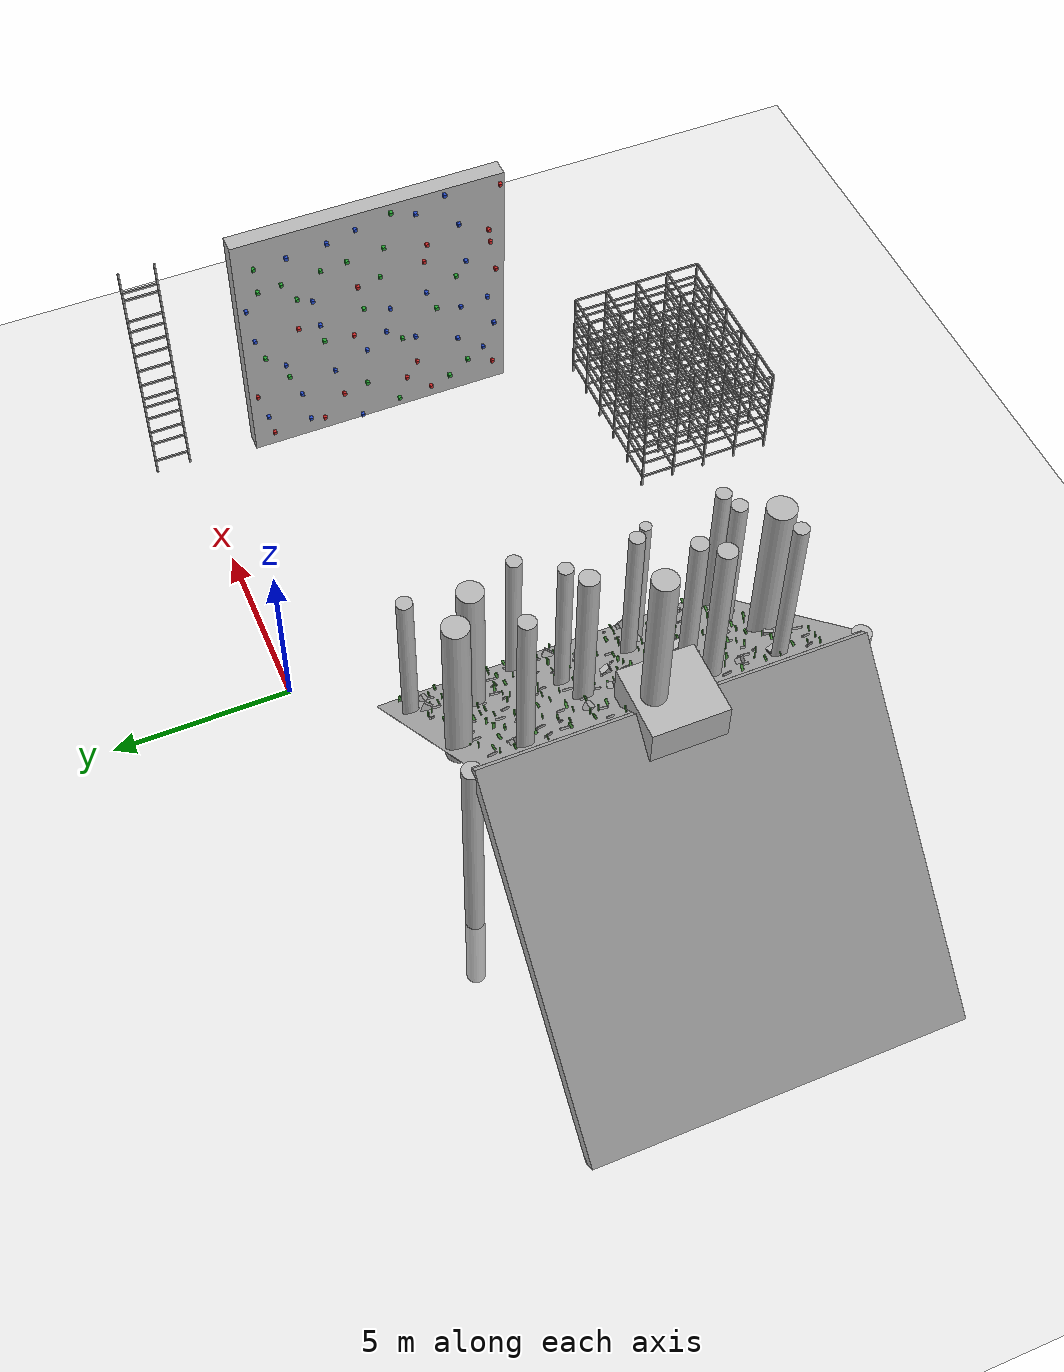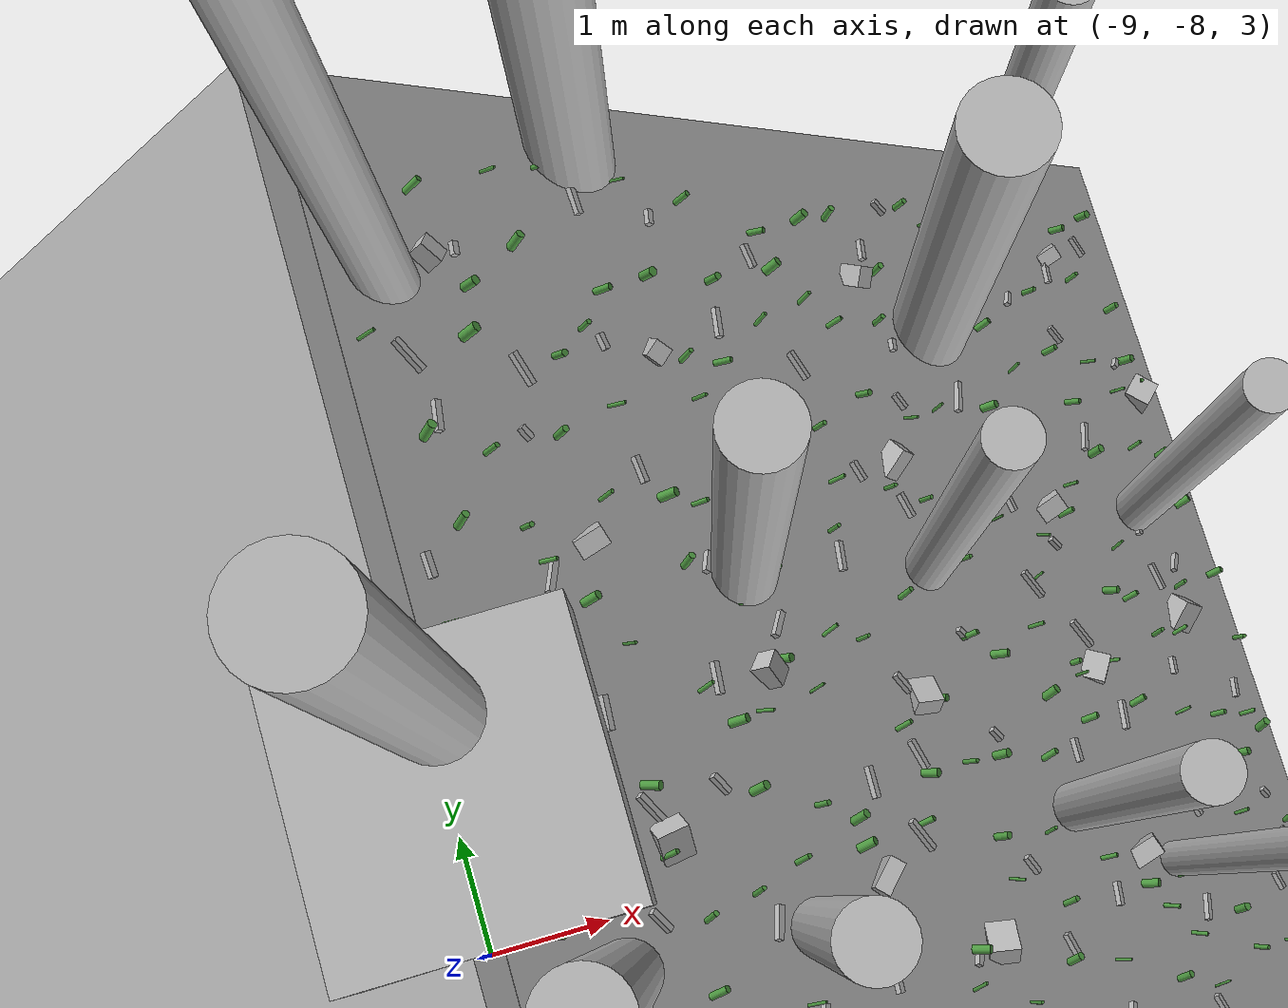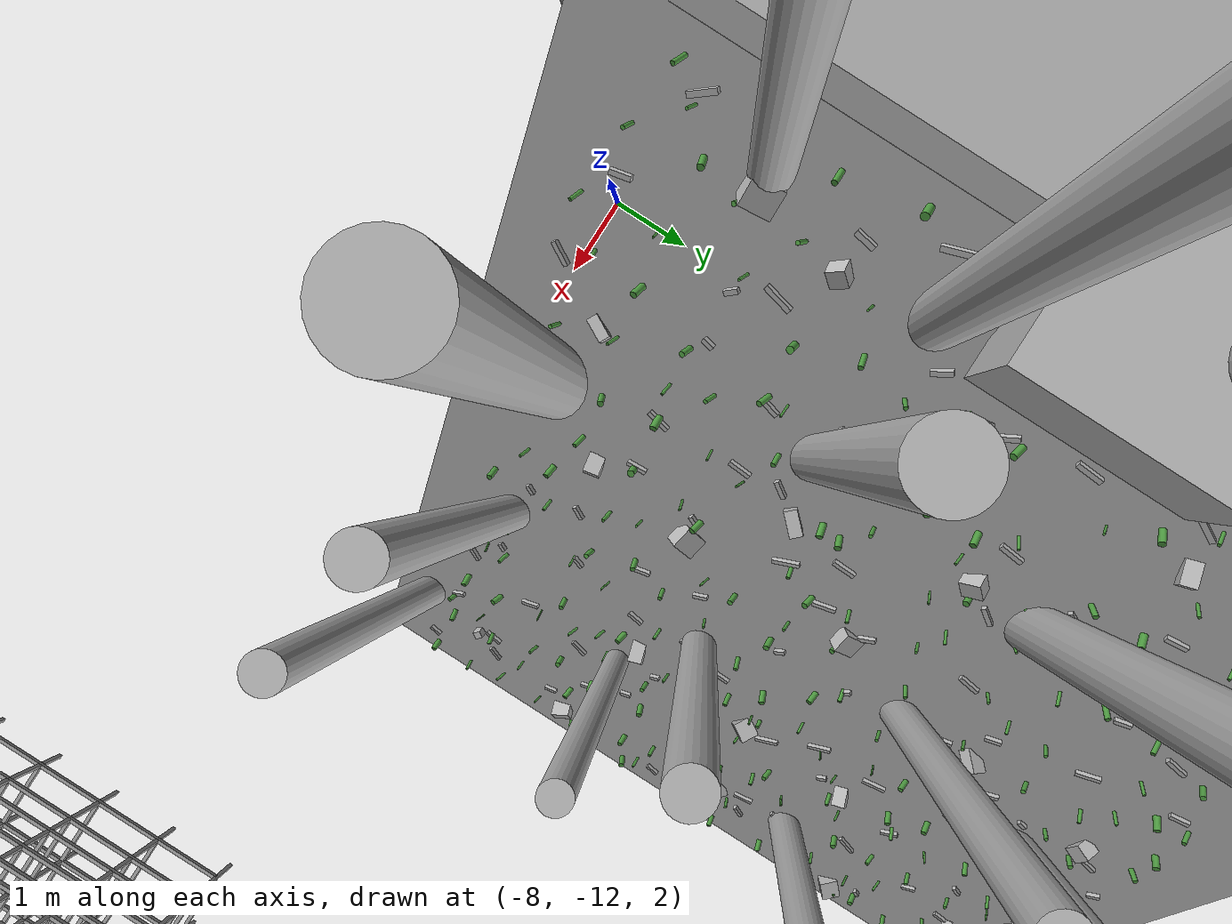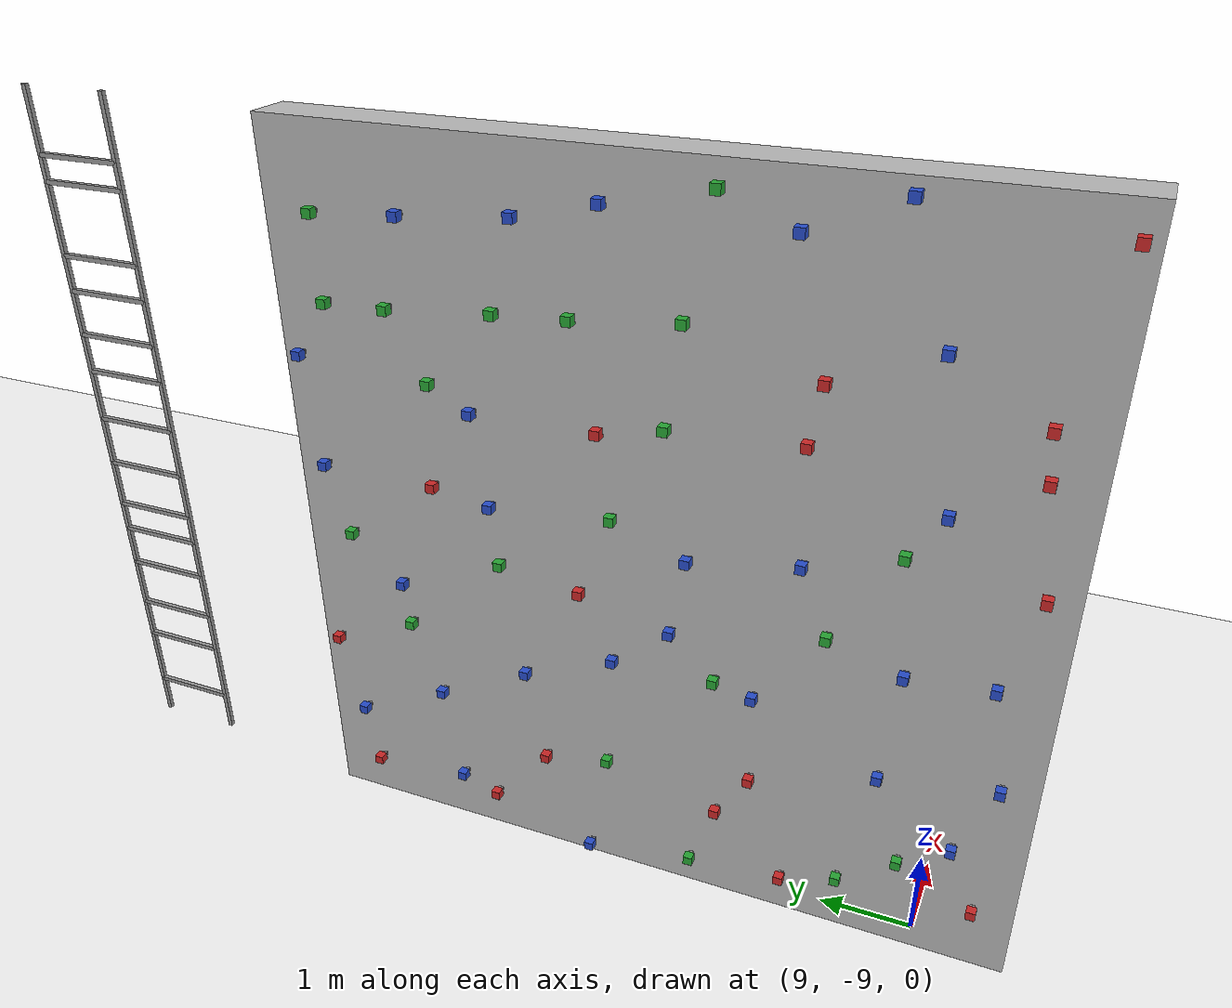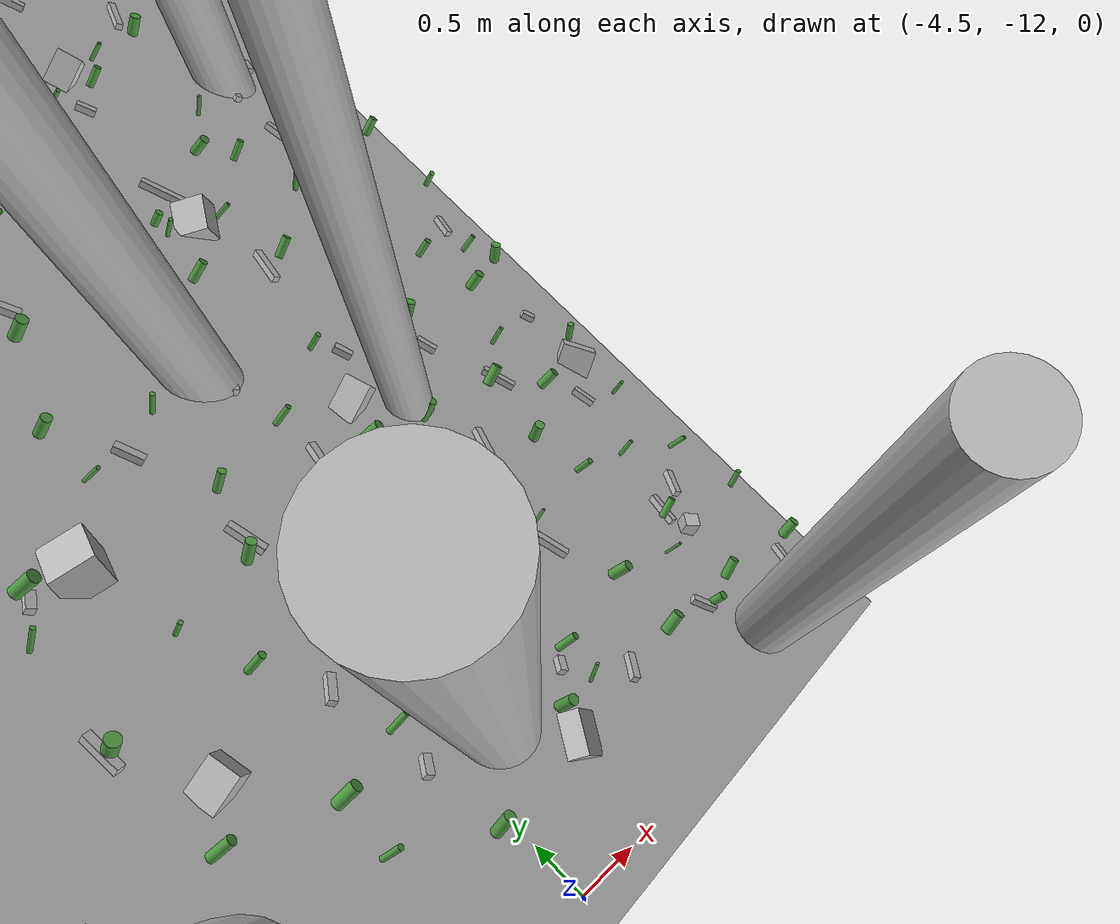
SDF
<sdf version="1.5">
 <world name="mysky">
  <scene>
   <ambient>0.75 0.75 0.75 1</ambient>
   <background>0.5 0.5 0.5 1</background>
   <sky><clouds><speed>10</speed></clouds></sky>
  </scene>
  <include><uri>model://sun</uri></include>
  <include><uri>model://ground_plane</uri></include>
  <light type="point" name="point">
   <pose>-5 5 5 0 0 0</pose>
   <diffuse>1 1 1 1</diffuse>
   <specular>.1 .1 .1 1</specular>
   <attenuation>
    <range>10</range>
    <linear>0.2</linear>
    <constant>0.8</constant>
    <quadratic>0.01</quadratic>
   </attenuation>
   <cast_shadows>false</cast_shadows>
  </light>
  <light type="spot" name="spot">
   <pose>5 5 25 0 0 0</pose>
   <diffuse>1 1 1 1</diffuse>
   <specular>.2 .2 .2 1</specular>
   <attenuation>
    <range>30</range>
    <linear>0.01</linear>
    <constant>0.2</constant>
    <quadratic>0.0</quadratic>
   </attenuation>
   <direction>0 0 -1</direction>
   <spot><inner_angle>0.1</inner_angle><outer_angle>0.5</outer_angle><falloff>1.2</falloff></spot>
   <cast_shadows>false</cast_shadows>
  </light>
  <include><uri>model://woodbox</uri><pose>-8.5 -7 6.5 0 0 0 0</pose></include>
  <include><uri>model://slope</uri><pose>-12 -7 -3.5 0 0.7854 0</pose></include>
  <include><uri>model://ladder</uri><pose>9 0 0 0 0 1.5708</pose></include>
  <include><uri>model://bldwall</uri><pose>9 -10 0 0 0 1.5708</pose></include>
  <include><uri>model://jgym</uri><pose>3 -16 0 0 0 0</pose></include>
 </world>
</sdf>

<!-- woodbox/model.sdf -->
<sdf version="1.5">
  <model name="woodbox">
    <static>true</static>
    <link name="link">

      <collision name="woodboxcollision">
        <pose>0 0 0.5 0 0 0</pose>
        <geometry> <box> <size>2 2 1</size> </box> </geometry>
        <surface>
          <friction> <ode> <mu>0.6</mu> <mu2>0.6</mu2> </ode> </friction>
        </surface>
      </collision>
      <visual name="woodboxvisual">
        <pose>0 0 0.5 0 0 0</pose>
        <geometry> <box> <size>2 2 1</size> </box> </geometry>
        <material>
          <script>
            <uri>file://media/materials/scripts/gazebo.material</uri>
            <name>Gazebo/Soil1</name>
          </script>
        </material>
      </visual>

    </link>
  </model>
</sdf>

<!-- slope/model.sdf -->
<sdf version="1.5">
  <model name="slope">
    <static>true</static>
    <link name="link">

      <collision name="slope1collision">
        <pose>0 0 10 0 0 0</pose>
        <geometry> <box> <size>10 10 0.005</size> </box> </geometry>
        <surface>
          <friction> <ode> <mu>0.6</mu> <mu2>0.6</mu2> </ode> </friction>
        </surface>
      </collision>

      <visual name="slope1visual">
        <pose>0 0 10 0 0 0</pose>
        <geometry> <box> <size>10 10 0.005</size> </box> </geometry>
        <material>
          <script>
            <uri>file://media/materials/scripts/gazebo.material</uri>
            <name>Gazebo/Soil1</name>
          </script>
        </material>
      </visual>

      <collision name="slope2collision">
        <pose>-5 0 5 0 0 0</pose>
        <geometry> <box> <size>0.5 10 10</size> </box> </geometry>
        <surface>
          <friction> <ode> <mu>0.6</mu> <mu2>0.6</mu2> </ode> </friction>
        </surface>
      </collision>

      <visual name="slope2visual">
        <pose>-5 0 5 0 0 0</pose>
        <geometry> <box> <size>0.5 10 10</size> </box> </geometry>
        <material>
          <script>
            <uri>file://media/materials/scripts/gazebo.material</uri>
            <name>Gazebo/Soil4</name>
          </script>
        </material>
      </visual>

      <collision name="pillar1collision">
        <pose>-1.414 -5 6.414 0 -0.7845 0</pose>
        <geometry> <cylinder> <radius>0.25</radius> <length>10</length> </cylinder> </geometry>
      </collision>

      <visual name="pillar1visual">
        <pose>-1.414 -5 6.414 0 -0.7845 0</pose>
        <geometry> <cylinder> <radius>0.25</radius> <length>10</length> </cylinder> </geometry>
        <material>
	  <script>
            <uri>file://media/materials/scripts/gazebo.material</uri>
            <name>Gazebo/Tree1</name>
          </script>
        </material>
      </visual>

      <collision name="pillar2collision">
        <pose>-1.414 5 6.414 0 -0.7845 0</pose>
        <geometry> <cylinder> <radius>0.25</radius> <length>10</length> </cylinder> </geometry>
      </collision>

      <visual name="pillar2visual">
        <pose>-1.414 5 6.414 0 -0.7845 0</pose>
        <geometry> <cylinder> <radius>0.25</radius> <length>10</length> </cylinder> </geometry>
        <material>
	  <script>
            <uri>file://media/materials/scripts/gazebo.material</uri>
            <name>Gazebo/Tree1</name>
          </script>
        </material>
      </visual>

<collision name="wood00collision">
<pose>-5.914750 -3.074500 11.56 0 -0.7845 0</pose>
<geometry> <cylinder> <radius>0.187500</radius> <length>5.000000</length> </cylinder> </geometry>
</collision>
<visual name="wood00visual">
<pose>-5.914750 -3.074500 11.56 0 -0.7845 0</pose>
<geometry> <cylinder> <radius>0.187500</radius> <length>5.000000</length> </cylinder> </geometry>
<material> <script> <uri>file://media/materials/scripts/gazebo.material</uri>
<name>Gazebo/Tree3</name> </script> </material>
</visual>

<collision name="wood01collision">
<pose>-2.697250 -4.038750 11.56 0 -0.7845 0</pose>
<geometry> <cylinder> <radius>0.380000</radius> <length>5.000000</length> </cylinder> </geometry>
</collision>
<visual name="wood01visual">
<pose>-2.697250 -4.038750 11.56 0 -0.7845 0</pose>
<geometry> <cylinder> <radius>0.380000</radius> <length>5.000000</length> </cylinder> </geometry>
<material> <script> <uri>file://media/materials/scripts/gazebo.material</uri>
<name>Gazebo/Tree4</name> </script> </material>
</visual>

<collision name="wood02collision">
<pose>-0.449250 -3.888250 11.56 0 -0.7845 0</pose>
<geometry> <cylinder> <radius>0.217500</radius> <length>5.000000</length> </cylinder> </geometry>
</collision>
<visual name="wood02visual">
<pose>-0.449250 -3.888250 11.56 0 -0.7845 0</pose>
<geometry> <cylinder> <radius>0.217500</radius> <length>5.000000</length> </cylinder> </geometry>
<material> <script> <uri>file://media/materials/scripts/gazebo.material</uri>
<name>Gazebo/Tree3</name> </script> </material>
</visual>

<collision name="wood03collision">
<pose>2.122500 -4.521750 11.56 0 -0.7845 0</pose>
<geometry> <cylinder> <radius>0.215000</radius> <length>5.000000</length> </cylinder> </geometry>
</collision>
<visual name="wood03visual">
<pose>2.122500 -4.521750 11.56 0 -0.7845 0</pose>
<geometry> <cylinder> <radius>0.215000</radius> <length>5.000000</length> </cylinder> </geometry>
<material> <script> <uri>file://media/materials/scripts/gazebo.material</uri>
<name>Gazebo/Tree7</name> </script> </material>
</visual>

<collision name="wood10collision">
<pose>-5.640000 -1.379500 11.56 0 -0.7845 0</pose>
<geometry> <cylinder> <radius>0.240000</radius> <length>5.000000</length> </cylinder> </geometry>
</collision>
<visual name="wood10visual">
<pose>-5.640000 -1.379500 11.56 0 -0.7845 0</pose>
<geometry> <cylinder> <radius>0.240000</radius> <length>5.000000</length> </cylinder> </geometry>
<material> <script> <uri>file://media/materials/scripts/gazebo.material</uri>
<name>Gazebo/Tree3</name> </script> </material>
</visual>

<collision name="wood11collision">
<pose>-3.715750 -1.481000 11.56 0 -0.7845 0</pose>
<geometry> <cylinder> <radius>0.222500</radius> <length>5.000000</length> </cylinder> </geometry>
</collision>
<visual name="wood11visual">
<pose>-3.715750 -1.481000 11.56 0 -0.7845 0</pose>
<geometry> <cylinder> <radius>0.222500</radius> <length>5.000000</length> </cylinder> </geometry>
<material> <script> <uri>file://media/materials/scripts/gazebo.material</uri>
<name>Gazebo/Tree6</name> </script> </material>
</visual>

<collision name="wood12collision">
<pose>-0.216500 -1.197500 11.56 0 -0.7845 0</pose>
<geometry> <cylinder> <radius>0.207500</radius> <length>5.000000</length> </cylinder> </geometry>
</collision>
<visual name="wood12visual">
<pose>-0.216500 -1.197500 11.56 0 -0.7845 0</pose>
<geometry> <cylinder> <radius>0.207500</radius> <length>5.000000</length> </cylinder> </geometry>
<material> <script> <uri>file://media/materials/scripts/gazebo.material</uri>
<name>Gazebo/Tree6</name> </script> </material>
</visual>

<collision name="wood13collision">
<pose>1.032250 -1.888750 11.56 0 -0.7845 0</pose>
<geometry> <cylinder> <radius>0.155000</radius> <length>5.000000</length> </cylinder> </geometry>
</collision>
<visual name="wood13visual">
<pose>1.032250 -1.888750 11.56 0 -0.7845 0</pose>
<geometry> <cylinder> <radius>0.155000</radius> <length>5.000000</length> </cylinder> </geometry>
<material> <script> <uri>file://media/materials/scripts/gazebo.material</uri>
<name>Gazebo/Tree6</name> </script> </material>
</visual>

<collision name="wood20collision">
<pose>-6.546500 0.476500 11.56 0 -0.7845 0</pose>
<geometry> <cylinder> <radius>0.317500</radius> <length>5.000000</length> </cylinder> </geometry>
</collision>
<visual name="wood20visual">
<pose>-6.546500 0.476500 11.56 0 -0.7845 0</pose>
<geometry> <cylinder> <radius>0.317500</radius> <length>5.000000</length> </cylinder> </geometry>
<material> <script> <uri>file://media/materials/scripts/gazebo.material</uri>
<name>Gazebo/Tree4</name> </script> </material>
</visual>

<collision name="wood21collision">
<pose>-3.397250 1.173000 11.56 0 -0.7845 0</pose>
<geometry> <cylinder> <radius>0.255000</radius> <length>5.000000</length> </cylinder> </geometry>
</collision>
<visual name="wood21visual">
<pose>-3.397250 1.173000 11.56 0 -0.7845 0</pose>
<geometry> <cylinder> <radius>0.255000</radius> <length>5.000000</length> </cylinder> </geometry>
<material> <script> <uri>file://media/materials/scripts/gazebo.material</uri>
<name>Gazebo/Tree3</name> </script> </material>
</visual>

<collision name="wood22collision">
<pose>-1.184250 1.027750 11.56 0 -0.7845 0</pose>
<geometry> <cylinder> <radius>0.197500</radius> <length>5.000000</length> </cylinder> </geometry>
</collision>
<visual name="wood22visual">
<pose>-1.184250 1.027750 11.56 0 -0.7845 0</pose>
<geometry> <cylinder> <radius>0.197500</radius> <length>5.000000</length> </cylinder> </geometry>
<material> <script> <uri>file://media/materials/scripts/gazebo.material</uri>
<name>Gazebo/Tree6</name> </script> </material>
</visual>

<collision name="wood23collision">
<pose>2.287000 1.314750 11.56 0 -0.7845 0</pose>
<geometry> <cylinder> <radius>0.210000</radius> <length>5.000000</length> </cylinder> </geometry>
</collision>
<visual name="wood23visual">
<pose>2.287000 1.314750 11.56 0 -0.7845 0</pose>
<geometry> <cylinder> <radius>0.210000</radius> <length>5.000000</length> </cylinder> </geometry>
<material> <script> <uri>file://media/materials/scripts/gazebo.material</uri>
<name>Gazebo/Tree7</name> </script> </material>
</visual>

<collision name="wood30collision">
<pose>-6.033750 3.522500 11.56 0 -0.7845 0</pose>
<geometry> <cylinder> <radius>0.215000</radius> <length>5.000000</length> </cylinder> </geometry>
</collision>
<visual name="wood30visual">
<pose>-6.033750 3.522500 11.56 0 -0.7845 0</pose>
<geometry> <cylinder> <radius>0.215000</radius> <length>5.000000</length> </cylinder> </geometry>
<material> <script> <uri>file://media/materials/scripts/gazebo.material</uri>
<name>Gazebo/Tree4</name> </script> </material>
</visual>

<collision name="wood31collision">
<pose>-3.925750 4.590000 11.56 0 -0.7845 0</pose>
<geometry> <cylinder> <radius>0.332500</radius> <length>5.000000</length> </cylinder> </geometry>
</collision>
<visual name="wood31visual">
<pose>-3.925750 4.590000 11.56 0 -0.7845 0</pose>
<geometry> <cylinder> <radius>0.332500</radius> <length>5.000000</length> </cylinder> </geometry>
<material> <script> <uri>file://media/materials/scripts/gazebo.material</uri>
<name>Gazebo/Tree2</name> </script> </material>
</visual>

<collision name="wood32collision">
<pose>-0.076500 3.172500 11.56 0 -0.7845 0</pose>
<geometry> <cylinder> <radius>0.352500</radius> <length>5.000000</length> </cylinder> </geometry>
</collision>
<visual name="wood32visual">
<pose>-0.076500 3.172500 11.56 0 -0.7845 0</pose>
<geometry> <cylinder> <radius>0.352500</radius> <length>5.000000</length> </cylinder> </geometry>
<material> <script> <uri>file://media/materials/scripts/gazebo.material</uri>
<name>Gazebo/Tree2</name> </script> </material>
</visual>

<collision name="wood33collision">
<pose>1.448750 4.493750 11.56 0 -0.7845 0</pose>
<geometry> <cylinder> <radius>0.217500</radius> <length>5.000000</length> </cylinder> </geometry>
</collision>
<visual name="wood33visual">
<pose>1.448750 4.493750 11.56 0 -0.7845 0</pose>
<geometry> <cylinder> <radius>0.217500</radius> <length>5.000000</length> </cylinder> </geometry>
<material> <script> <uri>file://media/materials/scripts/gazebo.material</uri>
<name>Gazebo/Tree5</name> </script> </material>
</visual>

<collision name="grass00collision">
<pose>-4.721267 -4.019866 10.075000 0.174045 0.260753 0</pose>
<geometry> <cylinder> <radius>0.020500</radius> <length>0.150000</length> </cylinder> </geometry>
</collision>
<visual name="grass00visual">
<pose>-4.721267 -4.019866 10.075000 0.174045 0.260753 0</pose>
<geometry> <cylinder> <radius>0.020500</radius> <length>0.150000</length> </cylinder> </geometry>
<material> <script> <uri>file://media/materials/scripts/gazebo.material</uri>
<name>Gazebo/Grass2</name> </script> </material>
</visual>

<collision name="grass01collision">
<pose>-4.053200 -4.203733 10.075000 0.093620 -0.049637 0</pose>
<geometry> <cylinder> <radius>0.018100</radius> <length>0.150000</length> </cylinder> </geometry>
</collision>
<visual name="grass01visual">
<pose>-4.053200 -4.203733 10.075000 0.093620 -0.049637 0</pose>
<geometry> <cylinder> <radius>0.018100</radius> <length>0.150000</length> </cylinder> </geometry>
<material> <script> <uri>file://media/materials/scripts/gazebo.material</uri>
<name>Gazebo/Grass2</name> </script> </material>
</visual>

<collision name="grass02collision">
<pose>-3.244667 -4.405800 10.075000 0.165248 0.267664 0</pose>
<geometry> <cylinder> <radius>0.017800</radius> <length>0.150000</length> </cylinder> </geometry>
</collision>
<visual name="grass02visual">
<pose>-3.244667 -4.405800 10.075000 0.165248 0.267664 0</pose>
<geometry> <cylinder> <radius>0.017800</radius> <length>0.150000</length> </cylinder> </geometry>
<material> <script> <uri>file://media/materials/scripts/gazebo.material</uri>
<name>Gazebo/Grass2</name> </script> </material>
</visual>

<collision name="grass03collision">
<pose>-2.819733 -4.089867 10.075000 -0.181584 -0.082938 0</pose>
<geometry> <cylinder> <radius>0.018700</radius> <length>0.150000</length> </cylinder> </geometry>
</collision>
<visual name="grass03visual">
<pose>-2.819733 -4.089867 10.075000 -0.181584 -0.082938 0</pose>
<geometry> <cylinder> <radius>0.018700</radius> <length>0.150000</length> </cylinder> </geometry>
<material> <script> <uri>file://media/materials/scripts/gazebo.material</uri>
<name>Gazebo/Grass2</name> </script> </material>
</visual>

<collision name="grass04collision">
<pose>-1.868400 -4.186000 10.075000 0.227452 -0.236877 0</pose>
<geometry> <cylinder> <radius>0.020500</radius> <length>0.150000</length> </cylinder> </geometry>
</collision>
<visual name="grass04visual">
<pose>-1.868400 -4.186000 10.075000 0.227452 -0.236877 0</pose>
<geometry> <cylinder> <radius>0.020500</radius> <length>0.150000</length> </cylinder> </geometry>
<material> <script> <uri>file://media/materials/scripts/gazebo.material</uri>
<name>Gazebo/Grass2</name> </script> </material>
</visual>

<collision name="grass05collision">
<pose>-1.133133 -4.059067 10.075000 -0.300337 -0.277717 0</pose>
<geometry> <cylinder> <radius>0.030100</radius> <length>0.150000</length> </cylinder> </geometry>
</collision>
<visual name="grass05visual">
<pose>-1.133133 -4.059067 10.075000 -0.300337 -0.277717 0</pose>
<geometry> <cylinder> <radius>0.030100</radius> <length>0.150000</length> </cylinder> </geometry>
<material> <script> <uri>file://media/materials/scripts/gazebo.material</uri>
<name>Gazebo/Grass2</name> </script> </material>
</visual>

<collision name="grass06collision">
<pose>-0.716600 -4.220533 10.075000 -0.307248 -0.287771 0</pose>
<geometry> <cylinder> <radius>0.031900</radius> <length>0.150000</length> </cylinder> </geometry>
</collision>
<visual name="grass06visual">
<pose>-0.716600 -4.220533 10.075000 -0.307248 -0.287771 0</pose>
<geometry> <cylinder> <radius>0.031900</radius> <length>0.150000</length> </cylinder> </geometry>
<material> <script> <uri>file://media/materials/scripts/gazebo.material</uri>
<name>Gazebo/Grass2</name> </script> </material>
</visual>

<collision name="grass07collision">
<pose>-0.036867 -4.004467 10.075000 0.178443 0.023248 0</pose>
<geometry> <cylinder> <radius>0.017200</radius> <length>0.150000</length> </cylinder> </geometry>
</collision>
<visual name="grass07visual">
<pose>-0.036867 -4.004467 10.075000 0.178443 0.023248 0</pose>
<geometry> <cylinder> <radius>0.017200</radius> <length>0.150000</length> </cylinder> </geometry>
<material> <script> <uri>file://media/materials/scripts/gazebo.material</uri>
<name>Gazebo/Grass2</name> </script> </material>
</visual>

<collision name="grass08collision">
<pose>0.580333 -4.260667 10.075000 -0.054664 0.016336 0</pose>
<geometry> <cylinder> <radius>0.034000</radius> <length>0.150000</length> </cylinder> </geometry>
</collision>
<visual name="grass08visual">
<pose>0.580333 -4.260667 10.075000 -0.054664 0.016336 0</pose>
<geometry> <cylinder> <radius>0.034000</radius> <length>0.150000</length> </cylinder> </geometry>
<material> <script> <uri>file://media/materials/scripts/gazebo.material</uri>
<name>Gazebo/Grass2</name> </script> </material>
</visual>

<collision name="grass09collision">
<pose>1.546133 -4.025933 10.075000 0.227452 -0.207346 0</pose>
<geometry> <cylinder> <radius>0.034300</radius> <length>0.150000</length> </cylinder> </geometry>
</collision>
<visual name="grass09visual">
<pose>1.546133 -4.025933 10.075000 0.227452 -0.207346 0</pose>
<geometry> <cylinder> <radius>0.034300</radius> <length>0.150000</length> </cylinder> </geometry>
<material> <script> <uri>file://media/materials/scripts/gazebo.material</uri>
<name>Gazebo/Grass2</name> </script> </material>
</visual>

<collision name="grass010collision">
<pose>1.909000 -4.001667 10.075000 -0.261381 -0.108699 0</pose>
<geometry> <cylinder> <radius>0.011500</radius> <length>0.150000</length> </cylinder> </geometry>
</collision>
<visual name="grass010visual">
<pose>1.909000 -4.001667 10.075000 -0.261381 -0.108699 0</pose>
<geometry> <cylinder> <radius>0.011500</radius> <length>0.150000</length> </cylinder> </geometry>
<material> <script> <uri>file://media/materials/scripts/gazebo.material</uri>
<name>Gazebo/Grass2</name> </script> </material>
</visual>

<collision name="grass011collision">
<pose>2.828133 -4.093133 10.075000 -0.117496 0.224310 0</pose>
<geometry> <cylinder> <radius>0.038500</radius> <length>0.150000</length> </cylinder> </geometry>
</collision>
<visual name="grass011visual">
<pose>2.828133 -4.093133 10.075000 -0.117496 0.224310 0</pose>
<geometry> <cylinder> <radius>0.038500</radius> <length>0.150000</length> </cylinder> </geometry>
<material> <script> <uri>file://media/materials/scripts/gazebo.material</uri>
<name>Gazebo/Grass2</name> </script> </material>
</visual>

<collision name="grass012collision">
<pose>3.371600 -4.179000 10.075000 0.197292 -0.083567 0</pose>
<geometry> <cylinder> <radius>0.029200</radius> <length>0.150000</length> </cylinder> </geometry>
</collision>
<visual name="grass012visual">
<pose>3.371600 -4.179000 10.075000 0.197292 -0.083567 0</pose>
<geometry> <cylinder> <radius>0.029200</radius> <length>0.150000</length> </cylinder> </geometry>
<material> <script> <uri>file://media/materials/scripts/gazebo.material</uri>
<name>Gazebo/Grass2</name> </script> </material>
</visual>

<collision name="grass013collision">
<pose>3.786733 -4.083333 10.075000 -0.259496 0.193523 0</pose>
<geometry> <cylinder> <radius>0.033400</radius> <length>0.150000</length> </cylinder> </geometry>
</collision>
<visual name="grass013visual">
<pose>3.786733 -4.083333 10.075000 -0.259496 0.193523 0</pose>
<geometry> <cylinder> <radius>0.033400</radius> <length>0.150000</length> </cylinder> </geometry>
<material> <script> <uri>file://media/materials/scripts/gazebo.material</uri>
<name>Gazebo/Grass2</name> </script> </material>
</visual>

<collision name="grass014collision">
<pose>4.801067 -4.160800 10.075000 -0.060947 0.094876 0</pose>
<geometry> <cylinder> <radius>0.039700</radius> <length>0.150000</length> </cylinder> </geometry>
</collision>
<visual name="grass014visual">
<pose>4.801067 -4.160800 10.075000 -0.060947 0.094876 0</pose>
<geometry> <cylinder> <radius>0.039700</radius> <length>0.150000</length> </cylinder> </geometry>
<material> <script> <uri>file://media/materials/scripts/gazebo.material</uri>
<name>Gazebo/Grass2</name> </script> </material>
</visual>

<collision name="grass10collision">
<pose>-4.465066 -3.805333 10.075000 0.110584 -0.082938 0</pose>
<geometry> <cylinder> <radius>0.013600</radius> <length>0.150000</length> </cylinder> </geometry>
</collision>
<visual name="grass10visual">
<pose>-4.465066 -3.805333 10.075000 0.110584 -0.082938 0</pose>
<geometry> <cylinder> <radius>0.013600</radius> <length>0.150000</length> </cylinder> </geometry>
<material> <script> <uri>file://media/materials/scripts/gazebo.material</uri>
<name>Gazebo/Grass2</name> </script> </material>
</visual>

<collision name="grass11collision">
<pose>-4.127867 -3.559867 10.075000 -0.255098 0.024504 0</pose>
<geometry> <cylinder> <radius>0.031000</radius> <length>0.150000</length> </cylinder> </geometry>
</collision>
<visual name="grass11visual">
<pose>-4.127867 -3.559867 10.075000 -0.255098 0.024504 0</pose>
<geometry> <cylinder> <radius>0.031000</radius> <length>0.150000</length> </cylinder> </geometry>
<material> <script> <uri>file://media/materials/scripts/gazebo.material</uri>
<name>Gazebo/Grass2</name> </script> </material>
</visual>

<collision name="grass12collision">
<pose>-3.364133 -3.656933 10.075000 -0.020735 0.063460 0</pose>
<geometry> <cylinder> <radius>0.010600</radius> <length>0.150000</length> </cylinder> </geometry>
</collision>
<visual name="grass12visual">
<pose>-3.364133 -3.656933 10.075000 -0.020735 0.063460 0</pose>
<geometry> <cylinder> <radius>0.010600</radius> <length>0.150000</length> </cylinder> </geometry>
<material> <script> <uri>file://media/materials/scripts/gazebo.material</uri>
<name>Gazebo/Grass2</name> </script> </material>
</visual>

<collision name="grass13collision">
<pose>-2.752067 -3.603733 10.075000 0.095505 0.160850 0</pose>
<geometry> <cylinder> <radius>0.034000</radius> <length>0.150000</length> </cylinder> </geometry>
</collision>
<visual name="grass13visual">
<pose>-2.752067 -3.603733 10.075000 0.095505 0.160850 0</pose>
<geometry> <cylinder> <radius>0.034000</radius> <length>0.150000</length> </cylinder> </geometry>
<material> <script> <uri>file://media/materials/scripts/gazebo.material</uri>
<name>Gazebo/Grass2</name> </script> </material>
</visual>

<collision name="grass14collision">
<pose>-2.099867 -3.627533 10.075000 0.229337 0.118752 0</pose>
<geometry> <cylinder> <radius>0.015700</radius> <length>0.150000</length> </cylinder> </geometry>
</collision>
<visual name="grass14visual">
<pose>-2.099867 -3.627533 10.075000 0.229337 0.118752 0</pose>
<geometry> <cylinder> <radius>0.015700</radius> <length>0.150000</length> </cylinder> </geometry>
<material> <script> <uri>file://media/materials/scripts/gazebo.material</uri>
<name>Gazebo/Grass2</name> </script> </material>
</visual>

<collision name="grass15collision">
<pose>-1.361333 -3.493133 10.075000 -0.294682 -0.240647 0</pose>
<geometry> <cylinder> <radius>0.031300</radius> <length>0.150000</length> </cylinder> </geometry>
</collision>
<visual name="grass15visual">
<pose>-1.361333 -3.493133 10.075000 -0.294682 -0.240647 0</pose>
<geometry> <cylinder> <radius>0.031300</radius> <length>0.150000</length> </cylinder> </geometry>
<material> <script> <uri>file://media/materials/scripts/gazebo.material</uri>
<name>Gazebo/Grass2</name> </script> </material>
</visual>

<collision name="grass16collision">
<pose>-0.675533 -3.518333 10.075000 0.131319 0.268293 0</pose>
<geometry> <cylinder> <radius>0.026800</radius> <length>0.150000</length> </cylinder> </geometry>
</collision>
<visual name="grass16visual">
<pose>-0.675533 -3.518333 10.075000 0.131319 0.268293 0</pose>
<geometry> <cylinder> <radius>0.026800</radius> <length>0.150000</length> </cylinder> </geometry>
<material> <script> <uri>file://media/materials/scripts/gazebo.material</uri>
<name>Gazebo/Grass2</name> </script> </material>
</visual>

<collision name="grass17collision">
<pose>-0.001400 -3.668600 10.075000 0.054036 0.292169 0</pose>
<geometry> <cylinder> <radius>0.034900</radius> <length>0.150000</length> </cylinder> </geometry>
</collision>
<visual name="grass17visual">
<pose>-0.001400 -3.668600 10.075000 0.054036 0.292169 0</pose>
<geometry> <cylinder> <radius>0.034900</radius> <length>0.150000</length> </cylinder> </geometry>
<material> <script> <uri>file://media/materials/scripts/gazebo.material</uri>
<name>Gazebo/Grass2</name> </script> </material>
</visual>

<collision name="grass18collision">
<pose>0.535533 -3.542133 10.075000 0.017593 0.233107 0</pose>
<geometry> <cylinder> <radius>0.018700</radius> <length>0.150000</length> </cylinder> </geometry>
</collision>
<visual name="grass18visual">
<pose>0.535533 -3.542133 10.075000 0.017593 0.233107 0</pose>
<geometry> <cylinder> <radius>0.018700</radius> <length>0.150000</length> </cylinder> </geometry>
<material> <script> <uri>file://media/materials/scripts/gazebo.material</uri>
<name>Gazebo/Grass2</name> </script> </material>
</visual>

<collision name="grass19collision">
<pose>1.334733 -3.824467 10.075000 -0.144514 -0.082938 0</pose>
<geometry> <cylinder> <radius>0.014500</radius> <length>0.150000</length> </cylinder> </geometry>
</collision>
<visual name="grass19visual">
<pose>1.334733 -3.824467 10.075000 -0.144514 -0.082938 0</pose>
<geometry> <cylinder> <radius>0.014500</radius> <length>0.150000</length> </cylinder> </geometry>
<material> <script> <uri>file://media/materials/scripts/gazebo.material</uri>
<name>Gazebo/Grass2</name> </script> </material>
</visual>

<collision name="grass110collision">
<pose>1.925333 -3.763800 10.075000 0.185983 0.140115 0</pose>
<geometry> <cylinder> <radius>0.023500</radius> <length>0.150000</length> </cylinder> </geometry>
</collision>
<visual name="grass110visual">
<pose>1.925333 -3.763800 10.075000 0.185983 0.140115 0</pose>
<geometry> <cylinder> <radius>0.023500</radius> <length>0.150000</length> </cylinder> </geometry>
<material> <script> <uri>file://media/materials/scripts/gazebo.material</uri>
<name>Gazebo/Grass2</name> </script> </material>
</visual>

<collision name="grass111collision">
<pose>2.828133 -3.622867 10.075000 0.264523 0.034558 0</pose>
<geometry> <cylinder> <radius>0.036400</radius> <length>0.150000</length> </cylinder> </geometry>
</collision>
<visual name="grass111visual">
<pose>2.828133 -3.622867 10.075000 0.264523 0.034558 0</pose>
<geometry> <cylinder> <radius>0.036400</radius> <length>0.150000</length> </cylinder> </geometry>
<material> <script> <uri>file://media/materials/scripts/gazebo.material</uri>
<name>Gazebo/Grass2</name> </script> </material>
</visual>

<collision name="grass112collision">
<pose>3.456533 -3.726933 10.075000 0.214257 -0.094248 0</pose>
<geometry> <cylinder> <radius>0.010000</radius> <length>0.150000</length> </cylinder> </geometry>
</collision>
<visual name="grass112visual">
<pose>3.456533 -3.726933 10.075000 0.214257 -0.094248 0</pose>
<geometry> <cylinder> <radius>0.010000</radius> <length>0.150000</length> </cylinder> </geometry>
<material> <script> <uri>file://media/materials/scripts/gazebo.material</uri>
<name>Gazebo/Grass2</name> </script> </material>
</visual>

<collision name="grass113collision">
<pose>3.782533 -3.476800 10.075000 -0.236248 0.260124 0</pose>
<geometry> <cylinder> <radius>0.026800</radius> <length>0.150000</length> </cylinder> </geometry>
</collision>
<visual name="grass113visual">
<pose>3.782533 -3.476800 10.075000 -0.236248 0.260124 0</pose>
<geometry> <cylinder> <radius>0.026800</radius> <length>0.150000</length> </cylinder> </geometry>
<material> <script> <uri>file://media/materials/scripts/gazebo.material</uri>
<name>Gazebo/Grass2</name> </script> </material>
</visual>

<collision name="grass114collision">
<pose>4.780066 -3.604200 10.075000 -0.171531 -0.084823 0</pose>
<geometry> <cylinder> <radius>0.020800</radius> <length>0.150000</length> </cylinder> </geometry>
</collision>
<visual name="grass114visual">
<pose>4.780066 -3.604200 10.075000 -0.171531 -0.084823 0</pose>
<geometry> <cylinder> <radius>0.020800</radius> <length>0.150000</length> </cylinder> </geometry>
<material> <script> <uri>file://media/materials/scripts/gazebo.material</uri>
<name>Gazebo/Grass2</name> </script> </material>
</visual>

<collision name="grass20collision">
<pose>-4.698400 -2.976200 10.075000 -0.039584 -0.170903 0</pose>
<geometry> <cylinder> <radius>0.012100</radius> <length>0.150000</length> </cylinder> </geometry>
</collision>
<visual name="grass20visual">
<pose>-4.698400 -2.976200 10.075000 -0.039584 -0.170903 0</pose>
<geometry> <cylinder> <radius>0.012100</radius> <length>0.150000</length> </cylinder> </geometry>
<material> <script> <uri>file://media/materials/scripts/gazebo.material</uri>
<name>Gazebo/Grass2</name> </script> </material>
</visual>

<collision name="grass21collision">
<pose>-4.012133 -3.176867 10.075000 0.224939 -0.065974 0</pose>
<geometry> <cylinder> <radius>0.021100</radius> <length>0.150000</length> </cylinder> </geometry>
</collision>
<visual name="grass21visual">
<pose>-4.012133 -3.176867 10.075000 0.224939 -0.065974 0</pose>
<geometry> <cylinder> <radius>0.021100</radius> <length>0.150000</length> </cylinder> </geometry>
<material> <script> <uri>file://media/materials/scripts/gazebo.material</uri>
<name>Gazebo/Grass2</name> </script> </material>
</visual>

<collision name="grass22collision">
<pose>-3.457000 -2.863267 10.075000 0.199806 -0.045239 0</pose>
<geometry> <cylinder> <radius>0.013300</radius> <length>0.150000</length> </cylinder> </geometry>
</collision>
<visual name="grass22visual">
<pose>-3.457000 -2.863267 10.075000 0.199806 -0.045239 0</pose>
<geometry> <cylinder> <radius>0.013300</radius> <length>0.150000</length> </cylinder> </geometry>
<material> <script> <uri>file://media/materials/scripts/gazebo.material</uri>
<name>Gazebo/Grass2</name> </script> </material>
</visual>

<collision name="grass23collision">
<pose>-2.466933 -2.986467 10.075000 0.173416 -0.060319 0</pose>
<geometry> <cylinder> <radius>0.028900</radius> <length>0.150000</length> </cylinder> </geometry>
</collision>
<visual name="grass23visual">
<pose>-2.466933 -2.986467 10.075000 0.173416 -0.060319 0</pose>
<geometry> <cylinder> <radius>0.028900</radius> <length>0.150000</length> </cylinder> </geometry>
<material> <script> <uri>file://media/materials/scripts/gazebo.material</uri>
<name>Gazebo/Grass2</name> </script> </material>
</visual>

<collision name="grass24collision">
<pose>-1.947267 -2.982267 10.075000 0.066602 0.213629 0</pose>
<geometry> <cylinder> <radius>0.015400</radius> <length>0.150000</length> </cylinder> </geometry>
</collision>
<visual name="grass24visual">
<pose>-1.947267 -2.982267 10.075000 0.066602 0.213629 0</pose>
<geometry> <cylinder> <radius>0.015400</radius> <length>0.150000</length> </cylinder> </geometry>
<material> <script> <uri>file://media/materials/scripts/gazebo.material</uri>
<name>Gazebo/Grass2</name> </script> </material>
</visual>

<collision name="grass25collision">
<pose>-1.506933 -2.912267 10.075000 -0.082310 0.262009 0</pose>
<geometry> <cylinder> <radius>0.038800</radius> <length>0.150000</length> </cylinder> </geometry>
</collision>
<visual name="grass25visual">
<pose>-1.506933 -2.912267 10.075000 -0.082310 0.262009 0</pose>
<geometry> <cylinder> <radius>0.038800</radius> <length>0.150000</length> </cylinder> </geometry>
<material> <script> <uri>file://media/materials/scripts/gazebo.material</uri>
<name>Gazebo/Grass2</name> </script> </material>
</visual>

<collision name="grass26collision">
<pose>-0.748800 -2.886600 10.075000 -0.018850 -0.199177 0</pose>
<geometry> <cylinder> <radius>0.039700</radius> <length>0.150000</length> </cylinder> </geometry>
</collision>
<visual name="grass26visual">
<pose>-0.748800 -2.886600 10.075000 -0.018850 -0.199177 0</pose>
<geometry> <cylinder> <radius>0.039700</radius> <length>0.150000</length> </cylinder> </geometry>
<material> <script> <uri>file://media/materials/scripts/gazebo.material</uri>
<name>Gazebo/Grass2</name> </script> </material>
</visual>

<collision name="grass27collision">
<pose>0.126933 -2.895000 10.075000 0.090478 0.056549 0</pose>
<geometry> <cylinder> <radius>0.021700</radius> <length>0.150000</length> </cylinder> </geometry>
</collision>
<visual name="grass27visual">
<pose>0.126933 -2.895000 10.075000 0.090478 0.056549 0</pose>
<geometry> <cylinder> <radius>0.021700</radius> <length>0.150000</length> </cylinder> </geometry>
<material> <script> <uri>file://media/materials/scripts/gazebo.material</uri>
<name>Gazebo/Grass2</name> </script> </material>
</visual>

<collision name="grass28collision">
<pose>0.878533 -2.866533 10.075000 0.106186 -0.262638 0</pose>
<geometry> <cylinder> <radius>0.029200</radius> <length>0.150000</length> </cylinder> </geometry>
</collision>
<visual name="grass28visual">
<pose>0.878533 -2.866533 10.075000 0.106186 -0.262638 0</pose>
<geometry> <cylinder> <radius>0.029200</radius> <length>0.150000</length> </cylinder> </geometry>
<material> <script> <uri>file://media/materials/scripts/gazebo.material</uri>
<name>Gazebo/Grass2</name> </script> </material>
</visual>

<collision name="grass29collision">
<pose>1.191933 -2.996733 10.075000 -0.091106 0.191009 0</pose>
<geometry> <cylinder> <radius>0.013300</radius> <length>0.150000</length> </cylinder> </geometry>
</collision>
<visual name="grass29visual">
<pose>1.191933 -2.996733 10.075000 -0.091106 0.191009 0</pose>
<geometry> <cylinder> <radius>0.013300</radius> <length>0.150000</length> </cylinder> </geometry>
<material> <script> <uri>file://media/materials/scripts/gazebo.material</uri>
<name>Gazebo/Grass2</name> </script> </material>
</visual>

<collision name="grass210collision">
<pose>2.056933 -2.846933 10.075000 -0.126292 -0.098646 0</pose>
<geometry> <cylinder> <radius>0.030400</radius> <length>0.150000</length> </cylinder> </geometry>
</collision>
<visual name="grass210visual">
<pose>2.056933 -2.846933 10.075000 -0.126292 -0.098646 0</pose>
<geometry> <cylinder> <radius>0.030400</radius> <length>0.150000</length> </cylinder> </geometry>
<material> <script> <uri>file://media/materials/scripts/gazebo.material</uri>
<name>Gazebo/Grass2</name> </script> </material>
</visual>

<collision name="grass211collision">
<pose>2.592000 -3.036400 10.075000 -0.118752 0.194779 0</pose>
<geometry> <cylinder> <radius>0.010300</radius> <length>0.150000</length> </cylinder> </geometry>
</collision>
<visual name="grass211visual">
<pose>2.592000 -3.036400 10.075000 -0.118752 0.194779 0</pose>
<geometry> <cylinder> <radius>0.010300</radius> <length>0.150000</length> </cylinder> </geometry>
<material> <script> <uri>file://media/materials/scripts/gazebo.material</uri>
<name>Gazebo/Grass2</name> </script> </material>
</visual>

<collision name="grass212collision">
<pose>3.408467 -2.892667 10.075000 0.237505 -0.122522 0</pose>
<geometry> <cylinder> <radius>0.020800</radius> <length>0.150000</length> </cylinder> </geometry>
</collision>
<visual name="grass212visual">
<pose>3.408467 -2.892667 10.075000 0.237505 -0.122522 0</pose>
<geometry> <cylinder> <radius>0.020800</radius> <length>0.150000</length> </cylinder> </geometry>
<material> <script> <uri>file://media/materials/scripts/gazebo.material</uri>
<name>Gazebo/Grass2</name> </script> </material>
</visual>

<collision name="grass213collision">
<pose>3.973867 -2.941200 10.075000 0.013823 -0.021991 0</pose>
<geometry> <cylinder> <radius>0.014800</radius> <length>0.150000</length> </cylinder> </geometry>
</collision>
<visual name="grass213visual">
<pose>3.973867 -2.941200 10.075000 0.013823 -0.021991 0</pose>
<geometry> <cylinder> <radius>0.014800</radius> <length>0.150000</length> </cylinder> </geometry>
<material> <script> <uri>file://media/materials/scripts/gazebo.material</uri>
<name>Gazebo/Grass2</name> </script> </material>
</visual>

<collision name="grass214collision">
<pose>4.564933 -3.112933 10.075000 0.266408 0.086080 0</pose>
<geometry> <cylinder> <radius>0.017200</radius> <length>0.150000</length> </cylinder> </geometry>
</collision>
<visual name="grass214visual">
<pose>4.564933 -3.112933 10.075000 0.266408 0.086080 0</pose>
<geometry> <cylinder> <radius>0.017200</radius> <length>0.150000</length> </cylinder> </geometry>
<material> <script> <uri>file://media/materials/scripts/gazebo.material</uri>
<name>Gazebo/Grass2</name> </script> </material>
</visual>

<collision name="grass30collision">
<pose>-4.620000 -2.616533 10.075000 -0.030159 0.250700 0</pose>
<geometry> <cylinder> <radius>0.025000</radius> <length>0.150000</length> </cylinder> </geometry>
</collision>
<visual name="grass30visual">
<pose>-4.620000 -2.616533 10.075000 -0.030159 0.250700 0</pose>
<geometry> <cylinder> <radius>0.025000</radius> <length>0.150000</length> </cylinder> </geometry>
<material> <script> <uri>file://media/materials/scripts/gazebo.material</uri>
<name>Gazebo/Grass2</name> </script> </material>
</visual>

<collision name="grass31collision">
<pose>-4.014933 -2.600200 10.075000 0.297195 -0.231850 0</pose>
<geometry> <cylinder> <radius>0.019000</radius> <length>0.150000</length> </cylinder> </geometry>
</collision>
<visual name="grass31visual">
<pose>-4.014933 -2.600200 10.075000 0.297195 -0.231850 0</pose>
<geometry> <cylinder> <radius>0.019000</radius> <length>0.150000</length> </cylinder> </geometry>
<material> <script> <uri>file://media/materials/scripts/gazebo.material</uri>
<name>Gazebo/Grass2</name> </script> </material>
</visual>

<collision name="grass32collision">
<pose>-3.131267 -2.216133 10.075000 0.100531 -0.211744 0</pose>
<geometry> <cylinder> <radius>0.034300</radius> <length>0.150000</length> </cylinder> </geometry>
</collision>
<visual name="grass32visual">
<pose>-3.131267 -2.216133 10.075000 0.100531 -0.211744 0</pose>
<geometry> <cylinder> <radius>0.034300</radius> <length>0.150000</length> </cylinder> </geometry>
<material> <script> <uri>file://media/materials/scripts/gazebo.material</uri>
<name>Gazebo/Grass2</name> </script> </material>
</visual>

<collision name="grass33collision">
<pose>-2.480467 -2.168533 10.075000 0.288399 0.171531 0</pose>
<geometry> <cylinder> <radius>0.030400</radius> <length>0.150000</length> </cylinder> </geometry>
</collision>
<visual name="grass33visual">
<pose>-2.480467 -2.168533 10.075000 0.288399 0.171531 0</pose>
<geometry> <cylinder> <radius>0.030400</radius> <length>0.150000</length> </cylinder> </geometry>
<material> <script> <uri>file://media/materials/scripts/gazebo.material</uri>
<name>Gazebo/Grass2</name> </script> </material>
</visual>

<collision name="grass34collision">
<pose>-2.144667 -2.589000 10.075000 0.267664 -0.021363 0</pose>
<geometry> <cylinder> <radius>0.022000</radius> <length>0.150000</length> </cylinder> </geometry>
</collision>
<visual name="grass34visual">
<pose>-2.144667 -2.589000 10.075000 0.267664 -0.021363 0</pose>
<geometry> <cylinder> <radius>0.022000</radius> <length>0.150000</length> </cylinder> </geometry>
<material> <script> <uri>file://media/materials/scripts/gazebo.material</uri>
<name>Gazebo/Grass2</name> </script> </material>
</visual>

<collision name="grass35collision">
<pose>-1.524667 -2.314133 10.075000 -0.077912 0.026389 0</pose>
<geometry> <cylinder> <radius>0.012100</radius> <length>0.150000</length> </cylinder> </geometry>
</collision>
<visual name="grass35visual">
<pose>-1.524667 -2.314133 10.075000 -0.077912 0.026389 0</pose>
<geometry> <cylinder> <radius>0.012100</radius> <length>0.150000</length> </cylinder> </geometry>
<material> <script> <uri>file://media/materials/scripts/gazebo.material</uri>
<name>Gazebo/Grass2</name> </script> </material>
</visual>

<collision name="grass36collision">
<pose>-0.692333 -2.280533 10.075000 -0.201691 -0.051522 0</pose>
<geometry> <cylinder> <radius>0.013600</radius> <length>0.150000</length> </cylinder> </geometry>
</collision>
<visual name="grass36visual">
<pose>-0.692333 -2.280533 10.075000 -0.201691 -0.051522 0</pose>
<geometry> <cylinder> <radius>0.013600</radius> <length>0.150000</length> </cylinder> </geometry>
<material> <script> <uri>file://media/materials/scripts/gazebo.material</uri>
<name>Gazebo/Grass2</name> </script> </material>
</visual>

<collision name="grass37collision">
<pose>-0.070933 -2.553067 10.075000 0.099903 -0.308505 0</pose>
<geometry> <cylinder> <radius>0.013000</radius> <length>0.150000</length> </cylinder> </geometry>
</collision>
<visual name="grass37visual">
<pose>-0.070933 -2.553067 10.075000 0.099903 -0.308505 0</pose>
<geometry> <cylinder> <radius>0.013000</radius> <length>0.150000</length> </cylinder> </geometry>
<material> <script> <uri>file://media/materials/scripts/gazebo.material</uri>
<name>Gazebo/Grass2</name> </script> </material>
</visual>

<collision name="grass38collision">
<pose>0.592933 -2.359400 10.075000 -0.184726 -0.125036 0</pose>
<geometry> <cylinder> <radius>0.031600</radius> <length>0.150000</length> </cylinder> </geometry>
</collision>
<visual name="grass38visual">
<pose>0.592933 -2.359400 10.075000 -0.184726 -0.125036 0</pose>
<geometry> <cylinder> <radius>0.031600</radius> <length>0.150000</length> </cylinder> </geometry>
<material> <script> <uri>file://media/materials/scripts/gazebo.material</uri>
<name>Gazebo/Grass2</name> </script> </material>
</visual>

<collision name="grass39collision">
<pose>1.249800 -2.514333 10.075000 0.200434 0.062204 0</pose>
<geometry> <cylinder> <radius>0.011200</radius> <length>0.150000</length> </cylinder> </geometry>
</collision>
<visual name="grass39visual">
<pose>1.249800 -2.514333 10.075000 0.200434 0.062204 0</pose>
<geometry> <cylinder> <radius>0.011200</radius> <length>0.150000</length> </cylinder> </geometry>
<material> <script> <uri>file://media/materials/scripts/gazebo.material</uri>
<name>Gazebo/Grass2</name> </script> </material>
</visual>

<collision name="grass310collision">
<pose>2.204867 -2.254867 10.075000 0.276461 0.104929 0</pose>
<geometry> <cylinder> <radius>0.018400</radius> <length>0.150000</length> </cylinder> </geometry>
</collision>
<visual name="grass310visual">
<pose>2.204867 -2.254867 10.075000 0.276461 0.104929 0</pose>
<geometry> <cylinder> <radius>0.018400</radius> <length>0.150000</length> </cylinder> </geometry>
<material> <script> <uri>file://media/materials/scripts/gazebo.material</uri>
<name>Gazebo/Grass2</name> </script> </material>
</visual>

<collision name="grass311collision">
<pose>2.492600 -2.563333 10.075000 0.304107 0.099275 0</pose>
<geometry> <cylinder> <radius>0.017200</radius> <length>0.150000</length> </cylinder> </geometry>
</collision>
<visual name="grass311visual">
<pose>2.492600 -2.563333 10.075000 0.304107 0.099275 0</pose>
<geometry> <cylinder> <radius>0.017200</radius> <length>0.150000</length> </cylinder> </geometry>
<material> <script> <uri>file://media/materials/scripts/gazebo.material</uri>
<name>Gazebo/Grass2</name> </script> </material>
</visual>

<collision name="grass312collision">
<pose>3.296933 -2.507800 10.075000 -0.065345 -0.263266 0</pose>
<geometry> <cylinder> <radius>0.035200</radius> <length>0.150000</length> </cylinder> </geometry>
</collision>
<visual name="grass312visual">
<pose>3.296933 -2.507800 10.075000 -0.065345 -0.263266 0</pose>
<geometry> <cylinder> <radius>0.035200</radius> <length>0.150000</length> </cylinder> </geometry>
<material> <script> <uri>file://media/materials/scripts/gazebo.material</uri>
<name>Gazebo/Grass2</name> </script> </material>
</visual>

<collision name="grass313collision">
<pose>3.902933 -2.179733 10.075000 0.108071 0.219912 0</pose>
<geometry> <cylinder> <radius>0.035500</radius> <length>0.150000</length> </cylinder> </geometry>
</collision>
<visual name="grass313visual">
<pose>3.902933 -2.179733 10.075000 0.108071 0.219912 0</pose>
<geometry> <cylinder> <radius>0.035500</radius> <length>0.150000</length> </cylinder> </geometry>
<material> <script> <uri>file://media/materials/scripts/gazebo.material</uri>
<name>Gazebo/Grass2</name> </script> </material>
</visual>

<collision name="grass314collision">
<pose>4.536933 -2.493800 10.075000 0.087965 -0.287771 0</pose>
<geometry> <cylinder> <radius>0.013900</radius> <length>0.150000</length> </cylinder> </geometry>
</collision>
<visual name="grass314visual">
<pose>4.536933 -2.493800 10.075000 0.087965 -0.287771 0</pose>
<geometry> <cylinder> <radius>0.013900</radius> <length>0.150000</length> </cylinder> </geometry>
<material> <script> <uri>file://media/materials/scripts/gazebo.material</uri>
<name>Gazebo/Grass2</name> </script> </material>
</visual>

<collision name="grass40collision">
<pose>-4.760933 -1.944667 10.075000 0.015080 0.056549 0</pose>
<geometry> <cylinder> <radius>0.034300</radius> <length>0.150000</length> </cylinder> </geometry>
</collision>
<visual name="grass40visual">
<pose>-4.760933 -1.944667 10.075000 0.015080 0.056549 0</pose>
<geometry> <cylinder> <radius>0.034300</radius> <length>0.150000</length> </cylinder> </geometry>
<material> <script> <uri>file://media/materials/scripts/gazebo.material</uri>
<name>Gazebo/Grass2</name> </script> </material>
</visual>

<collision name="grass41collision">
<pose>-3.851133 -1.876533 10.075000 0.145770 -0.216770 0</pose>
<geometry> <cylinder> <radius>0.011200</radius> <length>0.150000</length> </cylinder> </geometry>
</collision>
<visual name="grass41visual">
<pose>-3.851133 -1.876533 10.075000 0.145770 -0.216770 0</pose>
<geometry> <cylinder> <radius>0.011200</radius> <length>0.150000</length> </cylinder> </geometry>
<material> <script> <uri>file://media/materials/scripts/gazebo.material</uri>
<name>Gazebo/Grass2</name> </script> </material>
</visual>

<collision name="grass42collision">
<pose>-3.389800 -1.674467 10.075000 -0.142629 0.173416 0</pose>
<geometry> <cylinder> <radius>0.026500</radius> <length>0.150000</length> </cylinder> </geometry>
</collision>
<visual name="grass42visual">
<pose>-3.389800 -1.674467 10.075000 -0.142629 0.173416 0</pose>
<geometry> <cylinder> <radius>0.026500</radius> <length>0.150000</length> </cylinder> </geometry>
<material> <script> <uri>file://media/materials/scripts/gazebo.material</uri>
<name>Gazebo/Grass2</name> </script> </material>
</visual>

<collision name="grass43collision">
<pose>-2.498667 -1.967067 10.075000 0.049637 0.241275 0</pose>
<geometry> <cylinder> <radius>0.011500</radius> <length>0.150000</length> </cylinder> </geometry>
</collision>
<visual name="grass43visual">
<pose>-2.498667 -1.967067 10.075000 0.049637 0.241275 0</pose>
<geometry> <cylinder> <radius>0.011500</radius> <length>0.150000</length> </cylinder> </geometry>
<material> <script> <uri>file://media/materials/scripts/gazebo.material</uri>
<name>Gazebo/Grass2</name> </script> </material>
</visual>

<collision name="grass44collision">
<pose>-1.943533 -1.768733 10.075000 0.002513 0.071000 0</pose>
<geometry> <cylinder> <radius>0.026200</radius> <length>0.150000</length> </cylinder> </geometry>
</collision>
<visual name="grass44visual">
<pose>-1.943533 -1.768733 10.075000 0.002513 0.071000 0</pose>
<geometry> <cylinder> <radius>0.026200</radius> <length>0.150000</length> </cylinder> </geometry>
<material> <script> <uri>file://media/materials/scripts/gazebo.material</uri>
<name>Gazebo/Grass2</name> </script> </material>
</visual>

<collision name="grass45collision">
<pose>-1.414533 -1.912467 10.075000 0.278974 -0.187239 0</pose>
<geometry> <cylinder> <radius>0.011800</radius> <length>0.150000</length> </cylinder> </geometry>
</collision>
<visual name="grass45visual">
<pose>-1.414533 -1.912467 10.075000 0.278974 -0.187239 0</pose>
<geometry> <cylinder> <radius>0.011800</radius> <length>0.150000</length> </cylinder> </geometry>
<material> <script> <uri>file://media/materials/scripts/gazebo.material</uri>
<name>Gazebo/Grass2</name> </script> </material>
</visual>

<collision name="grass46collision">
<pose>-0.534133 -2.023533 10.075000 0.214885 0.231222 0</pose>
<geometry> <cylinder> <radius>0.036700</radius> <length>0.150000</length> </cylinder> </geometry>
</collision>
<visual name="grass46visual">
<pose>-0.534133 -2.023533 10.075000 0.214885 0.231222 0</pose>
<geometry> <cylinder> <radius>0.036700</radius> <length>0.150000</length> </cylinder> </geometry>
<material> <script> <uri>file://media/materials/scripts/gazebo.material</uri>
<name>Gazebo/Grass2</name> </script> </material>
</visual>

<collision name="grass47collision">
<pose>0.173600 -1.609600 10.075000 0.287771 -0.001257 0</pose>
<geometry> <cylinder> <radius>0.012400</radius> <length>0.150000</length> </cylinder> </geometry>
</collision>
<visual name="grass47visual">
<pose>0.173600 -1.609600 10.075000 0.287771 -0.001257 0</pose>
<geometry> <cylinder> <radius>0.012400</radius> <length>0.150000</length> </cylinder> </geometry>
<material> <script> <uri>file://media/materials/scripts/gazebo.material</uri>
<name>Gazebo/Grass2</name> </script> </material>
</visual>

<collision name="grass48collision">
<pose>0.784733 -1.917600 10.075000 -0.123779 -0.104929 0</pose>
<geometry> <cylinder> <radius>0.024400</radius> <length>0.150000</length> </cylinder> </geometry>
</collision>
<visual name="grass48visual">
<pose>0.784733 -1.917600 10.075000 -0.123779 -0.104929 0</pose>
<geometry> <cylinder> <radius>0.024400</radius> <length>0.150000</length> </cylinder> </geometry>
<material> <script> <uri>file://media/materials/scripts/gazebo.material</uri>
<name>Gazebo/Grass2</name> </script> </material>
</visual>

<collision name="grass49collision">
<pose>1.515333 -1.681467 10.075000 0.042097 0.154567 0</pose>
<geometry> <cylinder> <radius>0.018700</radius> <length>0.150000</length> </cylinder> </geometry>
</collision>
<visual name="grass49visual">
<pose>1.515333 -1.681467 10.075000 0.042097 0.154567 0</pose>
<geometry> <cylinder> <radius>0.018700</radius> <length>0.150000</length> </cylinder> </geometry>
<material> <script> <uri>file://media/materials/scripts/gazebo.material</uri>
<name>Gazebo/Grass2</name> </script> </material>
</visual>

<collision name="grass410collision">
<pose>2.000000 -2.011867 10.075000 0.180956 0.186611 0</pose>
<geometry> <cylinder> <radius>0.037000</radius> <length>0.150000</length> </cylinder> </geometry>
</collision>
<visual name="grass410visual">
<pose>2.000000 -2.011867 10.075000 0.180956 0.186611 0</pose>
<geometry> <cylinder> <radius>0.037000</radius> <length>0.150000</length> </cylinder> </geometry>
<material> <script> <uri>file://media/materials/scripts/gazebo.material</uri>
<name>Gazebo/Grass2</name> </script> </material>
</visual>

<collision name="grass411collision">
<pose>2.574733 -2.017933 10.075000 -0.086080 -0.001885 0</pose>
<geometry> <cylinder> <radius>0.037600</radius> <length>0.150000</length> </cylinder> </geometry>
</collision>
<visual name="grass411visual">
<pose>2.574733 -2.017933 10.075000 -0.086080 -0.001885 0</pose>
<geometry> <cylinder> <radius>0.037600</radius> <length>0.150000</length> </cylinder> </geometry>
<material> <script> <uri>file://media/materials/scripts/gazebo.material</uri>
<name>Gazebo/Grass2</name> </script> </material>
</visual>

<collision name="grass412collision">
<pose>3.420133 -1.975000 10.075000 -0.218655 0.311647 0</pose>
<geometry> <cylinder> <radius>0.036400</radius> <length>0.150000</length> </cylinder> </geometry>
</collision>
<visual name="grass412visual">
<pose>3.420133 -1.975000 10.075000 -0.218655 0.311647 0</pose>
<geometry> <cylinder> <radius>0.036400</radius> <length>0.150000</length> </cylinder> </geometry>
<material> <script> <uri>file://media/materials/scripts/gazebo.material</uri>
<name>Gazebo/Grass2</name> </script> </material>
</visual>

<collision name="grass413collision">
<pose>3.839933 -1.693133 10.075000 -0.040212 -0.025133 0</pose>
<geometry> <cylinder> <radius>0.016300</radius> <length>0.150000</length> </cylinder> </geometry>
</collision>
<visual name="grass413visual">
<pose>3.839933 -1.693133 10.075000 -0.040212 -0.025133 0</pose>
<geometry> <cylinder> <radius>0.016300</radius> <length>0.150000</length> </cylinder> </geometry>
<material> <script> <uri>file://media/materials/scripts/gazebo.material</uri>
<name>Gazebo/Grass2</name> </script> </material>
</visual>

<collision name="grass414collision">
<pose>4.648000 -1.891467 10.075000 -0.296567 -0.297195 0</pose>
<geometry> <cylinder> <radius>0.024400</radius> <length>0.150000</length> </cylinder> </geometry>
</collision>
<visual name="grass414visual">
<pose>4.648000 -1.891467 10.075000 -0.296567 -0.297195 0</pose>
<geometry> <cylinder> <radius>0.024400</radius> <length>0.150000</length> </cylinder> </geometry>
<material> <script> <uri>file://media/materials/scripts/gazebo.material</uri>
<name>Gazebo/Grass2</name> </script> </material>
</visual>

<collision name="grass50collision">
<pose>-4.640533 -1.012400 10.075000 0.184726 0.123779 0</pose>
<geometry> <cylinder> <radius>0.022900</radius> <length>0.150000</length> </cylinder> </geometry>
</collision>
<visual name="grass50visual">
<pose>-4.640533 -1.012400 10.075000 0.184726 0.123779 0</pose>
<geometry> <cylinder> <radius>0.022900</radius> <length>0.150000</length> </cylinder> </geometry>
<material> <script> <uri>file://media/materials/scripts/gazebo.material</uri>
<name>Gazebo/Grass2</name> </script> </material>
</visual>

<collision name="grass51collision">
<pose>-4.215133 -1.432400 10.075000 -0.045239 -0.060947 0</pose>
<geometry> <cylinder> <radius>0.034300</radius> <length>0.150000</length> </cylinder> </geometry>
</collision>
<visual name="grass51visual">
<pose>-4.215133 -1.432400 10.075000 -0.045239 -0.060947 0</pose>
<geometry> <cylinder> <radius>0.034300</radius> <length>0.150000</length> </cylinder> </geometry>
<material> <script> <uri>file://media/materials/scripts/gazebo.material</uri>
<name>Gazebo/Grass2</name> </script> </material>
</visual>

<collision name="grass52collision">
<pose>-3.264733 -1.182267 10.075000 -0.214257 -0.219284 0</pose>
<geometry> <cylinder> <radius>0.020200</radius> <length>0.150000</length> </cylinder> </geometry>
</collision>
<visual name="grass52visual">
<pose>-3.264733 -1.182267 10.075000 -0.214257 -0.219284 0</pose>
<geometry> <cylinder> <radius>0.020200</radius> <length>0.150000</length> </cylinder> </geometry>
<material> <script> <uri>file://media/materials/scripts/gazebo.material</uri>
<name>Gazebo/Grass2</name> </script> </material>
</visual>

<collision name="grass53collision">
<pose>-2.741800 -1.110400 10.075000 -0.179071 -0.234363 0</pose>
<geometry> <cylinder> <radius>0.018700</radius> <length>0.150000</length> </cylinder> </geometry>
</collision>
<visual name="grass53visual">
<pose>-2.741800 -1.110400 10.075000 -0.179071 -0.234363 0</pose>
<geometry> <cylinder> <radius>0.018700</radius> <length>0.150000</length> </cylinder> </geometry>
<material> <script> <uri>file://media/materials/scripts/gazebo.material</uri>
<name>Gazebo/Grass2</name> </script> </material>
</visual>

<collision name="grass54collision">
<pose>-2.210467 -0.983467 10.075000 -0.135089 -0.044611 0</pose>
<geometry> <cylinder> <radius>0.020500</radius> <length>0.150000</length> </cylinder> </geometry>
</collision>
<visual name="grass54visual">
<pose>-2.210467 -0.983467 10.075000 -0.135089 -0.044611 0</pose>
<geometry> <cylinder> <radius>0.020500</radius> <length>0.150000</length> </cylinder> </geometry>
<material> <script> <uri>file://media/materials/scripts/gazebo.material</uri>
<name>Gazebo/Grass2</name> </script> </material>
</visual>

<collision name="grass55collision">
<pose>-1.484067 -1.013333 10.075000 -0.164620 0.295939 0</pose>
<geometry> <cylinder> <radius>0.036700</radius> <length>0.150000</length> </cylinder> </geometry>
</collision>
<visual name="grass55visual">
<pose>-1.484067 -1.013333 10.075000 -0.164620 0.295939 0</pose>
<geometry> <cylinder> <radius>0.036700</radius> <length>0.150000</length> </cylinder> </geometry>
<material> <script> <uri>file://media/materials/scripts/gazebo.material</uri>
<name>Gazebo/Grass2</name> </script> </material>
</visual>

<collision name="grass56collision">
<pose>-0.728733 -0.972267 10.075000 -0.130691 0.185354 0</pose>
<geometry> <cylinder> <radius>0.023200</radius> <length>0.150000</length> </cylinder> </geometry>
</collision>
<visual name="grass56visual">
<pose>-0.728733 -0.972267 10.075000 -0.130691 0.185354 0</pose>
<geometry> <cylinder> <radius>0.023200</radius> <length>0.150000</length> </cylinder> </geometry>
<material> <script> <uri>file://media/materials/scripts/gazebo.material</uri>
<name>Gazebo/Grass2</name> </script> </material>
</visual>

<collision name="grass57collision">
<pose>0.153533 -1.251333 10.075000 0.114354 -0.100531 0</pose>
<geometry> <cylinder> <radius>0.030700</radius> <length>0.150000</length> </cylinder> </geometry>
</collision>
<visual name="grass57visual">
<pose>0.153533 -1.251333 10.075000 0.114354 -0.100531 0</pose>
<geometry> <cylinder> <radius>0.030700</radius> <length>0.150000</length> </cylinder> </geometry>
<material> <script> <uri>file://media/materials/scripts/gazebo.material</uri>
<name>Gazebo/Grass2</name> </script> </material>
</visual>

<collision name="grass58collision">
<pose>0.818800 -1.325067 10.075000 -0.150168 -0.287771 0</pose>
<geometry> <cylinder> <radius>0.015100</radius> <length>0.150000</length> </cylinder> </geometry>
</collision>
<visual name="grass58visual">
<pose>0.818800 -1.325067 10.075000 -0.150168 -0.287771 0</pose>
<geometry> <cylinder> <radius>0.015100</radius> <length>0.150000</length> </cylinder> </geometry>
<material> <script> <uri>file://media/materials/scripts/gazebo.material</uri>
<name>Gazebo/Grass2</name> </script> </material>
</visual>

<collision name="grass59collision">
<pose>1.110733 -1.078200 10.075000 -0.263266 -0.120009 0</pose>
<geometry> <cylinder> <radius>0.017500</radius> <length>0.150000</length> </cylinder> </geometry>
</collision>
<visual name="grass59visual">
<pose>1.110733 -1.078200 10.075000 -0.263266 -0.120009 0</pose>
<geometry> <cylinder> <radius>0.017500</radius> <length>0.150000</length> </cylinder> </geometry>
<material> <script> <uri>file://media/materials/scripts/gazebo.material</uri>
<name>Gazebo/Grass2</name> </script> </material>
</visual>

<collision name="grass510collision">
<pose>2.231467 -1.262067 10.075000 0.111213 -0.167133 0</pose>
<geometry> <cylinder> <radius>0.017800</radius> <length>0.150000</length> </cylinder> </geometry>
</collision>
<visual name="grass510visual">
<pose>2.231467 -1.262067 10.075000 0.111213 -0.167133 0</pose>
<geometry> <cylinder> <radius>0.017800</radius> <length>0.150000</length> </cylinder> </geometry>
<material> <script> <uri>file://media/materials/scripts/gazebo.material</uri>
<name>Gazebo/Grass2</name> </script> </material>
</visual>

<collision name="grass511collision">
<pose>2.677867 -1.406733 10.075000 0.071628 -0.208602 0</pose>
<geometry> <cylinder> <radius>0.027400</radius> <length>0.150000</length> </cylinder> </geometry>
</collision>
<visual name="grass511visual">
<pose>2.677867 -1.406733 10.075000 0.071628 -0.208602 0</pose>
<geometry> <cylinder> <radius>0.027400</radius> <length>0.150000</length> </cylinder> </geometry>
<material> <script> <uri>file://media/materials/scripts/gazebo.material</uri>
<name>Gazebo/Grass2</name> </script> </material>
</visual>

<collision name="grass512collision">
<pose>3.245600 -1.253200 10.075000 -0.251328 -0.096761 0</pose>
<geometry> <cylinder> <radius>0.038200</radius> <length>0.150000</length> </cylinder> </geometry>
</collision>
<visual name="grass512visual">
<pose>3.245600 -1.253200 10.075000 -0.251328 -0.096761 0</pose>
<geometry> <cylinder> <radius>0.038200</radius> <length>0.150000</length> </cylinder> </geometry>
<material> <script> <uri>file://media/materials/scripts/gazebo.material</uri>
<name>Gazebo/Grass2</name> </script> </material>
</visual>

<collision name="grass513collision">
<pose>4.194133 -1.175733 10.075000 0.049009 0.018221 0</pose>
<geometry> <cylinder> <radius>0.037000</radius> <length>0.150000</length> </cylinder> </geometry>
</collision>
<visual name="grass513visual">
<pose>4.194133 -1.175733 10.075000 0.049009 0.018221 0</pose>
<geometry> <cylinder> <radius>0.037000</radius> <length>0.150000</length> </cylinder> </geometry>
<material> <script> <uri>file://media/materials/scripts/gazebo.material</uri>
<name>Gazebo/Grass2</name> </script> </material>
</visual>

<collision name="grass514collision">
<pose>4.735267 -0.980667 10.075000 -0.282116 -0.263894 0</pose>
<geometry> <cylinder> <radius>0.037900</radius> <length>0.150000</length> </cylinder> </geometry>
</collision>
<visual name="grass514visual">
<pose>4.735267 -0.980667 10.075000 -0.282116 -0.263894 0</pose>
<geometry> <cylinder> <radius>0.037900</radius> <length>0.150000</length> </cylinder> </geometry>
<material> <script> <uri>file://media/materials/scripts/gazebo.material</uri>
<name>Gazebo/Grass2</name> </script> </material>
</visual>

<collision name="grass60collision">
<pose>-4.500067 -0.540733 10.075000 -0.118124 0.242532 0</pose>
<geometry> <cylinder> <radius>0.026500</radius> <length>0.150000</length> </cylinder> </geometry>
</collision>
<visual name="grass60visual">
<pose>-4.500067 -0.540733 10.075000 -0.118124 0.242532 0</pose>
<geometry> <cylinder> <radius>0.026500</radius> <length>0.150000</length> </cylinder> </geometry>
<material> <script> <uri>file://media/materials/scripts/gazebo.material</uri>
<name>Gazebo/Grass2</name> </script> </material>
</visual>

<collision name="grass61collision">
<pose>-3.994400 -0.791333 10.075000 -0.055292 -0.013195 0</pose>
<geometry> <cylinder> <radius>0.030700</radius> <length>0.150000</length> </cylinder> </geometry>
</collision>
<visual name="grass61visual">
<pose>-3.994400 -0.791333 10.075000 -0.055292 -0.013195 0</pose>
<geometry> <cylinder> <radius>0.030700</radius> <length>0.150000</length> </cylinder> </geometry>
<material> <script> <uri>file://media/materials/scripts/gazebo.material</uri>
<name>Gazebo/Grass2</name> </script> </material>
</visual>

<collision name="grass62collision">
<pose>-3.478467 -0.705467 10.075000 -0.091106 0.088593 0</pose>
<geometry> <cylinder> <radius>0.019900</radius> <length>0.150000</length> </cylinder> </geometry>
</collision>
<visual name="grass62visual">
<pose>-3.478467 -0.705467 10.075000 -0.091106 0.088593 0</pose>
<geometry> <cylinder> <radius>0.019900</radius> <length>0.150000</length> </cylinder> </geometry>
<material> <script> <uri>file://media/materials/scripts/gazebo.material</uri>
<name>Gazebo/Grass2</name> </script> </material>
</visual>

<collision name="grass63collision">
<pose>-2.439400 -0.418933 10.075000 -0.101788 0.041469 0</pose>
<geometry> <cylinder> <radius>0.035200</radius> <length>0.150000</length> </cylinder> </geometry>
</collision>
<visual name="grass63visual">
<pose>-2.439400 -0.418933 10.075000 -0.101788 0.041469 0</pose>
<geometry> <cylinder> <radius>0.035200</radius> <length>0.150000</length> </cylinder> </geometry>
<material> <script> <uri>file://media/materials/scripts/gazebo.material</uri>
<name>Gazebo/Grass2</name> </script> </material>
</visual>

<collision name="grass64collision">
<pose>-1.833867 -0.638733 10.075000 0.066602 -0.150797 0</pose>
<geometry> <cylinder> <radius>0.021100</radius> <length>0.150000</length> </cylinder> </geometry>
</collision>
<visual name="grass64visual">
<pose>-1.833867 -0.638733 10.075000 0.066602 -0.150797 0</pose>
<geometry> <cylinder> <radius>0.021100</radius> <length>0.150000</length> </cylinder> </geometry>
<material> <script> <uri>file://media/materials/scripts/gazebo.material</uri>
<name>Gazebo/Grass2</name> </script> </material>
</visual>

<collision name="grass65collision">
<pose>-1.471000 -0.805800 10.075000 -0.177815 0.011310 0</pose>
<geometry> <cylinder> <radius>0.034900</radius> <length>0.150000</length> </cylinder> </geometry>
</collision>
<visual name="grass65visual">
<pose>-1.471000 -0.805800 10.075000 -0.177815 0.011310 0</pose>
<geometry> <cylinder> <radius>0.034900</radius> <length>0.150000</length> </cylinder> </geometry>
<material> <script> <uri>file://media/materials/scripts/gazebo.material</uri>
<name>Gazebo/Grass2</name> </script> </material>
</visual>

<collision name="grass66collision">
<pose>-0.492600 -0.619600 10.075000 0.234363 0.086080 0</pose>
<geometry> <cylinder> <radius>0.034900</radius> <length>0.150000</length> </cylinder> </geometry>
</collision>
<visual name="grass66visual">
<pose>-0.492600 -0.619600 10.075000 0.234363 0.086080 0</pose>
<geometry> <cylinder> <radius>0.034900</radius> <length>0.150000</length> </cylinder> </geometry>
<material> <script> <uri>file://media/materials/scripts/gazebo.material</uri>
<name>Gazebo/Grass2</name> </script> </material>
</visual>

<collision name="grass67collision">
<pose>0.049933 -0.610267 10.075000 0.161478 -0.116868 0</pose>
<geometry> <cylinder> <radius>0.018700</radius> <length>0.150000</length> </cylinder> </geometry>
</collision>
<visual name="grass67visual">
<pose>0.049933 -0.610267 10.075000 0.161478 -0.116868 0</pose>
<geometry> <cylinder> <radius>0.018700</radius> <length>0.150000</length> </cylinder> </geometry>
<material> <script> <uri>file://media/materials/scripts/gazebo.material</uri>
<name>Gazebo/Grass2</name> </script> </material>
</visual>

<collision name="grass68collision">
<pose>0.480000 -0.619133 10.075000 0.074142 -0.038956 0</pose>
<geometry> <cylinder> <radius>0.036400</radius> <length>0.150000</length> </cylinder> </geometry>
</collision>
<visual name="grass68visual">
<pose>0.480000 -0.619133 10.075000 0.074142 -0.038956 0</pose>
<geometry> <cylinder> <radius>0.036400</radius> <length>0.150000</length> </cylinder> </geometry>
<material> <script> <uri>file://media/materials/scripts/gazebo.material</uri>
<name>Gazebo/Grass2</name> </script> </material>
</visual>

<collision name="grass69collision">
<pose>1.134533 -0.724600 10.075000 -0.215514 0.113726 0</pose>
<geometry> <cylinder> <radius>0.027400</radius> <length>0.150000</length> </cylinder> </geometry>
</collision>
<visual name="grass69visual">
<pose>1.134533 -0.724600 10.075000 -0.215514 0.113726 0</pose>
<geometry> <cylinder> <radius>0.027400</radius> <length>0.150000</length> </cylinder> </geometry>
<material> <script> <uri>file://media/materials/scripts/gazebo.material</uri>
<name>Gazebo/Grass2</name> </script> </material>
</visual>

<collision name="grass610collision">
<pose>1.892667 -0.507133 10.075000 -0.052151 0.213000 0</pose>
<geometry> <cylinder> <radius>0.028900</radius> <length>0.150000</length> </cylinder> </geometry>
</collision>
<visual name="grass610visual">
<pose>1.892667 -0.507133 10.075000 -0.052151 0.213000 0</pose>
<geometry> <cylinder> <radius>0.028900</radius> <length>0.150000</length> </cylinder> </geometry>
<material> <script> <uri>file://media/materials/scripts/gazebo.material</uri>
<name>Gazebo/Grass2</name> </script> </material>
</visual>

<collision name="grass611collision">
<pose>2.723600 -0.462800 10.075000 -0.205461 0.218027 0</pose>
<geometry> <cylinder> <radius>0.028600</radius> <length>0.150000</length> </cylinder> </geometry>
</collision>
<visual name="grass611visual">
<pose>2.723600 -0.462800 10.075000 -0.205461 0.218027 0</pose>
<geometry> <cylinder> <radius>0.028600</radius> <length>0.150000</length> </cylinder> </geometry>
<material> <script> <uri>file://media/materials/scripts/gazebo.material</uri>
<name>Gazebo/Grass2</name> </script> </material>
</visual>

<collision name="grass612collision">
<pose>3.418267 -0.651333 10.075000 -0.130691 0.182841 0</pose>
<geometry> <cylinder> <radius>0.014500</radius> <length>0.150000</length> </cylinder> </geometry>
</collision>
<visual name="grass612visual">
<pose>3.418267 -0.651333 10.075000 -0.130691 0.182841 0</pose>
<geometry> <cylinder> <radius>0.014500</radius> <length>0.150000</length> </cylinder> </geometry>
<material> <script> <uri>file://media/materials/scripts/gazebo.material</uri>
<name>Gazebo/Grass2</name> </script> </material>
</visual>

<collision name="grass613collision">
<pose>4.009800 -0.760067 10.075000 0.046496 -0.005655 0</pose>
<geometry> <cylinder> <radius>0.025300</radius> <length>0.150000</length> </cylinder> </geometry>
</collision>
<visual name="grass613visual">
<pose>4.009800 -0.760067 10.075000 0.046496 -0.005655 0</pose>
<geometry> <cylinder> <radius>0.025300</radius> <length>0.150000</length> </cylinder> </geometry>
<material> <script> <uri>file://media/materials/scripts/gazebo.material</uri>
<name>Gazebo/Grass2</name> </script> </material>
</visual>

<collision name="grass614collision">
<pose>4.541133 -0.823533 10.075000 0.023248 0.150797 0</pose>
<geometry> <cylinder> <radius>0.019000</radius> <length>0.150000</length> </cylinder> </geometry>
</collision>
<visual name="grass614visual">
<pose>4.541133 -0.823533 10.075000 0.023248 0.150797 0</pose>
<geometry> <cylinder> <radius>0.019000</radius> <length>0.150000</length> </cylinder> </geometry>
<material> <script> <uri>file://media/materials/scripts/gazebo.material</uri>
<name>Gazebo/Grass2</name> </script> </material>
</visual>

<collision name="grass70collision">
<pose>-4.854267 -0.081667 10.075000 -0.263266 0.010053 0</pose>
<geometry> <cylinder> <radius>0.010600</radius> <length>0.150000</length> </cylinder> </geometry>
</collision>
<visual name="grass70visual">
<pose>-4.854267 -0.081667 10.075000 -0.263266 0.010053 0</pose>
<geometry> <cylinder> <radius>0.010600</radius> <length>0.150000</length> </cylinder> </geometry>
<material> <script> <uri>file://media/materials/scripts/gazebo.material</uri>
<name>Gazebo/Grass2</name> </script> </material>
</visual>

<collision name="grass71collision">
<pose>-4.125533 -0.168467 10.075000 0.185983 -0.060319 0</pose>
<geometry> <cylinder> <radius>0.034000</radius> <length>0.150000</length> </cylinder> </geometry>
</collision>
<visual name="grass71visual">
<pose>-4.125533 -0.168467 10.075000 0.185983 -0.060319 0</pose>
<geometry> <cylinder> <radius>0.034000</radius> <length>0.150000</length> </cylinder> </geometry>
<material> <script> <uri>file://media/materials/scripts/gazebo.material</uri>
<name>Gazebo/Grass2</name> </script> </material>
</visual>

<collision name="grass72collision">
<pose>-3.464933 -0.223533 10.075000 0.295310 0.227452 0</pose>
<geometry> <cylinder> <radius>0.033700</radius> <length>0.150000</length> </cylinder> </geometry>
</collision>
<visual name="grass72visual">
<pose>-3.464933 -0.223533 10.075000 0.295310 0.227452 0</pose>
<geometry> <cylinder> <radius>0.033700</radius> <length>0.150000</length> </cylinder> </geometry>
<material> <script> <uri>file://media/materials/scripts/gazebo.material</uri>
<name>Gazebo/Grass2</name> </script> </material>
</visual>

<collision name="grass73collision">
<pose>-2.444067 0.086333 10.075000 0.022620 0.253841 0</pose>
<geometry> <cylinder> <radius>0.034900</radius> <length>0.150000</length> </cylinder> </geometry>
</collision>
<visual name="grass73visual">
<pose>-2.444067 0.086333 10.075000 0.022620 0.253841 0</pose>
<geometry> <cylinder> <radius>0.034900</radius> <length>0.150000</length> </cylinder> </geometry>
<material> <script> <uri>file://media/materials/scripts/gazebo.material</uri>
<name>Gazebo/Grass2</name> </script> </material>
</visual>

<collision name="grass74collision">
<pose>-2.136733 0.120867 10.075000 0.224310 0.153310 0</pose>
<geometry> <cylinder> <radius>0.013300</radius> <length>0.150000</length> </cylinder> </geometry>
</collision>
<visual name="grass74visual">
<pose>-2.136733 0.120867 10.075000 0.224310 0.153310 0</pose>
<geometry> <cylinder> <radius>0.013300</radius> <length>0.150000</length> </cylinder> </geometry>
<material> <script> <uri>file://media/materials/scripts/gazebo.material</uri>
<name>Gazebo/Grass2</name> </script> </material>
</visual>

<collision name="grass75collision">
<pose>-1.507400 0.210000 10.075000 -0.165876 0.037699 0</pose>
<geometry> <cylinder> <radius>0.011500</radius> <length>0.150000</length> </cylinder> </geometry>
</collision>
<visual name="grass75visual">
<pose>-1.507400 0.210000 10.075000 -0.165876 0.037699 0</pose>
<geometry> <cylinder> <radius>0.011500</radius> <length>0.150000</length> </cylinder> </geometry>
<material> <script> <uri>file://media/materials/scripts/gazebo.material</uri>
<name>Gazebo/Grass2</name> </script> </material>
</visual>

<collision name="grass76collision">
<pose>-0.637267 -0.210467 10.075000 -0.160850 0.132576 0</pose>
<geometry> <cylinder> <radius>0.020200</radius> <length>0.150000</length> </cylinder> </geometry>
</collision>
<visual name="grass76visual">
<pose>-0.637267 -0.210467 10.075000 -0.160850 0.132576 0</pose>
<geometry> <cylinder> <radius>0.020200</radius> <length>0.150000</length> </cylinder> </geometry>
<material> <script> <uri>file://media/materials/scripts/gazebo.material</uri>
<name>Gazebo/Grass2</name> </script> </material>
</visual>

<collision name="grass77collision">
<pose>-0.097533 -0.058333 10.075000 0.285886 0.071628 0</pose>
<geometry> <cylinder> <radius>0.030400</radius> <length>0.150000</length> </cylinder> </geometry>
</collision>
<visual name="grass77visual">
<pose>-0.097533 -0.058333 10.075000 0.285886 0.071628 0</pose>
<geometry> <cylinder> <radius>0.030400</radius> <length>0.150000</length> </cylinder> </geometry>
<material> <script> <uri>file://media/materials/scripts/gazebo.material</uri>
<name>Gazebo/Grass2</name> </script> </material>
</visual>

<collision name="grass78collision">
<pose>0.896733 0.195067 10.075000 0.191638 0.240018 0</pose>
<geometry> <cylinder> <radius>0.034600</radius> <length>0.150000</length> </cylinder> </geometry>
</collision>
<visual name="grass78visual">
<pose>0.896733 0.195067 10.075000 0.191638 0.240018 0</pose>
<geometry> <cylinder> <radius>0.034600</radius> <length>0.150000</length> </cylinder> </geometry>
<material> <script> <uri>file://media/materials/scripts/gazebo.material</uri>
<name>Gazebo/Grass2</name> </script> </material>
</visual>

<collision name="grass79collision">
<pose>1.434600 -0.219333 10.075000 -0.255726 0.046496 0</pose>
<geometry> <cylinder> <radius>0.037900</radius> <length>0.150000</length> </cylinder> </geometry>
</collision>
<visual name="grass79visual">
<pose>1.434600 -0.219333 10.075000 -0.255726 0.046496 0</pose>
<geometry> <cylinder> <radius>0.037900</radius> <length>0.150000</length> </cylinder> </geometry>
<material> <script> <uri>file://media/materials/scripts/gazebo.material</uri>
<name>Gazebo/Grass2</name> </script> </material>
</visual>

<collision name="grass710collision">
<pose>1.993467 -0.115267 10.075000 0.027018 -0.267664 0</pose>
<geometry> <cylinder> <radius>0.013900</radius> <length>0.150000</length> </cylinder> </geometry>
</collision>
<visual name="grass710visual">
<pose>1.993467 -0.115267 10.075000 0.027018 -0.267664 0</pose>
<geometry> <cylinder> <radius>0.013900</radius> <length>0.150000</length> </cylinder> </geometry>
<material> <script> <uri>file://media/materials/scripts/gazebo.material</uri>
<name>Gazebo/Grass2</name> </script> </material>
</visual>

<collision name="grass711collision">
<pose>2.516867 -0.057400 10.075000 0.164620 0.172788 0</pose>
<geometry> <cylinder> <radius>0.015700</radius> <length>0.150000</length> </cylinder> </geometry>
</collision>
<visual name="grass711visual">
<pose>2.516867 -0.057400 10.075000 0.164620 0.172788 0</pose>
<geometry> <cylinder> <radius>0.015700</radius> <length>0.150000</length> </cylinder> </geometry>
<material> <script> <uri>file://media/materials/scripts/gazebo.material</uri>
<name>Gazebo/Grass2</name> </script> </material>
</visual>

<collision name="grass712collision">
<pose>3.431333 0.108267 10.075000 -0.129434 -0.303479 0</pose>
<geometry> <cylinder> <radius>0.020500</radius> <length>0.150000</length> </cylinder> </geometry>
</collision>
<visual name="grass712visual">
<pose>3.431333 0.108267 10.075000 -0.129434 -0.303479 0</pose>
<geometry> <cylinder> <radius>0.020500</radius> <length>0.150000</length> </cylinder> </geometry>
<material> <script> <uri>file://media/materials/scripts/gazebo.material</uri>
<name>Gazebo/Grass2</name> </script> </material>
</visual>

<collision name="grass713collision">
<pose>3.830600 0.089133 10.075000 -0.218027 0.278346 0</pose>
<geometry> <cylinder> <radius>0.018400</radius> <length>0.150000</length> </cylinder> </geometry>
</collision>
<visual name="grass713visual">
<pose>3.830600 0.089133 10.075000 -0.218027 0.278346 0</pose>
<geometry> <cylinder> <radius>0.018400</radius> <length>0.150000</length> </cylinder> </geometry>
<material> <script> <uri>file://media/materials/scripts/gazebo.material</uri>
<name>Gazebo/Grass2</name> </script> </material>
</visual>

<collision name="grass714collision">
<pose>4.865000 -0.097533 10.075000 0.131947 -0.302850 0</pose>
<geometry> <cylinder> <radius>0.020800</radius> <length>0.150000</length> </cylinder> </geometry>
</collision>
<visual name="grass714visual">
<pose>4.865000 -0.097533 10.075000 0.131947 -0.302850 0</pose>
<geometry> <cylinder> <radius>0.020800</radius> <length>0.150000</length> </cylinder> </geometry>
<material> <script> <uri>file://media/materials/scripts/gazebo.material</uri>
<name>Gazebo/Grass2</name> </script> </material>
</visual>

<collision name="grass80collision">
<pose>-4.450600 0.392333 10.075000 -0.257611 0.224939 0</pose>
<geometry> <cylinder> <radius>0.011200</radius> <length>0.150000</length> </cylinder> </geometry>
</collision>
<visual name="grass80visual">
<pose>-4.450600 0.392333 10.075000 -0.257611 0.224939 0</pose>
<geometry> <cylinder> <radius>0.011200</radius> <length>0.150000</length> </cylinder> </geometry>
<material> <script> <uri>file://media/materials/scripts/gazebo.material</uri>
<name>Gazebo/Grass2</name> </script> </material>
</visual>

<collision name="grass81collision">
<pose>-3.966867 0.675133 10.075000 0.083567 0.116239 0</pose>
<geometry> <cylinder> <radius>0.031900</radius> <length>0.150000</length> </cylinder> </geometry>
</collision>
<visual name="grass81visual">
<pose>-3.966867 0.675133 10.075000 0.083567 0.116239 0</pose>
<geometry> <cylinder> <radius>0.031900</radius> <length>0.150000</length> </cylinder> </geometry>
<material> <script> <uri>file://media/materials/scripts/gazebo.material</uri>
<name>Gazebo/Grass2</name> </script> </material>
</visual>

<collision name="grass82collision">
<pose>-3.284800 0.763800 10.075000 0.191638 -0.157080 0</pose>
<geometry> <cylinder> <radius>0.010900</radius> <length>0.150000</length> </cylinder> </geometry>
</collision>
<visual name="grass82visual">
<pose>-3.284800 0.763800 10.075000 0.191638 -0.157080 0</pose>
<geometry> <cylinder> <radius>0.010900</radius> <length>0.150000</length> </cylinder> </geometry>
<material> <script> <uri>file://media/materials/scripts/gazebo.material</uri>
<name>Gazebo/Grass2</name> </script> </material>
</visual>

<collision name="grass83collision">
<pose>-2.673667 0.369467 10.075000 -0.191638 0.087336 0</pose>
<geometry> <cylinder> <radius>0.016000</radius> <length>0.150000</length> </cylinder> </geometry>
</collision>
<visual name="grass83visual">
<pose>-2.673667 0.369467 10.075000 -0.191638 0.087336 0</pose>
<geometry> <cylinder> <radius>0.016000</radius> <length>0.150000</length> </cylinder> </geometry>
<material> <script> <uri>file://media/materials/scripts/gazebo.material</uri>
<name>Gazebo/Grass2</name> </script> </material>
</visual>

<collision name="grass84collision">
<pose>-1.782067 0.472133 10.075000 0.165248 0.111213 0</pose>
<geometry> <cylinder> <radius>0.034300</radius> <length>0.150000</length> </cylinder> </geometry>
</collision>
<visual name="grass84visual">
<pose>-1.782067 0.472133 10.075000 0.165248 0.111213 0</pose>
<geometry> <cylinder> <radius>0.034300</radius> <length>0.150000</length> </cylinder> </geometry>
<material> <script> <uri>file://media/materials/scripts/gazebo.material</uri>
<name>Gazebo/Grass2</name> </script> </material>
</visual>

<collision name="grass85collision">
<pose>-1.163000 0.628000 10.075000 -0.291540 0.285886 0</pose>
<geometry> <cylinder> <radius>0.015400</radius> <length>0.150000</length> </cylinder> </geometry>
</collision>
<visual name="grass85visual">
<pose>-1.163000 0.628000 10.075000 -0.291540 0.285886 0</pose>
<geometry> <cylinder> <radius>0.015400</radius> <length>0.150000</length> </cylinder> </geometry>
<material> <script> <uri>file://media/materials/scripts/gazebo.material</uri>
<name>Gazebo/Grass2</name> </script> </material>
</visual>

<collision name="grass86collision">
<pose>-0.801533 0.526267 10.075000 0.020106 -0.191009 0</pose>
<geometry> <cylinder> <radius>0.016300</radius> <length>0.150000</length> </cylinder> </geometry>
</collision>
<visual name="grass86visual">
<pose>-0.801533 0.526267 10.075000 0.020106 -0.191009 0</pose>
<geometry> <cylinder> <radius>0.016300</radius> <length>0.150000</length> </cylinder> </geometry>
<material> <script> <uri>file://media/materials/scripts/gazebo.material</uri>
<name>Gazebo/Grass2</name> </script> </material>
</visual>

<collision name="grass87collision">
<pose>-0.107333 0.825867 10.075000 -0.206089 -0.045867 0</pose>
<geometry> <cylinder> <radius>0.022000</radius> <length>0.150000</length> </cylinder> </geometry>
</collision>
<visual name="grass87visual">
<pose>-0.107333 0.825867 10.075000 -0.206089 -0.045867 0</pose>
<geometry> <cylinder> <radius>0.022000</radius> <length>0.150000</length> </cylinder> </geometry>
<material> <script> <uri>file://media/materials/scripts/gazebo.material</uri>
<name>Gazebo/Grass2</name> </script> </material>
</visual>

<collision name="grass88collision">
<pose>0.565400 0.400267 10.075000 -0.064089 0.207346 0</pose>
<geometry> <cylinder> <radius>0.024100</radius> <length>0.150000</length> </cylinder> </geometry>
</collision>
<visual name="grass88visual">
<pose>0.565400 0.400267 10.075000 -0.064089 0.207346 0</pose>
<geometry> <cylinder> <radius>0.024100</radius> <length>0.150000</length> </cylinder> </geometry>
<material> <script> <uri>file://media/materials/scripts/gazebo.material</uri>
<name>Gazebo/Grass2</name> </script> </material>
</visual>

<collision name="grass89collision">
<pose>1.543333 0.380667 10.075000 0.045867 0.134460 0</pose>
<geometry> <cylinder> <radius>0.016600</radius> <length>0.150000</length> </cylinder> </geometry>
</collision>
<visual name="grass89visual">
<pose>1.543333 0.380667 10.075000 0.045867 0.134460 0</pose>
<geometry> <cylinder> <radius>0.016600</radius> <length>0.150000</length> </cylinder> </geometry>
<material> <script> <uri>file://media/materials/scripts/gazebo.material</uri>
<name>Gazebo/Grass2</name> </script> </material>
</visual>

<collision name="grass810collision">
<pose>1.788600 0.797867 10.075000 -0.262638 -0.040841 0</pose>
<geometry> <cylinder> <radius>0.011200</radius> <length>0.150000</length> </cylinder> </geometry>
</collision>
<visual name="grass810visual">
<pose>1.788600 0.797867 10.075000 -0.262638 -0.040841 0</pose>
<geometry> <cylinder> <radius>0.011200</radius> <length>0.150000</length> </cylinder> </geometry>
<material> <script> <uri>file://media/materials/scripts/gazebo.material</uri>
<name>Gazebo/Grass2</name> </script> </material>
</visual>

<collision name="grass811collision">
<pose>2.878533 0.573400 10.075000 0.250071 -0.008796 0</pose>
<geometry> <cylinder> <radius>0.033400</radius> <length>0.150000</length> </cylinder> </geometry>
</collision>
<visual name="grass811visual">
<pose>2.878533 0.573400 10.075000 0.250071 -0.008796 0</pose>
<geometry> <cylinder> <radius>0.033400</radius> <length>0.150000</length> </cylinder> </geometry>
<material> <script> <uri>file://media/materials/scripts/gazebo.material</uri>
<name>Gazebo/Grass2</name> </script> </material>
</visual>

<collision name="grass812collision">
<pose>3.174200 0.488933 10.075000 -0.149540 0.114983 0</pose>
<geometry> <cylinder> <radius>0.024400</radius> <length>0.150000</length> </cylinder> </geometry>
</collision>
<visual name="grass812visual">
<pose>3.174200 0.488933 10.075000 -0.149540 0.114983 0</pose>
<geometry> <cylinder> <radius>0.024400</radius> <length>0.150000</length> </cylinder> </geometry>
<material> <script> <uri>file://media/materials/scripts/gazebo.material</uri>
<name>Gazebo/Grass2</name> </script> </material>
</visual>

<collision name="grass813collision">
<pose>4.104067 0.517867 10.075000 -0.143257 -0.237505 0</pose>
<geometry> <cylinder> <radius>0.020500</radius> <length>0.150000</length> </cylinder> </geometry>
</collision>
<visual name="grass813visual">
<pose>4.104067 0.517867 10.075000 -0.143257 -0.237505 0</pose>
<geometry> <cylinder> <radius>0.020500</radius> <length>0.150000</length> </cylinder> </geometry>
<material> <script> <uri>file://media/materials/scripts/gazebo.material</uri>
<name>Gazebo/Grass2</name> </script> </material>
</visual>

<collision name="grass814collision">
<pose>4.816467 0.579933 10.075000 -0.084823 0.155195 0</pose>
<geometry> <cylinder> <radius>0.032800</radius> <length>0.150000</length> </cylinder> </geometry>
</collision>
<visual name="grass814visual">
<pose>4.816467 0.579933 10.075000 -0.084823 0.155195 0</pose>
<geometry> <cylinder> <radius>0.032800</radius> <length>0.150000</length> </cylinder> </geometry>
<material> <script> <uri>file://media/materials/scripts/gazebo.material</uri>
<name>Gazebo/Grass2</name> </script> </material>
</visual>

<collision name="grass90collision">
<pose>-4.774467 1.068400 10.075000 0.126292 0.127549 0</pose>
<geometry> <cylinder> <radius>0.019900</radius> <length>0.150000</length> </cylinder> </geometry>
</collision>
<visual name="grass90visual">
<pose>-4.774467 1.068400 10.075000 0.126292 0.127549 0</pose>
<geometry> <cylinder> <radius>0.019900</radius> <length>0.150000</length> </cylinder> </geometry>
<material> <script> <uri>file://media/materials/scripts/gazebo.material</uri>
<name>Gazebo/Grass2</name> </script> </material>
</visual>

<collision name="grass91collision">
<pose>-3.810067 1.414200 10.075000 0.143257 0.192266 0</pose>
<geometry> <cylinder> <radius>0.016000</radius> <length>0.150000</length> </cylinder> </geometry>
</collision>
<visual name="grass91visual">
<pose>-3.810067 1.414200 10.075000 0.143257 0.192266 0</pose>
<geometry> <cylinder> <radius>0.016000</radius> <length>0.150000</length> </cylinder> </geometry>
<material> <script> <uri>file://media/materials/scripts/gazebo.material</uri>
<name>Gazebo/Grass2</name> </script> </material>
</visual>

<collision name="grass92collision">
<pose>-3.527467 1.110400 10.075000 -0.104301 0.124407 0</pose>
<geometry> <cylinder> <radius>0.032800</radius> <length>0.150000</length> </cylinder> </geometry>
</collision>
<visual name="grass92visual">
<pose>-3.527467 1.110400 10.075000 -0.104301 0.124407 0</pose>
<geometry> <cylinder> <radius>0.032800</radius> <length>0.150000</length> </cylinder> </geometry>
<material> <script> <uri>file://media/materials/scripts/gazebo.material</uri>
<name>Gazebo/Grass2</name> </script> </material>
</visual>

<collision name="grass93collision">
<pose>-2.480933 1.300333 10.075000 -0.281487 -0.206717 0</pose>
<geometry> <cylinder> <radius>0.027700</radius> <length>0.150000</length> </cylinder> </geometry>
</collision>
<visual name="grass93visual">
<pose>-2.480933 1.300333 10.075000 -0.281487 -0.206717 0</pose>
<geometry> <cylinder> <radius>0.027700</radius> <length>0.150000</length> </cylinder> </geometry>
<material> <script> <uri>file://media/materials/scripts/gazebo.material</uri>
<name>Gazebo/Grass2</name> </script> </material>
</visual>

<collision name="grass94collision">
<pose>-1.997200 0.971333 10.075000 -0.304107 -0.173416 0</pose>
<geometry> <cylinder> <radius>0.021700</radius> <length>0.150000</length> </cylinder> </geometry>
</collision>
<visual name="grass94visual">
<pose>-1.997200 0.971333 10.075000 -0.304107 -0.173416 0</pose>
<geometry> <cylinder> <radius>0.021700</radius> <length>0.150000</length> </cylinder> </geometry>
<material> <script> <uri>file://media/materials/scripts/gazebo.material</uri>
<name>Gazebo/Grass2</name> </script> </material>
</visual>

<collision name="grass95collision">
<pose>-1.566667 1.143067 10.075000 -0.245673 -0.280859 0</pose>
<geometry> <cylinder> <radius>0.014200</radius> <length>0.150000</length> </cylinder> </geometry>
</collision>
<visual name="grass95visual">
<pose>-1.566667 1.143067 10.075000 -0.245673 -0.280859 0</pose>
<geometry> <cylinder> <radius>0.014200</radius> <length>0.150000</length> </cylinder> </geometry>
<material> <script> <uri>file://media/materials/scripts/gazebo.material</uri>
<name>Gazebo/Grass2</name> </script> </material>
</visual>

<collision name="grass96collision">
<pose>-0.742267 1.428200 10.075000 -0.046496 -0.272063 0</pose>
<geometry> <cylinder> <radius>0.016900</radius> <length>0.150000</length> </cylinder> </geometry>
</collision>
<visual name="grass96visual">
<pose>-0.742267 1.428200 10.075000 -0.046496 -0.272063 0</pose>
<geometry> <cylinder> <radius>0.016900</radius> <length>0.150000</length> </cylinder> </geometry>
<material> <script> <uri>file://media/materials/scripts/gazebo.material</uri>
<name>Gazebo/Grass2</name> </script> </material>
</visual>

<collision name="grass97collision">
<pose>0.133933 1.074467 10.075000 0.020106 -0.237505 0</pose>
<geometry> <cylinder> <radius>0.032500</radius> <length>0.150000</length> </cylinder> </geometry>
</collision>
<visual name="grass97visual">
<pose>0.133933 1.074467 10.075000 0.020106 -0.237505 0</pose>
<geometry> <cylinder> <radius>0.032500</radius> <length>0.150000</length> </cylinder> </geometry>
<material> <script> <uri>file://media/materials/scripts/gazebo.material</uri>
<name>Gazebo/Grass2</name> </script> </material>
</visual>

<collision name="grass98collision">
<pose>0.830000 1.050200 10.075000 0.056549 -0.154567 0</pose>
<geometry> <cylinder> <radius>0.019300</radius> <length>0.150000</length> </cylinder> </geometry>
</collision>
<visual name="grass98visual">
<pose>0.830000 1.050200 10.075000 0.056549 -0.154567 0</pose>
<geometry> <cylinder> <radius>0.019300</radius> <length>0.150000</length> </cylinder> </geometry>
<material> <script> <uri>file://media/materials/scripts/gazebo.material</uri>
<name>Gazebo/Grass2</name> </script> </material>
</visual>

<collision name="grass99collision">
<pose>1.479400 1.366600 10.075000 -0.003770 -0.200434 0</pose>
<geometry> <cylinder> <radius>0.010900</radius> <length>0.150000</length> </cylinder> </geometry>
</collision>
<visual name="grass99visual">
<pose>1.479400 1.366600 10.075000 -0.003770 -0.200434 0</pose>
<geometry> <cylinder> <radius>0.010900</radius> <length>0.150000</length> </cylinder> </geometry>
<material> <script> <uri>file://media/materials/scripts/gazebo.material</uri>
<name>Gazebo/Grass2</name> </script> </material>
</visual>

<collision name="grass910collision">
<pose>2.102667 1.168733 10.075000 0.302850 -0.200434 0</pose>
<geometry> <cylinder> <radius>0.014500</radius> <length>0.150000</length> </cylinder> </geometry>
</collision>
<visual name="grass910visual">
<pose>2.102667 1.168733 10.075000 0.302850 -0.200434 0</pose>
<geometry> <cylinder> <radius>0.014500</radius> <length>0.150000</length> </cylinder> </geometry>
<material> <script> <uri>file://media/materials/scripts/gazebo.material</uri>
<name>Gazebo/Grass2</name> </script> </material>
</visual>

<collision name="grass911collision">
<pose>2.571467 1.351667 10.075000 -0.060319 0.139487 0</pose>
<geometry> <cylinder> <radius>0.025300</radius> <length>0.150000</length> </cylinder> </geometry>
</collision>
<visual name="grass911visual">
<pose>2.571467 1.351667 10.075000 -0.060319 0.139487 0</pose>
<geometry> <cylinder> <radius>0.025300</radius> <length>0.150000</length> </cylinder> </geometry>
<material> <script> <uri>file://media/materials/scripts/gazebo.material</uri>
<name>Gazebo/Grass2</name> </script> </material>
</visual>

<collision name="grass912collision">
<pose>3.238600 0.981600 10.075000 -0.229965 -0.200434 0</pose>
<geometry> <cylinder> <radius>0.014500</radius> <length>0.150000</length> </cylinder> </geometry>
</collision>
<visual name="grass912visual">
<pose>3.238600 0.981600 10.075000 -0.229965 -0.200434 0</pose>
<geometry> <cylinder> <radius>0.014500</radius> <length>0.150000</length> </cylinder> </geometry>
<material> <script> <uri>file://media/materials/scripts/gazebo.material</uri>
<name>Gazebo/Grass2</name> </script> </material>
</visual>

<collision name="grass913collision">
<pose>3.793267 1.297067 10.075000 0.059690 0.313532 0</pose>
<geometry> <cylinder> <radius>0.039100</radius> <length>0.150000</length> </cylinder> </geometry>
</collision>
<visual name="grass913visual">
<pose>3.793267 1.297067 10.075000 0.059690 0.313532 0</pose>
<geometry> <cylinder> <radius>0.039100</radius> <length>0.150000</length> </cylinder> </geometry>
<material> <script> <uri>file://media/materials/scripts/gazebo.material</uri>
<name>Gazebo/Grass2</name> </script> </material>
</visual>

<collision name="grass914collision">
<pose>4.658733 1.328800 10.075000 -0.217399 0.299709 0</pose>
<geometry> <cylinder> <radius>0.036100</radius> <length>0.150000</length> </cylinder> </geometry>
</collision>
<visual name="grass914visual">
<pose>4.658733 1.328800 10.075000 -0.217399 0.299709 0</pose>
<geometry> <cylinder> <radius>0.036100</radius> <length>0.150000</length> </cylinder> </geometry>
<material> <script> <uri>file://media/materials/scripts/gazebo.material</uri>
<name>Gazebo/Grass2</name> </script> </material>
</visual>

<collision name="grass100collision">
<pose>-4.465066 1.744933 10.075000 -0.300965 -0.147027 0</pose>
<geometry> <cylinder> <radius>0.028000</radius> <length>0.150000</length> </cylinder> </geometry>
</collision>
<visual name="grass100visual">
<pose>-4.465066 1.744933 10.075000 -0.300965 -0.147027 0</pose>
<geometry> <cylinder> <radius>0.028000</radius> <length>0.150000</length> </cylinder> </geometry>
<material> <script> <uri>file://media/materials/scripts/gazebo.material</uri>
<name>Gazebo/Grass2</name> </script> </material>
</visual>

<collision name="grass101collision">
<pose>-3.915067 1.665133 10.075000 0.116239 -0.260124 0</pose>
<geometry> <cylinder> <radius>0.019000</radius> <length>0.150000</length> </cylinder> </geometry>
</collision>
<visual name="grass101visual">
<pose>-3.915067 1.665133 10.075000 0.116239 -0.260124 0</pose>
<geometry> <cylinder> <radius>0.019000</radius> <length>0.150000</length> </cylinder> </geometry>
<material> <script> <uri>file://media/materials/scripts/gazebo.material</uri>
<name>Gazebo/Grass2</name> </script> </material>
</visual>

<collision name="grass102collision">
<pose>-3.104667 1.838733 10.075000 -0.116868 -0.015080 0</pose>
<geometry> <cylinder> <radius>0.016000</radius> <length>0.150000</length> </cylinder> </geometry>
</collision>
<visual name="grass102visual">
<pose>-3.104667 1.838733 10.075000 -0.116868 -0.015080 0</pose>
<geometry> <cylinder> <radius>0.016000</radius> <length>0.150000</length> </cylinder> </geometry>
<material> <script> <uri>file://media/materials/scripts/gazebo.material</uri>
<name>Gazebo/Grass2</name> </script> </material>
</visual>

<collision name="grass103collision">
<pose>-2.483733 1.811667 10.075000 0.017593 0.213000 0</pose>
<geometry> <cylinder> <radius>0.037000</radius> <length>0.150000</length> </cylinder> </geometry>
</collision>
<visual name="grass103visual">
<pose>-2.483733 1.811667 10.075000 0.017593 0.213000 0</pose>
<geometry> <cylinder> <radius>0.037000</radius> <length>0.150000</length> </cylinder> </geometry>
<material> <script> <uri>file://media/materials/scripts/gazebo.material</uri>
<name>Gazebo/Grass2</name> </script> </material>
</visual>

<collision name="grass104collision">
<pose>-2.169867 1.734667 10.075000 0.074142 0.089850 0</pose>
<geometry> <cylinder> <radius>0.018400</radius> <length>0.150000</length> </cylinder> </geometry>
</collision>
<visual name="grass104visual">
<pose>-2.169867 1.734667 10.075000 0.074142 0.089850 0</pose>
<geometry> <cylinder> <radius>0.018400</radius> <length>0.150000</length> </cylinder> </geometry>
<material> <script> <uri>file://media/materials/scripts/gazebo.material</uri>
<name>Gazebo/Grass2</name> </script> </material>
</visual>

<collision name="grass105collision">
<pose>-1.295067 1.856467 10.075000 -0.119381 0.285886 0</pose>
<geometry> <cylinder> <radius>0.017500</radius> <length>0.150000</length> </cylinder> </geometry>
</collision>
<visual name="grass105visual">
<pose>-1.295067 1.856467 10.075000 -0.119381 0.285886 0</pose>
<geometry> <cylinder> <radius>0.017500</radius> <length>0.150000</length> </cylinder> </geometry>
<material> <script> <uri>file://media/materials/scripts/gazebo.material</uri>
<name>Gazebo/Grass2</name> </script> </material>
</visual>

<collision name="grass106collision">
<pose>-0.519667 1.832667 10.075000 -0.039584 0.221797 0</pose>
<geometry> <cylinder> <radius>0.016600</radius> <length>0.150000</length> </cylinder> </geometry>
</collision>
<visual name="grass106visual">
<pose>-0.519667 1.832667 10.075000 -0.039584 0.221797 0</pose>
<geometry> <cylinder> <radius>0.016600</radius> <length>0.150000</length> </cylinder> </geometry>
<material> <script> <uri>file://media/materials/scripts/gazebo.material</uri>
<name>Gazebo/Grass2</name> </script> </material>
</visual>

<collision name="grass107collision">
<pose>0.132067 1.730000 10.075000 0.098646 -0.253213 0</pose>
<geometry> <cylinder> <radius>0.017800</radius> <length>0.150000</length> </cylinder> </geometry>
</collision>
<visual name="grass107visual">
<pose>0.132067 1.730000 10.075000 0.098646 -0.253213 0</pose>
<geometry> <cylinder> <radius>0.017800</radius> <length>0.150000</length> </cylinder> </geometry>
<material> <script> <uri>file://media/materials/scripts/gazebo.material</uri>
<name>Gazebo/Grass2</name> </script> </material>
</visual>

<collision name="grass108collision">
<pose>0.558867 1.599800 10.075000 0.094876 -0.220540 0</pose>
<geometry> <cylinder> <radius>0.018400</radius> <length>0.150000</length> </cylinder> </geometry>
</collision>
<visual name="grass108visual">
<pose>0.558867 1.599800 10.075000 0.094876 -0.220540 0</pose>
<geometry> <cylinder> <radius>0.018400</radius> <length>0.150000</length> </cylinder> </geometry>
<material> <script> <uri>file://media/materials/scripts/gazebo.material</uri>
<name>Gazebo/Grass2</name> </script> </material>
</visual>

<collision name="grass109collision">
<pose>1.398200 1.752400 10.075000 0.243788 0.069115 0</pose>
<geometry> <cylinder> <radius>0.033100</radius> <length>0.150000</length> </cylinder> </geometry>
</collision>
<visual name="grass109visual">
<pose>1.398200 1.752400 10.075000 0.243788 0.069115 0</pose>
<geometry> <cylinder> <radius>0.033100</radius> <length>0.150000</length> </cylinder> </geometry>
<material> <script> <uri>file://media/materials/scripts/gazebo.material</uri>
<name>Gazebo/Grass2</name> </script> </material>
</visual>

<collision name="grass1010collision">
<pose>2.182000 2.022133 10.075000 -0.189124 0.032673 0</pose>
<geometry> <cylinder> <radius>0.036100</radius> <length>0.150000</length> </cylinder> </geometry>
</collision>
<visual name="grass1010visual">
<pose>2.182000 2.022133 10.075000 -0.189124 0.032673 0</pose>
<geometry> <cylinder> <radius>0.036100</radius> <length>0.150000</length> </cylinder> </geometry>
<material> <script> <uri>file://media/materials/scripts/gazebo.material</uri>
<name>Gazebo/Grass2</name> </script> </material>
</visual>

<collision name="grass1011collision">
<pose>2.795933 1.612867 10.075000 0.098646 0.041469 0</pose>
<geometry> <cylinder> <radius>0.015100</radius> <length>0.150000</length> </cylinder> </geometry>
</collision>
<visual name="grass1011visual">
<pose>2.795933 1.612867 10.075000 0.098646 0.041469 0</pose>
<geometry> <cylinder> <radius>0.015100</radius> <length>0.150000</length> </cylinder> </geometry>
<material> <script> <uri>file://media/materials/scripts/gazebo.material</uri>
<name>Gazebo/Grass2</name> </script> </material>
</visual>

<collision name="grass1012collision">
<pose>3.399133 1.909667 10.075000 -0.082938 -0.126921 0</pose>
<geometry> <cylinder> <radius>0.038500</radius> <length>0.150000</length> </cylinder> </geometry>
</collision>
<visual name="grass1012visual">
<pose>3.399133 1.909667 10.075000 -0.082938 -0.126921 0</pose>
<geometry> <cylinder> <radius>0.038500</radius> <length>0.150000</length> </cylinder> </geometry>
<material> <script> <uri>file://media/materials/scripts/gazebo.material</uri>
<name>Gazebo/Grass2</name> </script> </material>
</visual>

<collision name="grass1013collision">
<pose>4.128800 1.942333 10.075000 -0.147027 -0.045239 0</pose>
<geometry> <cylinder> <radius>0.018400</radius> <length>0.150000</length> </cylinder> </geometry>
</collision>
<visual name="grass1013visual">
<pose>4.128800 1.942333 10.075000 -0.147027 -0.045239 0</pose>
<geometry> <cylinder> <radius>0.018400</radius> <length>0.150000</length> </cylinder> </geometry>
<material> <script> <uri>file://media/materials/scripts/gazebo.material</uri>
<name>Gazebo/Grass2</name> </script> </material>
</visual>

<collision name="grass1014collision">
<pose>4.577067 1.843400 10.075000 -0.139487 -0.190381 0</pose>
<geometry> <cylinder> <radius>0.031600</radius> <length>0.150000</length> </cylinder> </geometry>
</collision>
<visual name="grass1014visual">
<pose>4.577067 1.843400 10.075000 -0.139487 -0.190381 0</pose>
<geometry> <cylinder> <radius>0.031600</radius> <length>0.150000</length> </cylinder> </geometry>
<material> <script> <uri>file://media/materials/scripts/gazebo.material</uri>
<name>Gazebo/Grass2</name> </script> </material>
</visual>

<collision name="grass110collision">
<pose>-4.538800 2.374333 10.075000 -0.314160 -0.109956 0</pose>
<geometry> <cylinder> <radius>0.034900</radius> <length>0.150000</length> </cylinder> </geometry>
</collision>
<visual name="grass110visual">
<pose>-4.538800 2.374333 10.075000 -0.314160 -0.109956 0</pose>
<geometry> <cylinder> <radius>0.034900</radius> <length>0.150000</length> </cylinder> </geometry>
<material> <script> <uri>file://media/materials/scripts/gazebo.material</uri>
<name>Gazebo/Grass2</name> </script> </material>
</visual>

<collision name="grass111collision">
<pose>-4.041067 2.225933 10.075000 -0.074142 -0.049637 0</pose>
<geometry> <cylinder> <radius>0.020200</radius> <length>0.150000</length> </cylinder> </geometry>
</collision>
<visual name="grass111visual">
<pose>-4.041067 2.225933 10.075000 -0.074142 -0.049637 0</pose>
<geometry> <cylinder> <radius>0.020200</radius> <length>0.150000</length> </cylinder> </geometry>
<material> <script> <uri>file://media/materials/scripts/gazebo.material</uri>
<name>Gazebo/Grass2</name> </script> </material>
</visual>

<collision name="grass112collision">
<pose>-3.361800 2.322533 10.075000 -0.049637 -0.214257 0</pose>
<geometry> <cylinder> <radius>0.027100</radius> <length>0.150000</length> </cylinder> </geometry>
</collision>
<visual name="grass112visual">
<pose>-3.361800 2.322533 10.075000 -0.049637 -0.214257 0</pose>
<geometry> <cylinder> <radius>0.027100</radius> <length>0.150000</length> </cylinder> </geometry>
<material> <script> <uri>file://media/materials/scripts/gazebo.material</uri>
<name>Gazebo/Grass2</name> </script> </material>
</visual>

<collision name="grass113collision">
<pose>-2.734800 2.521800 10.075000 0.164620 0.296567 0</pose>
<geometry> <cylinder> <radius>0.014800</radius> <length>0.150000</length> </cylinder> </geometry>
</collision>
<visual name="grass113visual">
<pose>-2.734800 2.521800 10.075000 0.164620 0.296567 0</pose>
<geometry> <cylinder> <radius>0.014800</radius> <length>0.150000</length> </cylinder> </geometry>
<material> <script> <uri>file://media/materials/scripts/gazebo.material</uri>
<name>Gazebo/Grass2</name> </script> </material>
</visual>

<collision name="grass114collision">
<pose>-1.835733 2.563333 10.075000 0.101788 -0.011310 0</pose>
<geometry> <cylinder> <radius>0.015100</radius> <length>0.150000</length> </cylinder> </geometry>
</collision>
<visual name="grass114visual">
<pose>-1.835733 2.563333 10.075000 0.101788 -0.011310 0</pose>
<geometry> <cylinder> <radius>0.015100</radius> <length>0.150000</length> </cylinder> </geometry>
<material> <script> <uri>file://media/materials/scripts/gazebo.material</uri>
<name>Gazebo/Grass2</name> </script> </material>
</visual>

<collision name="grass115collision">
<pose>-1.494800 2.247400 10.075000 -0.304735 0.003770 0</pose>
<geometry> <cylinder> <radius>0.029200</radius> <length>0.150000</length> </cylinder> </geometry>
</collision>
<visual name="grass115visual">
<pose>-1.494800 2.247400 10.075000 -0.304735 0.003770 0</pose>
<geometry> <cylinder> <radius>0.029200</radius> <length>0.150000</length> </cylinder> </geometry>
<material> <script> <uri>file://media/materials/scripts/gazebo.material</uri>
<name>Gazebo/Grass2</name> </script> </material>
</visual>

<collision name="grass116collision">
<pose>-0.531333 2.289400 10.075000 -0.005655 -0.206089 0</pose>
<geometry> <cylinder> <radius>0.021100</radius> <length>0.150000</length> </cylinder> </geometry>
</collision>
<visual name="grass116visual">
<pose>-0.531333 2.289400 10.075000 -0.005655 -0.206089 0</pose>
<geometry> <cylinder> <radius>0.021100</radius> <length>0.150000</length> </cylinder> </geometry>
<material> <script> <uri>file://media/materials/scripts/gazebo.material</uri>
<name>Gazebo/Grass2</name> </script> </material>
</visual>

<collision name="grass117collision">
<pose>0.167533 2.553067 10.075000 0.233107 -0.138230 0</pose>
<geometry> <cylinder> <radius>0.026800</radius> <length>0.150000</length> </cylinder> </geometry>
</collision>
<visual name="grass117visual">
<pose>0.167533 2.553067 10.075000 0.233107 -0.138230 0</pose>
<geometry> <cylinder> <radius>0.026800</radius> <length>0.150000</length> </cylinder> </geometry>
<material> <script> <uri>file://media/materials/scripts/gazebo.material</uri>
<name>Gazebo/Grass2</name> </script> </material>
</visual>

<collision name="grass118collision">
<pose>0.708667 2.325800 10.075000 0.295310 -0.092991 0</pose>
<geometry> <cylinder> <radius>0.013300</radius> <length>0.150000</length> </cylinder> </geometry>
</collision>
<visual name="grass118visual">
<pose>0.708667 2.325800 10.075000 0.295310 -0.092991 0</pose>
<geometry> <cylinder> <radius>0.013300</radius> <length>0.150000</length> </cylinder> </geometry>
<material> <script> <uri>file://media/materials/scripts/gazebo.material</uri>
<name>Gazebo/Grass2</name> </script> </material>
</visual>

<collision name="grass119collision">
<pose>1.132200 2.407933 10.075000 -0.087336 -0.262009 0</pose>
<geometry> <cylinder> <radius>0.013600</radius> <length>0.150000</length> </cylinder> </geometry>
</collision>
<visual name="grass119visual">
<pose>1.132200 2.407933 10.075000 -0.087336 -0.262009 0</pose>
<geometry> <cylinder> <radius>0.013600</radius> <length>0.150000</length> </cylinder> </geometry>
<material> <script> <uri>file://media/materials/scripts/gazebo.material</uri>
<name>Gazebo/Grass2</name> </script> </material>
</visual>

<collision name="grass1110collision">
<pose>1.906667 2.402800 10.075000 0.086708 0.104929 0</pose>
<geometry> <cylinder> <radius>0.036700</radius> <length>0.150000</length> </cylinder> </geometry>
</collision>
<visual name="grass1110visual">
<pose>1.906667 2.402800 10.075000 0.086708 0.104929 0</pose>
<geometry> <cylinder> <radius>0.036700</radius> <length>0.150000</length> </cylinder> </geometry>
<material> <script> <uri>file://media/materials/scripts/gazebo.material</uri>
<name>Gazebo/Grass2</name> </script> </material>
</visual>

<collision name="grass1111collision">
<pose>2.448267 2.238533 10.075000 -0.248815 0.235620 0</pose>
<geometry> <cylinder> <radius>0.022300</radius> <length>0.150000</length> </cylinder> </geometry>
</collision>
<visual name="grass1111visual">
<pose>2.448267 2.238533 10.075000 -0.248815 0.235620 0</pose>
<geometry> <cylinder> <radius>0.022300</radius> <length>0.150000</length> </cylinder> </geometry>
<material> <script> <uri>file://media/materials/scripts/gazebo.material</uri>
<name>Gazebo/Grass2</name> </script> </material>
</visual>

<collision name="grass1112collision">
<pose>3.292267 2.417733 10.075000 0.294682 0.085452 0</pose>
<geometry> <cylinder> <radius>0.026800</radius> <length>0.150000</length> </cylinder> </geometry>
</collision>
<visual name="grass1112visual">
<pose>3.292267 2.417733 10.075000 0.294682 0.085452 0</pose>
<geometry> <cylinder> <radius>0.026800</radius> <length>0.150000</length> </cylinder> </geometry>
<material> <script> <uri>file://media/materials/scripts/gazebo.material</uri>
<name>Gazebo/Grass2</name> </script> </material>
</visual>

<collision name="grass1113collision">
<pose>4.160533 2.521333 10.075000 0.093620 0.197292 0</pose>
<geometry> <cylinder> <radius>0.014200</radius> <length>0.150000</length> </cylinder> </geometry>
</collision>
<visual name="grass1113visual">
<pose>4.160533 2.521333 10.075000 0.093620 0.197292 0</pose>
<geometry> <cylinder> <radius>0.014200</radius> <length>0.150000</length> </cylinder> </geometry>
<material> <script> <uri>file://media/materials/scripts/gazebo.material</uri>
<name>Gazebo/Grass2</name> </script> </material>
</visual>

<collision name="grass1114collision">
<pose>4.585467 2.580133 10.075000 -0.199177 -0.289656 0</pose>
<geometry> <cylinder> <radius>0.020500</radius> <length>0.150000</length> </cylinder> </geometry>
</collision>
<visual name="grass1114visual">
<pose>4.585467 2.580133 10.075000 -0.199177 -0.289656 0</pose>
<geometry> <cylinder> <radius>0.020500</radius> <length>0.150000</length> </cylinder> </geometry>
<material> <script> <uri>file://media/materials/scripts/gazebo.material</uri>
<name>Gazebo/Grass2</name> </script> </material>
</visual>

<collision name="grass120collision">
<pose>-4.829067 3.056467 10.075000 -0.067230 0.182213 0</pose>
<geometry> <cylinder> <radius>0.012700</radius> <length>0.150000</length> </cylinder> </geometry>
</collision>
<visual name="grass120visual">
<pose>-4.829067 3.056467 10.075000 -0.067230 0.182213 0</pose>
<geometry> <cylinder> <radius>0.012700</radius> <length>0.150000</length> </cylinder> </geometry>
<material> <script> <uri>file://media/materials/scripts/gazebo.material</uri>
<name>Gazebo/Grass2</name> </script> </material>
</visual>

<collision name="grass121collision">
<pose>-3.938867 3.080733 10.075000 -0.148284 0.147655 0</pose>
<geometry> <cylinder> <radius>0.038500</radius> <length>0.150000</length> </cylinder> </geometry>
</collision>
<visual name="grass121visual">
<pose>-3.938867 3.080733 10.075000 -0.148284 0.147655 0</pose>
<geometry> <cylinder> <radius>0.038500</radius> <length>0.150000</length> </cylinder> </geometry>
<material> <script> <uri>file://media/materials/scripts/gazebo.material</uri>
<name>Gazebo/Grass2</name> </script> </material>
</visual>

<collision name="grass122collision">
<pose>-3.157400 2.912733 10.075000 0.209231 -0.189753 0</pose>
<geometry> <cylinder> <radius>0.026500</radius> <length>0.150000</length> </cylinder> </geometry>
</collision>
<visual name="grass122visual">
<pose>-3.157400 2.912733 10.075000 0.209231 -0.189753 0</pose>
<geometry> <cylinder> <radius>0.026500</radius> <length>0.150000</length> </cylinder> </geometry>
<material> <script> <uri>file://media/materials/scripts/gazebo.material</uri>
<name>Gazebo/Grass2</name> </script> </material>
</visual>

<collision name="grass123collision">
<pose>-2.827667 3.136733 10.075000 -0.020106 -0.216142 0</pose>
<geometry> <cylinder> <radius>0.019900</radius> <length>0.150000</length> </cylinder> </geometry>
</collision>
<visual name="grass123visual">
<pose>-2.827667 3.136733 10.075000 -0.020106 -0.216142 0</pose>
<geometry> <cylinder> <radius>0.019900</radius> <length>0.150000</length> </cylinder> </geometry>
<material> <script> <uri>file://media/materials/scripts/gazebo.material</uri>
<name>Gazebo/Grass2</name> </script> </material>
</visual>

<collision name="grass124collision">
<pose>-1.849267 2.900133 10.075000 -0.206717 -0.089221 0</pose>
<geometry> <cylinder> <radius>0.022000</radius> <length>0.150000</length> </cylinder> </geometry>
</collision>
<visual name="grass124visual">
<pose>-1.849267 2.900133 10.075000 -0.206717 -0.089221 0</pose>
<geometry> <cylinder> <radius>0.022000</radius> <length>0.150000</length> </cylinder> </geometry>
<material> <script> <uri>file://media/materials/scripts/gazebo.material</uri>
<name>Gazebo/Grass2</name> </script> </material>
</visual>

<collision name="grass125collision">
<pose>-1.452333 2.851133 10.075000 0.163992 0.307877 0</pose>
<geometry> <cylinder> <radius>0.025000</radius> <length>0.150000</length> </cylinder> </geometry>
</collision>
<visual name="grass125visual">
<pose>-1.452333 2.851133 10.075000 0.163992 0.307877 0</pose>
<geometry> <cylinder> <radius>0.025000</radius> <length>0.150000</length> </cylinder> </geometry>
<material> <script> <uri>file://media/materials/scripts/gazebo.material</uri>
<name>Gazebo/Grass2</name> </script> </material>
</visual>

<collision name="grass126collision">
<pose>-0.853333 3.211867 10.075000 -0.267036 -0.085452 0</pose>
<geometry> <cylinder> <radius>0.017200</radius> <length>0.150000</length> </cylinder> </geometry>
</collision>
<visual name="grass126visual">
<pose>-0.853333 3.211867 10.075000 -0.267036 -0.085452 0</pose>
<geometry> <cylinder> <radius>0.017200</radius> <length>0.150000</length> </cylinder> </geometry>
<material> <script> <uri>file://media/materials/scripts/gazebo.material</uri>
<name>Gazebo/Grass2</name> </script> </material>
</visual>

<collision name="grass127collision">
<pose>0.074200 3.195533 10.075000 -0.132576 0.216142 0</pose>
<geometry> <cylinder> <radius>0.021400</radius> <length>0.150000</length> </cylinder> </geometry>
</collision>
<visual name="grass127visual">
<pose>0.074200 3.195533 10.075000 -0.132576 0.216142 0</pose>
<geometry> <cylinder> <radius>0.021400</radius> <length>0.150000</length> </cylinder> </geometry>
<material> <script> <uri>file://media/materials/scripts/gazebo.material</uri>
<name>Gazebo/Grass2</name> </script> </material>
</visual>

<collision name="grass128collision">
<pose>0.690467 3.222133 10.075000 -0.073513 -0.302222 0</pose>
<geometry> <cylinder> <radius>0.022900</radius> <length>0.150000</length> </cylinder> </geometry>
</collision>
<visual name="grass128visual">
<pose>0.690467 3.222133 10.075000 -0.073513 -0.302222 0</pose>
<geometry> <cylinder> <radius>0.022900</radius> <length>0.150000</length> </cylinder> </geometry>
<material> <script> <uri>file://media/materials/scripts/gazebo.material</uri>
<name>Gazebo/Grass2</name> </script> </material>
</visual>

<collision name="grass129collision">
<pose>1.241867 3.212800 10.075000 0.302222 -0.015708 0</pose>
<geometry> <cylinder> <radius>0.013300</radius> <length>0.150000</length> </cylinder> </geometry>
</collision>
<visual name="grass129visual">
<pose>1.241867 3.212800 10.075000 0.302222 -0.015708 0</pose>
<geometry> <cylinder> <radius>0.013300</radius> <length>0.150000</length> </cylinder> </geometry>
<material> <script> <uri>file://media/materials/scripts/gazebo.material</uri>
<name>Gazebo/Grass2</name> </script> </material>
</visual>

<collision name="grass1210collision">
<pose>2.217933 3.192267 10.075000 -0.193523 0.143885 0</pose>
<geometry> <cylinder> <radius>0.030400</radius> <length>0.150000</length> </cylinder> </geometry>
</collision>
<visual name="grass1210visual">
<pose>2.217933 3.192267 10.075000 -0.193523 0.143885 0</pose>
<geometry> <cylinder> <radius>0.030400</radius> <length>0.150000</length> </cylinder> </geometry>
<material> <script> <uri>file://media/materials/scripts/gazebo.material</uri>
<name>Gazebo/Grass2</name> </script> </material>
</visual>

<collision name="grass1211collision">
<pose>2.494467 2.767600 10.075000 -0.204832 -0.184098 0</pose>
<geometry> <cylinder> <radius>0.014800</radius> <length>0.150000</length> </cylinder> </geometry>
</collision>
<visual name="grass1211visual">
<pose>2.494467 2.767600 10.075000 -0.204832 -0.184098 0</pose>
<geometry> <cylinder> <radius>0.014800</radius> <length>0.150000</length> </cylinder> </geometry>
<material> <script> <uri>file://media/materials/scripts/gazebo.material</uri>
<name>Gazebo/Grass2</name> </script> </material>
</visual>

<collision name="grass1212collision">
<pose>3.185400 2.942600 10.075000 -0.008168 -0.017593 0</pose>
<geometry> <cylinder> <radius>0.027100</radius> <length>0.150000</length> </cylinder> </geometry>
</collision>
<visual name="grass1212visual">
<pose>3.185400 2.942600 10.075000 -0.008168 -0.017593 0</pose>
<geometry> <cylinder> <radius>0.027100</radius> <length>0.150000</length> </cylinder> </geometry>
<material> <script> <uri>file://media/materials/scripts/gazebo.material</uri>
<name>Gazebo/Grass2</name> </script> </material>
</visual>

<collision name="grass1213collision">
<pose>3.795600 2.825000 10.075000 0.272063 0.186611 0</pose>
<geometry> <cylinder> <radius>0.015400</radius> <length>0.150000</length> </cylinder> </geometry>
</collision>
<visual name="grass1213visual">
<pose>3.795600 2.825000 10.075000 0.272063 0.186611 0</pose>
<geometry> <cylinder> <radius>0.015400</radius> <length>0.150000</length> </cylinder> </geometry>
<material> <script> <uri>file://media/materials/scripts/gazebo.material</uri>
<name>Gazebo/Grass2</name> </script> </material>
</visual>

<collision name="grass1214collision">
<pose>4.499133 2.838067 10.075000 0.142000 -0.016336 0</pose>
<geometry> <cylinder> <radius>0.037900</radius> <length>0.150000</length> </cylinder> </geometry>
</collision>
<visual name="grass1214visual">
<pose>4.499133 2.838067 10.075000 0.142000 -0.016336 0</pose>
<geometry> <cylinder> <radius>0.037900</radius> <length>0.150000</length> </cylinder> </geometry>
<material> <script> <uri>file://media/materials/scripts/gazebo.material</uri>
<name>Gazebo/Grass2</name> </script> </material>
</visual>

<collision name="grass130collision">
<pose>-4.673666 3.809067 10.075000 -0.122522 -0.295310 0</pose>
<geometry> <cylinder> <radius>0.027700</radius> <length>0.150000</length> </cylinder> </geometry>
</collision>
<visual name="grass130visual">
<pose>-4.673666 3.809067 10.075000 -0.122522 -0.295310 0</pose>
<geometry> <cylinder> <radius>0.027700</radius> <length>0.150000</length> </cylinder> </geometry>
<material> <script> <uri>file://media/materials/scripts/gazebo.material</uri>
<name>Gazebo/Grass2</name> </script> </material>
</visual>

<collision name="grass131collision">
<pose>-3.814267 3.441333 10.075000 0.038956 -0.047752 0</pose>
<geometry> <cylinder> <radius>0.034000</radius> <length>0.150000</length> </cylinder> </geometry>
</collision>
<visual name="grass131visual">
<pose>-3.814267 3.441333 10.075000 0.038956 -0.047752 0</pose>
<geometry> <cylinder> <radius>0.034000</radius> <length>0.150000</length> </cylinder> </geometry>
<material> <script> <uri>file://media/materials/scripts/gazebo.material</uri>
<name>Gazebo/Grass2</name> </script> </material>
</visual>

<collision name="grass132collision">
<pose>-3.267533 3.787600 10.075000 -0.307877 -0.012566 0</pose>
<geometry> <cylinder> <radius>0.034900</radius> <length>0.150000</length> </cylinder> </geometry>
</collision>
<visual name="grass132visual">
<pose>-3.267533 3.787600 10.075000 -0.307877 -0.012566 0</pose>
<geometry> <cylinder> <radius>0.034900</radius> <length>0.150000</length> </cylinder> </geometry>
<material> <script> <uri>file://media/materials/scripts/gazebo.material</uri>
<name>Gazebo/Grass2</name> </script> </material>
</visual>

<collision name="grass133collision">
<pose>-2.531800 3.432000 10.075000 0.130691 0.140115 0</pose>
<geometry> <cylinder> <radius>0.027100</radius> <length>0.150000</length> </cylinder> </geometry>
</collision>
<visual name="grass133visual">
<pose>-2.531800 3.432000 10.075000 0.130691 0.140115 0</pose>
<geometry> <cylinder> <radius>0.027100</radius> <length>0.150000</length> </cylinder> </geometry>
<material> <script> <uri>file://media/materials/scripts/gazebo.material</uri>
<name>Gazebo/Grass2</name> </script> </material>
</visual>

<collision name="grass134collision">
<pose>-2.003267 3.567800 10.075000 0.131947 -0.175930 0</pose>
<geometry> <cylinder> <radius>0.037000</radius> <length>0.150000</length> </cylinder> </geometry>
</collision>
<visual name="grass134visual">
<pose>-2.003267 3.567800 10.075000 0.131947 -0.175930 0</pose>
<geometry> <cylinder> <radius>0.037000</radius> <length>0.150000</length> </cylinder> </geometry>
<material> <script> <uri>file://media/materials/scripts/gazebo.material</uri>
<name>Gazebo/Grass2</name> </script> </material>
</visual>

<collision name="grass135collision">
<pose>-1.280600 3.549133 10.075000 0.086708 -0.144514 0</pose>
<geometry> <cylinder> <radius>0.030100</radius> <length>0.150000</length> </cylinder> </geometry>
</collision>
<visual name="grass135visual">
<pose>-1.280600 3.549133 10.075000 0.086708 -0.144514 0</pose>
<geometry> <cylinder> <radius>0.030100</radius> <length>0.150000</length> </cylinder> </geometry>
<material> <script> <uri>file://media/materials/scripts/gazebo.material</uri>
<name>Gazebo/Grass2</name> </script> </material>
</visual>

<collision name="grass136collision">
<pose>-0.513133 3.679800 10.075000 -0.201062 0.152682 0</pose>
<geometry> <cylinder> <radius>0.039700</radius> <length>0.150000</length> </cylinder> </geometry>
</collision>
<visual name="grass136visual">
<pose>-0.513133 3.679800 10.075000 -0.201062 0.152682 0</pose>
<geometry> <cylinder> <radius>0.039700</radius> <length>0.150000</length> </cylinder> </geometry>
<material> <script> <uri>file://media/materials/scripts/gazebo.material</uri>
<name>Gazebo/Grass2</name> </script> </material>
</visual>

<collision name="grass137collision">
<pose>-0.222133 3.407733 10.075000 -0.217399 -0.071628 0</pose>
<geometry> <cylinder> <radius>0.019600</radius> <length>0.150000</length> </cylinder> </geometry>
</collision>
<visual name="grass137visual">
<pose>-0.222133 3.407733 10.075000 -0.217399 -0.071628 0</pose>
<geometry> <cylinder> <radius>0.019600</radius> <length>0.150000</length> </cylinder> </geometry>
<material> <script> <uri>file://media/materials/scripts/gazebo.material</uri>
<name>Gazebo/Grass2</name> </script> </material>
</visual>

<collision name="grass138collision">
<pose>0.885533 3.698000 10.075000 -0.079797 -0.295310 0</pose>
<geometry> <cylinder> <radius>0.028900</radius> <length>0.150000</length> </cylinder> </geometry>
</collision>
<visual name="grass138visual">
<pose>0.885533 3.698000 10.075000 -0.079797 -0.295310 0</pose>
<geometry> <cylinder> <radius>0.028900</radius> <length>0.150000</length> </cylinder> </geometry>
<material> <script> <uri>file://media/materials/scripts/gazebo.material</uri>
<name>Gazebo/Grass2</name> </script> </material>
</visual>

<collision name="grass139collision">
<pose>1.373933 3.496867 10.075000 -0.255098 0.093620 0</pose>
<geometry> <cylinder> <radius>0.025300</radius> <length>0.150000</length> </cylinder> </geometry>
</collision>
<visual name="grass139visual">
<pose>1.373933 3.496867 10.075000 -0.255098 0.093620 0</pose>
<geometry> <cylinder> <radius>0.025300</radius> <length>0.150000</length> </cylinder> </geometry>
<material> <script> <uri>file://media/materials/scripts/gazebo.material</uri>
<name>Gazebo/Grass2</name> </script> </material>
</visual>

<collision name="grass1310collision">
<pose>1.924867 3.583200 10.075000 0.152053 -0.106814 0</pose>
<geometry> <cylinder> <radius>0.014500</radius> <length>0.150000</length> </cylinder> </geometry>
</collision>
<visual name="grass1310visual">
<pose>1.924867 3.583200 10.075000 0.152053 -0.106814 0</pose>
<geometry> <cylinder> <radius>0.014500</radius> <length>0.150000</length> </cylinder> </geometry>
<material> <script> <uri>file://media/materials/scripts/gazebo.material</uri>
<name>Gazebo/Grass2</name> </script> </material>
</visual>

<collision name="grass1311collision">
<pose>2.596200 3.793667 10.075000 -0.197292 0.239390 0</pose>
<geometry> <cylinder> <radius>0.020200</radius> <length>0.150000</length> </cylinder> </geometry>
</collision>
<visual name="grass1311visual">
<pose>2.596200 3.793667 10.075000 -0.197292 0.239390 0</pose>
<geometry> <cylinder> <radius>0.020200</radius> <length>0.150000</length> </cylinder> </geometry>
<material> <script> <uri>file://media/materials/scripts/gazebo.material</uri>
<name>Gazebo/Grass2</name> </script> </material>
</visual>

<collision name="grass1312collision">
<pose>3.162067 3.547267 10.075000 0.139487 -0.133832 0</pose>
<geometry> <cylinder> <radius>0.022900</radius> <length>0.150000</length> </cylinder> </geometry>
</collision>
<visual name="grass1312visual">
<pose>3.162067 3.547267 10.075000 0.139487 -0.133832 0</pose>
<geometry> <cylinder> <radius>0.022900</radius> <length>0.150000</length> </cylinder> </geometry>
<material> <script> <uri>file://media/materials/scripts/gazebo.material</uri>
<name>Gazebo/Grass2</name> </script> </material>
</visual>

<collision name="grass1313collision">
<pose>4.008867 3.712933 10.075000 -0.091735 -0.160850 0</pose>
<geometry> <cylinder> <radius>0.021700</radius> <length>0.150000</length> </cylinder> </geometry>
</collision>
<visual name="grass1313visual">
<pose>4.008867 3.712933 10.075000 -0.091735 -0.160850 0</pose>
<geometry> <cylinder> <radius>0.021700</radius> <length>0.150000</length> </cylinder> </geometry>
<material> <script> <uri>file://media/materials/scripts/gazebo.material</uri>
<name>Gazebo/Grass2</name> </script> </material>
</visual>

<collision name="grass1314collision">
<pose>4.554200 3.396067 10.075000 -0.051522 -0.092363 0</pose>
<geometry> <cylinder> <radius>0.030700</radius> <length>0.150000</length> </cylinder> </geometry>
</collision>
<visual name="grass1314visual">
<pose>4.554200 3.396067 10.075000 -0.051522 -0.092363 0</pose>
<geometry> <cylinder> <radius>0.030700</radius> <length>0.150000</length> </cylinder> </geometry>
<material> <script> <uri>file://media/materials/scripts/gazebo.material</uri>
<name>Gazebo/Grass2</name> </script> </material>
</visual>

<collision name="grass140collision">
<pose>-4.571000 4.155200 10.075000 0.146399 0.187868 0</pose>
<geometry> <cylinder> <radius>0.015700</radius> <length>0.150000</length> </cylinder> </geometry>
</collision>
<visual name="grass140visual">
<pose>-4.571000 4.155200 10.075000 0.146399 0.187868 0</pose>
<geometry> <cylinder> <radius>0.015700</radius> <length>0.150000</length> </cylinder> </geometry>
<material> <script> <uri>file://media/materials/scripts/gazebo.material</uri>
<name>Gazebo/Grass2</name> </script> </material>
</visual>

<collision name="grass141collision">
<pose>-4.086333 4.169667 10.075000 -0.259496 0.221797 0</pose>
<geometry> <cylinder> <radius>0.025000</radius> <length>0.150000</length> </cylinder> </geometry>
</collision>
<visual name="grass141visual">
<pose>-4.086333 4.169667 10.075000 -0.259496 0.221797 0</pose>
<geometry> <cylinder> <radius>0.025000</radius> <length>0.150000</length> </cylinder> </geometry>
<material> <script> <uri>file://media/materials/scripts/gazebo.material</uri>
<name>Gazebo/Grass2</name> </script> </material>
</visual>

<collision name="grass142collision">
<pose>-3.339400 4.340933 10.075000 0.211744 0.038956 0</pose>
<geometry> <cylinder> <radius>0.013000</radius> <length>0.150000</length> </cylinder> </geometry>
</collision>
<visual name="grass142visual">
<pose>-3.339400 4.340933 10.075000 0.211744 0.038956 0</pose>
<geometry> <cylinder> <radius>0.013000</radius> <length>0.150000</length> </cylinder> </geometry>
<material> <script> <uri>file://media/materials/scripts/gazebo.material</uri>
<name>Gazebo/Grass2</name> </script> </material>
</visual>

<collision name="grass143collision">
<pose>-2.804333 4.414667 10.075000 0.128177 0.258240 0</pose>
<geometry> <cylinder> <radius>0.018700</radius> <length>0.150000</length> </cylinder> </geometry>
</collision>
<visual name="grass143visual">
<pose>-2.804333 4.414667 10.075000 0.128177 0.258240 0</pose>
<geometry> <cylinder> <radius>0.018700</radius> <length>0.150000</length> </cylinder> </geometry>
<material> <script> <uri>file://media/materials/scripts/gazebo.material</uri>
<name>Gazebo/Grass2</name> </script> </material>
</visual>

<collision name="grass144collision">
<pose>-2.045267 4.347466 10.075000 0.246301 0.201691 0</pose>
<geometry> <cylinder> <radius>0.011500</radius> <length>0.150000</length> </cylinder> </geometry>
</collision>
<visual name="grass144visual">
<pose>-2.045267 4.347466 10.075000 0.246301 0.201691 0</pose>
<geometry> <cylinder> <radius>0.011500</radius> <length>0.150000</length> </cylinder> </geometry>
<material> <script> <uri>file://media/materials/scripts/gazebo.material</uri>
<name>Gazebo/Grass2</name> </script> </material>
</visual>

<collision name="grass145collision">
<pose>-1.359933 4.236866 10.075000 -0.087336 0.017593 0</pose>
<geometry> <cylinder> <radius>0.024100</radius> <length>0.150000</length> </cylinder> </geometry>
</collision>
<visual name="grass145visual">
<pose>-1.359933 4.236866 10.075000 -0.087336 0.017593 0</pose>
<geometry> <cylinder> <radius>0.024100</radius> <length>0.150000</length> </cylinder> </geometry>
<material> <script> <uri>file://media/materials/scripts/gazebo.material</uri>
<name>Gazebo/Grass2</name> </script> </material>
</visual>

<collision name="grass146collision">
<pose>-0.573333 3.987667 10.075000 0.240018 0.180328 0</pose>
<geometry> <cylinder> <radius>0.025300</radius> <length>0.150000</length> </cylinder> </geometry>
</collision>
<visual name="grass146visual">
<pose>-0.573333 3.987667 10.075000 0.240018 0.180328 0</pose>
<geometry> <cylinder> <radius>0.025300</radius> <length>0.150000</length> </cylinder> </geometry>
<material> <script> <uri>file://media/materials/scripts/gazebo.material</uri>
<name>Gazebo/Grass2</name> </script> </material>
</visual>

<collision name="grass147collision">
<pose>0.041533 4.146800 10.075000 -0.092363 -0.046496 0</pose>
<geometry> <cylinder> <radius>0.038200</radius> <length>0.150000</length> </cylinder> </geometry>
</collision>
<visual name="grass147visual">
<pose>0.041533 4.146800 10.075000 -0.092363 -0.046496 0</pose>
<geometry> <cylinder> <radius>0.038200</radius> <length>0.150000</length> </cylinder> </geometry>
<material> <script> <uri>file://media/materials/scripts/gazebo.material</uri>
<name>Gazebo/Grass2</name> </script> </material>
</visual>

<collision name="grass148collision">
<pose>0.450133 4.202800 10.075000 -0.246930 -0.256355 0</pose>
<geometry> <cylinder> <radius>0.029200</radius> <length>0.150000</length> </cylinder> </geometry>
</collision>
<visual name="grass148visual">
<pose>0.450133 4.202800 10.075000 -0.246930 -0.256355 0</pose>
<geometry> <cylinder> <radius>0.029200</radius> <length>0.150000</length> </cylinder> </geometry>
<material> <script> <uri>file://media/materials/scripts/gazebo.material</uri>
<name>Gazebo/Grass2</name> </script> </material>
</visual>

<collision name="grass149collision">
<pose>1.529800 4.349333 10.075000 -0.012566 -0.209859 0</pose>
<geometry> <cylinder> <radius>0.026200</radius> <length>0.150000</length> </cylinder> </geometry>
</collision>
<visual name="grass149visual">
<pose>1.529800 4.349333 10.075000 -0.012566 -0.209859 0</pose>
<geometry> <cylinder> <radius>0.026200</radius> <length>0.150000</length> </cylinder> </geometry>
<material> <script> <uri>file://media/materials/scripts/gazebo.material</uri>
<name>Gazebo/Grass2</name> </script> </material>
</visual>

<collision name="grass1410collision">
<pose>1.824067 4.170600 10.075000 0.272063 -0.010053 0</pose>
<geometry> <cylinder> <radius>0.013600</radius> <length>0.150000</length> </cylinder> </geometry>
</collision>
<visual name="grass1410visual">
<pose>1.824067 4.170600 10.075000 0.272063 -0.010053 0</pose>
<geometry> <cylinder> <radius>0.013600</radius> <length>0.150000</length> </cylinder> </geometry>
<material> <script> <uri>file://media/materials/scripts/gazebo.material</uri>
<name>Gazebo/Grass2</name> </script> </material>
</visual>

<collision name="grass1411collision">
<pose>2.867800 3.974600 10.075000 0.131319 -0.210487 0</pose>
<geometry> <cylinder> <radius>0.012400</radius> <length>0.150000</length> </cylinder> </geometry>
</collision>
<visual name="grass1411visual">
<pose>2.867800 3.974600 10.075000 0.131319 -0.210487 0</pose>
<geometry> <cylinder> <radius>0.012400</radius> <length>0.150000</length> </cylinder> </geometry>
<material> <script> <uri>file://media/materials/scripts/gazebo.material</uri>
<name>Gazebo/Grass2</name> </script> </material>
</visual>

<collision name="grass1412collision">
<pose>3.132200 4.314333 10.075000 0.311018 -0.049009 0</pose>
<geometry> <cylinder> <radius>0.038500</radius> <length>0.150000</length> </cylinder> </geometry>
</collision>
<visual name="grass1412visual">
<pose>3.132200 4.314333 10.075000 0.311018 -0.049009 0</pose>
<geometry> <cylinder> <radius>0.038500</radius> <length>0.150000</length> </cylinder> </geometry>
<material> <script> <uri>file://media/materials/scripts/gazebo.material</uri>
<name>Gazebo/Grass2</name> </script> </material>
</visual>

<collision name="grass1413collision">
<pose>4.032200 4.227533 10.075000 0.189124 0.110584 0</pose>
<geometry> <cylinder> <radius>0.031300</radius> <length>0.150000</length> </cylinder> </geometry>
</collision>
<visual name="grass1413visual">
<pose>4.032200 4.227533 10.075000 0.189124 0.110584 0</pose>
<geometry> <cylinder> <radius>0.031300</radius> <length>0.150000</length> </cylinder> </geometry>
<material> <script> <uri>file://media/materials/scripts/gazebo.material</uri>
<name>Gazebo/Grass2</name> </script> </material>
</visual>

<collision name="grass1414collision">
<pose>4.592000 4.398334 10.075000 0.152682 -0.206089 0</pose>
<geometry> <cylinder> <radius>0.036700</radius> <length>0.150000</length> </cylinder> </geometry>
</collision>
<visual name="grass1414visual">
<pose>4.592000 4.398334 10.075000 0.152682 -0.206089 0</pose>
<geometry> <cylinder> <radius>0.036700</radius> <length>0.150000</length> </cylinder> </geometry>
<material> <script> <uri>file://media/materials/scripts/gazebo.material</uri>
<name>Gazebo/Grass2</name> </script> </material>
</visual>

<collision name="rock00collision">
<pose>-4.163800 -3.059600 10.050000 -0.345576 -0.238762 -0.016755</pose>
<geometry> <box> <size>0.255400 0.283000 0.258600</size> </box> </geometry>
</collision>
<visual name="rock00visual">
<pose>-4.163800 -3.059600 10.050000 -0.345576 -0.238762 -0.016755</pose>
<geometry> <box> <size>0.255400 0.283000 0.258600</size> </box> </geometry>
<material> <script> <uri>file://media/materials/scripts/gazebo.material</uri>
<name>Gazebo/Granite</name> </script> </material>
</visual>

<collision name="rock01collision">
<pose>-2.110600 -3.793200 10.050000 0.550827 0.892214 0.083776</pose>
<geometry> <box> <size>0.105400 0.238000 0.111800</size> </box> </geometry>
</collision>
<visual name="rock01visual">
<pose>-2.110600 -3.793200 10.050000 0.550827 0.892214 0.083776</pose>
<geometry> <box> <size>0.105400 0.238000 0.111800</size> </box> </geometry>
<material> <script> <uri>file://media/materials/scripts/gazebo.material</uri>
<name>Gazebo/Granite</name> </script> </material>
</visual>

<collision name="rock02collision">
<pose>-0.459200 -3.269600 10.050000 -0.148702 0.590621 0.062832</pose>
<geometry> <box> <size>0.142200 0.173600 0.213400</size> </box> </geometry>
</collision>
<visual name="rock02visual">
<pose>-0.459200 -3.269600 10.050000 -0.148702 0.590621 0.062832</pose>
<geometry> <box> <size>0.142200 0.173600 0.213400</size> </box> </geometry>
<material> <script> <uri>file://media/materials/scripts/gazebo.material</uri>
<name>Gazebo/Granite</name> </script> </material>
</visual>

<collision name="rock03collision">
<pose>1.472200 -4.206200 10.050000 -1.001123 -0.925725 -0.902686</pose>
<geometry> <box> <size>0.127000 0.285800 0.260400</size> </box> </geometry>
</collision>
<visual name="rock03visual">
<pose>1.472200 -4.206200 10.050000 -1.001123 -0.925725 -0.902686</pose>
<geometry> <box> <size>0.127000 0.285800 0.260400</size> </box> </geometry>
<material> <script> <uri>file://media/materials/scripts/gazebo.material</uri>
<name>Gazebo/Granite</name> </script> </material>
</visual>

<collision name="rock04collision">
<pose>3.850200 -3.661600 10.050000 -0.265989 -0.165458 0.877554</pose>
<geometry> <box> <size>0.102200 0.108400 0.145800</size> </box> </geometry>
</collision>
<visual name="rock04visual">
<pose>3.850200 -3.661600 10.050000 -0.265989 -0.165458 0.877554</pose>
<geometry> <box> <size>0.102200 0.108400 0.145800</size> </box> </geometry>
<material> <script> <uri>file://media/materials/scripts/gazebo.material</uri>
<name>Gazebo/Granite</name> </script> </material>
</visual>

<collision name="rock10collision">
<pose>-3.948200 -2.222800 10.050000 -0.182213 0.054454 -0.856610</pose>
<geometry> <box> <size>0.164800 0.163000 0.174000</size> </box> </geometry>
</collision>
<visual name="rock10visual">
<pose>-3.948200 -2.222800 10.050000 -0.182213 0.054454 -0.856610</pose>
<geometry> <box> <size>0.164800 0.163000 0.174000</size> </box> </geometry>
<material> <script> <uri>file://media/materials/scripts/gazebo.material</uri>
<name>Gazebo/Granite</name> </script> </material>
</visual>

<collision name="rock11collision">
<pose>-1.361600 -1.277800 10.050000 -0.458674 -0.408408 0.890120</pose>
<geometry> <box> <size>0.272400 0.134000 0.299200</size> </box> </geometry>
</collision>
<visual name="rock11visual">
<pose>-1.361600 -1.277800 10.050000 -0.458674 -0.408408 0.890120</pose>
<geometry> <box> <size>0.272400 0.134000 0.299200</size> </box> </geometry>
<material> <script> <uri>file://media/materials/scripts/gazebo.material</uri>
<name>Gazebo/Granite</name> </script> </material>
</visual>

<collision name="rock12collision">
<pose>-0.242200 -2.029600 10.050000 -0.391653 0.747701 -0.787494</pose>
<geometry> <box> <size>0.201000 0.269200 0.245800</size> </box> </geometry>
</collision>
<visual name="rock12visual">
<pose>-0.242200 -2.029600 10.050000 -0.391653 0.747701 -0.787494</pose>
<geometry> <box> <size>0.201000 0.269200 0.245800</size> </box> </geometry>
<material> <script> <uri>file://media/materials/scripts/gazebo.material</uri>
<name>Gazebo/Granite</name> </script> </material>
</visual>

<collision name="rock13collision">
<pose>2.114800 -1.737000 10.050000 -0.284838 -0.957141 0.523600</pose>
<geometry> <box> <size>0.262800 0.173400 0.186800</size> </box> </geometry>
</collision>
<visual name="rock13visual">
<pose>2.114800 -1.737000 10.050000 -0.284838 -0.957141 0.523600</pose>
<geometry> <box> <size>0.262800 0.173400 0.186800</size> </box> </geometry>
<material> <script> <uri>file://media/materials/scripts/gazebo.material</uri>
<name>Gazebo/Granite</name> </script> </material>
</visual>

<collision name="rock14collision">
<pose>4.431200 -2.113600 10.050000 -0.203157 0.316254 0.531978</pose>
<geometry> <box> <size>0.135600 0.257600 0.216800</size> </box> </geometry>
</collision>
<visual name="rock14visual">
<pose>4.431200 -2.113600 10.050000 -0.203157 0.316254 0.531978</pose>
<geometry> <box> <size>0.135600 0.257600 0.216800</size> </box> </geometry>
<material> <script> <uri>file://media/materials/scripts/gazebo.material</uri>
<name>Gazebo/Granite</name> </script> </material>
</visual>

<collision name="rock20collision">
<pose>-3.395200 -0.616000 10.050000 -1.022067 -0.573866 0.180118</pose>
<geometry> <box> <size>0.235200 0.173600 0.247800</size> </box> </geometry>
</collision>
<visual name="rock20visual">
<pose>-3.395200 -0.616000 10.050000 -1.022067 -0.573866 0.180118</pose>
<geometry> <box> <size>0.235200 0.173600 0.247800</size> </box> </geometry>
<material> <script> <uri>file://media/materials/scripts/gazebo.material</uri>
<name>Gazebo/Granite</name> </script> </material>
</visual>

<collision name="rock21collision">
<pose>-1.945400 0.413000 10.050000 -0.069115 0.211534 -0.844043</pose>
<geometry> <box> <size>0.214000 0.186800 0.175600</size> </box> </geometry>
</collision>
<visual name="rock21visual">
<pose>-1.945400 0.413000 10.050000 -0.069115 0.211534 -0.844043</pose>
<geometry> <box> <size>0.214000 0.186800 0.175600</size> </box> </geometry>
<material> <script> <uri>file://media/materials/scripts/gazebo.material</uri>
<name>Gazebo/Granite</name> </script> </material>
</visual>

<collision name="rock22collision">
<pose>-0.256200 -0.011200 10.050000 -0.460768 -0.448202 -0.123570</pose>
<geometry> <box> <size>0.230400 0.251200 0.160200</size> </box> </geometry>
</collision>
<visual name="rock22visual">
<pose>-0.256200 -0.011200 10.050000 -0.460768 -0.448202 -0.123570</pose>
<geometry> <box> <size>0.230400 0.251200 0.160200</size> </box> </geometry>
<material> <script> <uri>file://media/materials/scripts/gazebo.material</uri>
<name>Gazebo/Granite</name> </script> </material>
</visual>

<collision name="rock23collision">
<pose>2.264600 -0.078400 10.050000 -0.982274 -0.802155 -0.844043</pose>
<geometry> <box> <size>0.223800 0.188000 0.245800</size> </box> </geometry>
</collision>
<visual name="rock23visual">
<pose>2.264600 -0.078400 10.050000 -0.982274 -0.802155 -0.844043</pose>
<geometry> <box> <size>0.223800 0.188000 0.245800</size> </box> </geometry>
<material> <script> <uri>file://media/materials/scripts/gazebo.material</uri>
<name>Gazebo/Granite</name> </script> </material>
</visual>

<collision name="rock24collision">
<pose>3.973400 0.245000 10.050000 0.745606 -0.006283 -0.307877</pose>
<geometry> <box> <size>0.241800 0.285400 0.213400</size> </box> </geometry>
</collision>
<visual name="rock24visual">
<pose>3.973400 0.245000 10.050000 0.745606 -0.006283 -0.307877</pose>
<geometry> <box> <size>0.241800 0.285400 0.213400</size> </box> </geometry>
<material> <script> <uri>file://media/materials/scripts/gazebo.material</uri>
<name>Gazebo/Granite</name> </script> </material>
</visual>

<collision name="rock30collision">
<pose>-3.349000 1.528400 10.050000 0.058643 0.777022 0.485901</pose>
<geometry> <box> <size>0.236600 0.143800 0.224800</size> </box> </geometry>
</collision>
<visual name="rock30visual">
<pose>-3.349000 1.528400 10.050000 0.058643 0.777022 0.485901</pose>
<geometry> <box> <size>0.236600 0.143800 0.224800</size> </box> </geometry>
<material> <script> <uri>file://media/materials/scripts/gazebo.material</uri>
<name>Gazebo/Granite</name> </script> </material>
</visual>

<collision name="rock31collision">
<pose>-1.995800 1.126600 10.050000 0.450296 -0.335104 -0.735134</pose>
<geometry> <box> <size>0.154000 0.173600 0.241600</size> </box> </geometry>
</collision>
<visual name="rock31visual">
<pose>-1.995800 1.126600 10.050000 0.450296 -0.335104 -0.735134</pose>
<geometry> <box> <size>0.154000 0.173600 0.241600</size> </box> </geometry>
<material> <script> <uri>file://media/materials/scripts/gazebo.material</uri>
<name>Gazebo/Granite</name> </script> </material>
</visual>

<collision name="rock32collision">
<pose>0.312200 1.965200 10.050000 0.881742 0.115192 -0.253422</pose>
<geometry> <box> <size>0.149000 0.269200 0.190200</size> </box> </geometry>
</collision>
<visual name="rock32visual">
<pose>0.312200 1.965200 10.050000 0.881742 0.115192 -0.253422</pose>
<geometry> <box> <size>0.149000 0.269200 0.190200</size> </box> </geometry>
<material> <script> <uri>file://media/materials/scripts/gazebo.material</uri>
<name>Gazebo/Granite</name> </script> </material>
</visual>

<collision name="rock33collision">
<pose>2.369600 1.419200 10.050000 0.000000 -0.975990 0.552922</pose>
<geometry> <box> <size>0.268200 0.170000 0.138600</size> </box> </geometry>
</collision>
<visual name="rock33visual">
<pose>2.369600 1.419200 10.050000 0.000000 -0.975990 0.552922</pose>
<geometry> <box> <size>0.268200 0.170000 0.138600</size> </box> </geometry>
<material> <script> <uri>file://media/materials/scripts/gazebo.material</uri>
<name>Gazebo/Granite</name> </script> </material>
</visual>

<collision name="rock34collision">
<pose>4.579600 2.481800 10.050000 -0.571771 -0.282744 0.751890</pose>
<geometry> <box> <size>0.271200 0.248600 0.198200</size> </box> </geometry>
</collision>
<visual name="rock34visual">
<pose>4.579600 2.481800 10.050000 -0.571771 -0.282744 0.751890</pose>
<geometry> <box> <size>0.271200 0.248600 0.198200</size> </box> </geometry>
<material> <script> <uri>file://media/materials/scripts/gazebo.material</uri>
<name>Gazebo/Granite</name> </script> </material>
</visual>

<collision name="rock40collision">
<pose>-4.095200 3.671400 10.050000 -0.194779 -0.054454 -0.793778</pose>
<geometry> <box> <size>0.187400 0.145600 0.155000</size> </box> </geometry>
</collision>
<visual name="rock40visual">
<pose>-4.095200 3.671400 10.050000 -0.194779 -0.054454 -0.793778</pose>
<geometry> <box> <size>0.187400 0.145600 0.155000</size> </box> </geometry>
<material> <script> <uri>file://media/materials/scripts/gazebo.material</uri>
<name>Gazebo/Granite</name> </script> </material>
</visual>

<collision name="rock41collision">
<pose>-2.147000 2.940600 10.050000 0.666019 -0.150797 -0.747701</pose>
<geometry> <box> <size>0.147400 0.147000 0.258600</size> </box> </geometry>
</collision>
<visual name="rock41visual">
<pose>-2.147000 2.940600 10.050000 0.666019 -0.150797 -0.747701</pose>
<geometry> <box> <size>0.147400 0.147000 0.258600</size> </box> </geometry>
<material> <script> <uri>file://media/materials/scripts/gazebo.material</uri>
<name>Gazebo/Granite</name> </script> </material>
</visual>

<collision name="rock42collision">
<pose>0.599200 3.640600 10.050000 0.550827 0.236667 0.079587</pose>
<geometry> <box> <size>0.255200 0.180800 0.188600</size> </box> </geometry>
</collision>
<visual name="rock42visual">
<pose>0.599200 3.640600 10.050000 0.550827 0.236667 0.079587</pose>
<geometry> <box> <size>0.255200 0.180800 0.188600</size> </box> </geometry>
<material> <script> <uri>file://media/materials/scripts/gazebo.material</uri>
<name>Gazebo/Granite</name> </script> </material>
</visual>

<collision name="rock43collision">
<pose>2.476000 4.165600 10.050000 -0.274366 0.873365 0.873365</pose>
<geometry> <box> <size>0.263600 0.125600 0.237600</size> </box> </geometry>
</collision>
<visual name="rock43visual">
<pose>2.476000 4.165600 10.050000 -0.274366 0.873365 0.873365</pose>
<geometry> <box> <size>0.263600 0.125600 0.237600</size> </box> </geometry>
<material> <script> <uri>file://media/materials/scripts/gazebo.material</uri>
<name>Gazebo/Granite</name> </script> </material>
</visual>

<collision name="rock44collision">
<pose>3.753600 3.940200 10.050000 -0.002094 0.569677 0.471240</pose>
<geometry> <box> <size>0.194000 0.136600 0.198000</size> </box> </geometry>
</collision>
<visual name="rock44visual">
<pose>3.753600 3.940200 10.050000 -0.002094 0.569677 0.471240</pose>
<geometry> <box> <size>0.194000 0.136600 0.198000</size> </box> </geometry>
<material> <script> <uri>file://media/materials/scripts/gazebo.material</uri>
<name>Gazebo/Granite</name> </script> </material>
</visual>

<collision name="step00collision">
<pose>-4.581900 -3.779800 10.025000 0.000000 0.000000 0.651882</pose>
<geometry> <box> <size>0.050000 0.255400 0.050000</size> </box> </geometry>
</collision>
<visual name="step00visual">
<pose>-4.581900 -3.779800 10.025000 0.000000 0.000000 0.651882</pose>
<geometry> <box> <size>0.050000 0.255400 0.050000</size> </box> </geometry>
<material> <script> <uri>file://media/materials/scripts/gazebo.material</uri>
<name>Gazebo/Soil1</name> </script> </material>
</visual>

<collision name="step01collision">
<pose>-3.615500 -4.129800 10.025000 0.000000 0.000000 0.234049</pose>
<geometry> <box> <size>0.050000 0.198400 0.050000</size> </box> </geometry>
</collision>
<visual name="step01visual">
<pose>-3.615500 -4.129800 10.025000 0.000000 0.000000 0.234049</pose>
<geometry> <box> <size>0.050000 0.198400 0.050000</size> </box> </geometry>
<material> <script> <uri>file://media/materials/scripts/gazebo.material</uri>
<name>Gazebo/Soil1</name> </script> </material>
</visual>

<collision name="step02collision">
<pose>-2.596600 -4.381100 10.025000 0.000000 0.000000 -0.692723</pose>
<geometry> <box> <size>0.050000 0.238000 0.050000</size> </box> </geometry>
</collision>
<visual name="step02visual">
<pose>-2.596600 -4.381100 10.025000 0.000000 0.000000 -0.692723</pose>
<geometry> <box> <size>0.050000 0.238000 0.050000</size> </box> </geometry>
<material> <script> <uri>file://media/materials/scripts/gazebo.material</uri>
<name>Gazebo/Soil1</name> </script> </material>
</visual>

<collision name="step03collision">
<pose>-1.201800 -4.022000 10.025000 0.000000 0.000000 -0.515222</pose>
<geometry> <box> <size>0.050000 0.185200 0.050000</size> </box> </geometry>
</collision>
<visual name="step03visual">
<pose>-1.201800 -4.022000 10.025000 0.000000 0.000000 -0.515222</pose>
<geometry> <box> <size>0.050000 0.185200 0.050000</size> </box> </geometry>
<material> <script> <uri>file://media/materials/scripts/gazebo.material</uri>
<name>Gazebo/Soil1</name> </script> </material>
</visual>

<collision name="step04collision">
<pose>-0.702300 -4.142400 10.025000 0.000000 0.000000 -0.111527</pose>
<geometry> <box> <size>0.050000 0.213400 0.050000</size> </box> </geometry>
</collision>
<visual name="step04visual">
<pose>-0.702300 -4.142400 10.025000 0.000000 0.000000 -0.111527</pose>
<geometry> <box> <size>0.050000 0.213400 0.050000</size> </box> </geometry>
<material> <script> <uri>file://media/materials/scripts/gazebo.material</uri>
<name>Gazebo/Soil1</name> </script> </material>
</visual>

<collision name="step05collision">
<pose>0.521000 -3.796600 10.025000 0.000000 0.000000 -0.680156</pose>
<geometry> <box> <size>0.050000 0.124600 0.050000</size> </box> </geometry>
</collision>
<visual name="step05visual">
<pose>0.521000 -3.796600 10.025000 0.000000 0.000000 -0.680156</pose>
<geometry> <box> <size>0.050000 0.124600 0.050000</size> </box> </geometry>
<material> <script> <uri>file://media/materials/scripts/gazebo.material</uri>
<name>Gazebo/Soil1</name> </script> </material>
</visual>

<collision name="step06collision">
<pose>1.800300 -3.838600 10.025000 0.000000 0.000000 -0.694294</pose>
<geometry> <box> <size>0.050000 0.104400 0.050000</size> </box> </geometry>
</collision>
<visual name="step06visual">
<pose>1.800300 -3.838600 10.025000 0.000000 0.000000 -0.694294</pose>
<geometry> <box> <size>0.050000 0.104400 0.050000</size> </box> </geometry>
<material> <script> <uri>file://media/materials/scripts/gazebo.material</uri>
<name>Gazebo/Soil1</name> </script> </material>
</visual>

<collision name="step07collision">
<pose>2.266900 -4.124900 10.025000 0.000000 0.000000 -0.768121</pose>
<geometry> <box> <size>0.050000 0.191200 0.050000</size> </box> </geometry>
</collision>
<visual name="step07visual">
<pose>2.266900 -4.124900 10.025000 0.000000 0.000000 -0.768121</pose>
<geometry> <box> <size>0.050000 0.191200 0.050000</size> </box> </geometry>
<material> <script> <uri>file://media/materials/scripts/gazebo.material</uri>
<name>Gazebo/Soil1</name> </script> </material>
</visual>

<collision name="step08collision">
<pose>3.310300 -4.138900 10.025000 0.000000 0.000000 0.658165</pose>
<geometry> <box> <size>0.050000 0.184200 0.050000</size> </box> </geometry>
</collision>
<visual name="step08visual">
<pose>3.310300 -4.138900 10.025000 0.000000 0.000000 0.658165</pose>
<geometry> <box> <size>0.050000 0.184200 0.050000</size> </box> </geometry>
<material> <script> <uri>file://media/materials/scripts/gazebo.material</uri>
<name>Gazebo/Soil1</name> </script> </material>
</visual>

<collision name="step09collision">
<pose>4.525900 -4.261400 10.025000 0.000000 0.000000 -0.290598</pose>
<geometry> <box> <size>0.050000 0.164800 0.050000</size> </box> </geometry>
</collision>
<visual name="step09visual">
<pose>4.525900 -4.261400 10.025000 0.000000 0.000000 -0.290598</pose>
<geometry> <box> <size>0.050000 0.164800 0.050000</size> </box> </geometry>
<material> <script> <uri>file://media/materials/scripts/gazebo.material</uri>
<name>Gazebo/Soil1</name> </script> </material>
</visual>

<collision name="step10collision">
<pose>-4.560900 -3.131800 10.025000 0.000000 0.000000 0.753984</pose>
<geometry> <box> <size>0.050000 0.118200 0.050000</size> </box> </geometry>
</collision>
<visual name="step10visual">
<pose>-4.560900 -3.131800 10.025000 0.000000 0.000000 0.753984</pose>
<geometry> <box> <size>0.050000 0.118200 0.050000</size> </box> </geometry>
<material> <script> <uri>file://media/materials/scripts/gazebo.material</uri>
<name>Gazebo/Soil1</name> </script> </material>
</visual>

<collision name="step11collision">
<pose>-3.238900 -2.896600 10.025000 0.000000 0.000000 0.779117</pose>
<geometry> <box> <size>0.050000 0.134000 0.050000</size> </box> </geometry>
</collision>
<visual name="step11visual">
<pose>-3.238900 -2.896600 10.025000 0.000000 0.000000 0.779117</pose>
<geometry> <box> <size>0.050000 0.134000 0.050000</size> </box> </geometry>
<material> <script> <uri>file://media/materials/scripts/gazebo.material</uri>
<name>Gazebo/Soil1</name> </script> </material>
</visual>

<collision name="step12collision">
<pose>-2.636500 -2.852500 10.025000 0.000000 0.000000 -0.271748</pose>
<geometry> <box> <size>0.050000 0.116800 0.050000</size> </box> </geometry>
</collision>
<visual name="step12visual">
<pose>-2.636500 -2.852500 10.025000 0.000000 0.000000 -0.271748</pose>
<geometry> <box> <size>0.050000 0.116800 0.050000</size> </box> </geometry>
<material> <script> <uri>file://media/materials/scripts/gazebo.material</uri>
<name>Gazebo/Soil1</name> </script> </material>
</visual>

<collision name="step13collision">
<pose>-1.496500 -2.907800 10.025000 0.000000 0.000000 -0.293740</pose>
<geometry> <box> <size>0.050000 0.245800 0.050000</size> </box> </geometry>
</collision>
<visual name="step13visual">
<pose>-1.496500 -2.907800 10.025000 0.000000 0.000000 -0.293740</pose>
<geometry> <box> <size>0.050000 0.245800 0.050000</size> </box> </geometry>
<material> <script> <uri>file://media/materials/scripts/gazebo.material</uri>
<name>Gazebo/Soil1</name> </script> </material>
</visual>

<collision name="step14collision">
<pose>-0.763200 -2.873500 10.025000 0.000000 0.000000 0.070686</pose>
<geometry> <box> <size>0.050000 0.216400 0.050000</size> </box> </geometry>
</collision>
<visual name="step14visual">
<pose>-0.763200 -2.873500 10.025000 0.000000 0.000000 0.070686</pose>
<geometry> <box> <size>0.050000 0.216400 0.050000</size> </box> </geometry>
<material> <script> <uri>file://media/materials/scripts/gazebo.material</uri>
<name>Gazebo/Soil1</name> </script> </material>
</visual>

<collision name="step15collision">
<pose>0.406900 -3.196200 10.025000 0.000000 0.000000 -0.717856</pose>
<geometry> <box> <size>0.050000 0.172800 0.050000</size> </box> </geometry>
</collision>
<visual name="step15visual">
<pose>0.406900 -3.196200 10.025000 0.000000 0.000000 -0.717856</pose>
<geometry> <box> <size>0.050000 0.172800 0.050000</size> </box> </geometry>
<material> <script> <uri>file://media/materials/scripts/gazebo.material</uri>
<name>Gazebo/Soil1</name> </script> </material>
</visual>

<collision name="step16collision">
<pose>1.210900 -2.934400 10.025000 0.000000 0.000000 -0.505798</pose>
<geometry> <box> <size>0.050000 0.155200 0.050000</size> </box> </geometry>
</collision>
<visual name="step16visual">
<pose>1.210900 -2.934400 10.025000 0.000000 0.000000 -0.505798</pose>
<geometry> <box> <size>0.050000 0.155200 0.050000</size> </box> </geometry>
<material> <script> <uri>file://media/materials/scripts/gazebo.material</uri>
<name>Gazebo/Soil1</name> </script> </material>
</visual>

<collision name="step17collision">
<pose>2.558800 -3.217900 10.025000 0.000000 0.000000 0.398983</pose>
<geometry> <box> <size>0.050000 0.230200 0.050000</size> </box> </geometry>
</collision>
<visual name="step17visual">
<pose>2.558800 -3.217900 10.025000 0.000000 0.000000 0.398983</pose>
<geometry> <box> <size>0.050000 0.230200 0.050000</size> </box> </geometry>
<material> <script> <uri>file://media/materials/scripts/gazebo.material</uri>
<name>Gazebo/Soil1</name> </script> </material>
</visual>

<collision name="step18collision">
<pose>3.802400 -3.458000 10.025000 0.000000 0.000000 -0.207346</pose>
<geometry> <box> <size>0.050000 0.235200 0.050000</size> </box> </geometry>
</collision>
<visual name="step18visual">
<pose>3.802400 -3.458000 10.025000 0.000000 0.000000 -0.207346</pose>
<geometry> <box> <size>0.050000 0.235200 0.050000</size> </box> </geometry>
<material> <script> <uri>file://media/materials/scripts/gazebo.material</uri>
<name>Gazebo/Soil1</name> </script> </material>
</visual>

<collision name="step19collision">
<pose>4.158400 -3.341800 10.025000 0.000000 0.000000 -0.637745</pose>
<geometry> <box> <size>0.050000 0.217200 0.050000</size> </box> </geometry>
</collision>
<visual name="step19visual">
<pose>4.158400 -3.341800 10.025000 0.000000 0.000000 -0.637745</pose>
<geometry> <box> <size>0.050000 0.217200 0.050000</size> </box> </geometry>
<material> <script> <uri>file://media/materials/scripts/gazebo.material</uri>
<name>Gazebo/Soil1</name> </script> </material>
</visual>

<collision name="step20collision">
<pose>-4.293500 -2.201000 10.025000 0.000000 0.000000 -0.191638</pose>
<geometry> <box> <size>0.050000 0.186800 0.050000</size> </box> </geometry>
</collision>
<visual name="step20visual">
<pose>-4.293500 -2.201000 10.025000 0.000000 0.000000 -0.191638</pose>
<geometry> <box> <size>0.050000 0.186800 0.050000</size> </box> </geometry>
<material> <script> <uri>file://media/materials/scripts/gazebo.material</uri>
<name>Gazebo/Soil1</name> </script> </material>
</visual>

<collision name="step21collision">
<pose>-3.429300 -2.532100 10.025000 0.000000 0.000000 -0.287456</pose>
<geometry> <box> <size>0.050000 0.280400 0.050000</size> </box> </geometry>
</collision>
<visual name="step21visual">
<pose>-3.429300 -2.532100 10.025000 0.000000 0.000000 -0.287456</pose>
<geometry> <box> <size>0.050000 0.280400 0.050000</size> </box> </geometry>
<material> <script> <uri>file://media/materials/scripts/gazebo.material</uri>
<name>Gazebo/Soil1</name> </script> </material>
</visual>

<collision name="step22collision">
<pose>-2.393600 -2.070800 10.025000 0.000000 0.000000 -0.345576</pose>
<geometry> <box> <size>0.050000 0.160200 0.050000</size> </box> </geometry>
</collision>
<visual name="step22visual">
<pose>-2.393600 -2.070800 10.025000 0.000000 0.000000 -0.345576</pose>
<geometry> <box> <size>0.050000 0.160200 0.050000</size> </box> </geometry>
<material> <script> <uri>file://media/materials/scripts/gazebo.material</uri>
<name>Gazebo/Soil1</name> </script> </material>
</visual>

<collision name="step23collision">
<pose>-1.541300 -1.994500 10.025000 0.000000 0.000000 -0.087965</pose>
<geometry> <box> <size>0.050000 0.237800 0.050000</size> </box> </geometry>
</collision>
<visual name="step23visual">
<pose>-1.541300 -1.994500 10.025000 0.000000 0.000000 -0.087965</pose>
<geometry> <box> <size>0.050000 0.237800 0.050000</size> </box> </geometry>
<material> <script> <uri>file://media/materials/scripts/gazebo.material</uri>
<name>Gazebo/Soil1</name> </script> </material>
</visual>

<collision name="step24collision">
<pose>-0.542000 -2.089700 10.025000 0.000000 0.000000 -0.601616</pose>
<geometry> <box> <size>0.050000 0.106200 0.050000</size> </box> </geometry>
</collision>
<visual name="step24visual">
<pose>-0.542000 -2.089700 10.025000 0.000000 0.000000 -0.601616</pose>
<geometry> <box> <size>0.050000 0.106200 0.050000</size> </box> </geometry>
<material> <script> <uri>file://media/materials/scripts/gazebo.material</uri>
<name>Gazebo/Soil1</name> </script> </material>
</visual>

<collision name="step25collision">
<pose>0.689700 -2.263300 10.025000 0.000000 0.000000 0.328297</pose>
<geometry> <box> <size>0.050000 0.235000 0.050000</size> </box> </geometry>
</collision>
<visual name="step25visual">
<pose>0.689700 -2.263300 10.025000 0.000000 0.000000 0.328297</pose>
<geometry> <box> <size>0.050000 0.235000 0.050000</size> </box> </geometry>
<material> <script> <uri>file://media/materials/scripts/gazebo.material</uri>
<name>Gazebo/Soil1</name> </script> </material>
</visual>

<collision name="step26collision">
<pose>1.546900 -2.000800 10.025000 0.000000 0.000000 -0.230908</pose>
<geometry> <box> <size>0.050000 0.199400 0.050000</size> </box> </geometry>
</collision>
<visual name="step26visual">
<pose>1.546900 -2.000800 10.025000 0.000000 0.000000 -0.230908</pose>
<geometry> <box> <size>0.050000 0.199400 0.050000</size> </box> </geometry>
<material> <script> <uri>file://media/materials/scripts/gazebo.material</uri>
<name>Gazebo/Soil1</name> </script> </material>
</visual>

<collision name="step27collision">
<pose>2.825500 -2.385800 10.025000 0.000000 0.000000 -0.441395</pose>
<geometry> <box> <size>0.050000 0.236600 0.050000</size> </box> </geometry>
</collision>
<visual name="step27visual">
<pose>2.825500 -2.385800 10.025000 0.000000 0.000000 -0.441395</pose>
<geometry> <box> <size>0.050000 0.236600 0.050000</size> </box> </geometry>
<material> <script> <uri>file://media/materials/scripts/gazebo.material</uri>
<name>Gazebo/Soil1</name> </script> </material>
</visual>

<collision name="step28collision">
<pose>3.519600 -1.990300 10.025000 0.000000 0.000000 0.516793</pose>
<geometry> <box> <size>0.050000 0.246400 0.050000</size> </box> </geometry>
</collision>
<visual name="step28visual">
<pose>3.519600 -1.990300 10.025000 0.000000 0.000000 0.516793</pose>
<geometry> <box> <size>0.050000 0.246400 0.050000</size> </box> </geometry>
<material> <script> <uri>file://media/materials/scripts/gazebo.material</uri>
<name>Gazebo/Soil1</name> </script> </material>
</visual>

<collision name="step29collision">
<pose>4.163300 -2.411000 10.025000 0.000000 0.000000 0.326726</pose>
<geometry> <box> <size>0.050000 0.173600 0.050000</size> </box> </geometry>
</collision>
<visual name="step29visual">
<pose>4.163300 -2.411000 10.025000 0.000000 0.000000 0.326726</pose>
<geometry> <box> <size>0.050000 0.173600 0.050000</size> </box> </geometry>
<material> <script> <uri>file://media/materials/scripts/gazebo.material</uri>
<name>Gazebo/Soil1</name> </script> </material>
</visual>

<collision name="step30collision">
<pose>-4.612000 -1.595700 10.025000 0.000000 0.000000 0.350288</pose>
<geometry> <box> <size>0.050000 0.259200 0.050000</size> </box> </geometry>
</collision>
<visual name="step30visual">
<pose>-4.612000 -1.595700 10.025000 0.000000 0.000000 0.350288</pose>
<geometry> <box> <size>0.050000 0.259200 0.050000</size> </box> </geometry>
<material> <script> <uri>file://media/materials/scripts/gazebo.material</uri>
<name>Gazebo/Soil1</name> </script> </material>
</visual>

<collision name="step31collision">
<pose>-3.678500 -1.107800 10.025000 0.000000 0.000000 0.661307</pose>
<geometry> <box> <size>0.050000 0.190200 0.050000</size> </box> </geometry>
</collision>
<visual name="step31visual">
<pose>-3.678500 -1.107800 10.025000 0.000000 0.000000 0.661307</pose>
<geometry> <box> <size>0.050000 0.190200 0.050000</size> </box> </geometry>
<material> <script> <uri>file://media/materials/scripts/gazebo.material</uri>
<name>Gazebo/Soil1</name> </script> </material>
</visual>

<collision name="step32collision">
<pose>-2.584700 -1.358400 10.025000 0.000000 0.000000 -0.427258</pose>
<geometry> <box> <size>0.050000 0.252800 0.050000</size> </box> </geometry>
</collision>
<visual name="step32visual">
<pose>-2.584700 -1.358400 10.025000 0.000000 0.000000 -0.427258</pose>
<geometry> <box> <size>0.050000 0.252800 0.050000</size> </box> </geometry>
<material> <script> <uri>file://media/materials/scripts/gazebo.material</uri>
<name>Gazebo/Soil1</name> </script> </material>
</visual>

<collision name="step33collision">
<pose>-1.605000 -1.564900 10.025000 0.000000 0.000000 -0.731993</pose>
<geometry> <box> <size>0.050000 0.200000 0.050000</size> </box> </geometry>
</collision>
<visual name="step33visual">
<pose>-1.605000 -1.564900 10.025000 0.000000 0.000000 -0.731993</pose>
<geometry> <box> <size>0.050000 0.200000 0.050000</size> </box> </geometry>
<material> <script> <uri>file://media/materials/scripts/gazebo.material</uri>
<name>Gazebo/Soil1</name> </script> </material>
</visual>

<collision name="step34collision">
<pose>-0.763200 -1.060200 10.025000 0.000000 0.000000 0.559205</pose>
<geometry> <box> <size>0.050000 0.297400 0.050000</size> </box> </geometry>
</collision>
<visual name="step34visual">
<pose>-0.763200 -1.060200 10.025000 0.000000 0.000000 0.559205</pose>
<geometry> <box> <size>0.050000 0.297400 0.050000</size> </box> </geometry>
<material> <script> <uri>file://media/materials/scripts/gazebo.material</uri>
<name>Gazebo/Soil1</name> </script> </material>
</visual>

<collision name="step35collision">
<pose>0.493700 -1.541100 10.025000 0.000000 0.000000 0.563917</pose>
<geometry> <box> <size>0.050000 0.173000 0.050000</size> </box> </geometry>
</collision>
<visual name="step35visual">
<pose>0.493700 -1.541100 10.025000 0.000000 0.000000 0.563917</pose>
<geometry> <box> <size>0.050000 0.173000 0.050000</size> </box> </geometry>
<material> <script> <uri>file://media/materials/scripts/gazebo.material</uri>
<name>Gazebo/Soil1</name> </script> </material>
</visual>

<collision name="step36collision">
<pose>1.452400 -1.314300 10.025000 0.000000 0.000000 -0.427258</pose>
<geometry> <box> <size>0.050000 0.187400 0.050000</size> </box> </geometry>
</collision>
<visual name="step36visual">
<pose>1.452400 -1.314300 10.025000 0.000000 0.000000 -0.427258</pose>
<geometry> <box> <size>0.050000 0.187400 0.050000</size> </box> </geometry>
<material> <script> <uri>file://media/materials/scripts/gazebo.material</uri>
<name>Gazebo/Soil1</name> </script> </material>
</visual>

<collision name="step37collision">
<pose>2.434900 -1.368200 10.025000 0.000000 0.000000 0.562346</pose>
<geometry> <box> <size>0.050000 0.124200 0.050000</size> </box> </geometry>
</collision>
<visual name="step37visual">
<pose>2.434900 -1.368200 10.025000 0.000000 0.000000 0.562346</pose>
<geometry> <box> <size>0.050000 0.124200 0.050000</size> </box> </geometry>
<material> <script> <uri>file://media/materials/scripts/gazebo.material</uri>
<name>Gazebo/Soil1</name> </script> </material>
</visual>

<collision name="step38collision">
<pose>3.170300 -1.534100 10.025000 0.000000 0.000000 0.460244</pose>
<geometry> <box> <size>0.050000 0.147000 0.050000</size> </box> </geometry>
</collision>
<visual name="step38visual">
<pose>3.170300 -1.534100 10.025000 0.000000 0.000000 0.460244</pose>
<geometry> <box> <size>0.050000 0.147000 0.050000</size> </box> </geometry>
<material> <script> <uri>file://media/materials/scripts/gazebo.material</uri>
<name>Gazebo/Soil1</name> </script> </material>
</visual>

<collision name="step39collision">
<pose>4.449600 -1.599900 10.025000 0.000000 0.000000 0.672302</pose>
<geometry> <box> <size>0.050000 0.102200 0.050000</size> </box> </geometry>
</collision>
<visual name="step39visual">
<pose>4.449600 -1.599900 10.025000 0.000000 0.000000 0.672302</pose>
<geometry> <box> <size>0.050000 0.102200 0.050000</size> </box> </geometry>
<material> <script> <uri>file://media/materials/scripts/gazebo.material</uri>
<name>Gazebo/Soil1</name> </script> </material>
</visual>

<collision name="step40collision">
<pose>-4.306800 -0.517200 10.025000 0.000000 0.000000 0.413120</pose>
<geometry> <box> <size>0.050000 0.188600 0.050000</size> </box> </geometry>
</collision>
<visual name="step40visual">
<pose>-4.306800 -0.517200 10.025000 0.000000 0.000000 0.413120</pose>
<geometry> <box> <size>0.050000 0.188600 0.050000</size> </box> </geometry>
<material> <script> <uri>file://media/materials/scripts/gazebo.material</uri>
<name>Gazebo/Soil1</name> </script> </material>
</visual>

<collision name="step41collision">
<pose>-3.473400 -0.375800 10.025000 0.000000 0.000000 0.634603</pose>
<geometry> <box> <size>0.050000 0.268000 0.050000</size> </box> </geometry>
</collision>
<visual name="step41visual">
<pose>-3.473400 -0.375800 10.025000 0.000000 0.000000 0.634603</pose>
<geometry> <box> <size>0.050000 0.268000 0.050000</size> </box> </geometry>
<material> <script> <uri>file://media/materials/scripts/gazebo.material</uri>
<name>Gazebo/Soil1</name> </script> </material>
</visual>

<collision name="step42collision">
<pose>-2.760400 -0.318400 10.025000 0.000000 0.000000 0.655024</pose>
<geometry> <box> <size>0.050000 0.173800 0.050000</size> </box> </geometry>
</collision>
<visual name="step42visual">
<pose>-2.760400 -0.318400 10.025000 0.000000 0.000000 0.655024</pose>
<geometry> <box> <size>0.050000 0.173800 0.050000</size> </box> </geometry>
<material> <script> <uri>file://media/materials/scripts/gazebo.material</uri>
<name>Gazebo/Soil1</name> </script> </material>
</visual>

<collision name="step43collision">
<pose>-1.152800 -0.573200 10.025000 0.000000 0.000000 -0.047124</pose>
<geometry> <box> <size>0.050000 0.248600 0.050000</size> </box> </geometry>
</collision>
<visual name="step43visual">
<pose>-1.152800 -0.573200 10.025000 0.000000 0.000000 -0.047124</pose>
<geometry> <box> <size>0.050000 0.248600 0.050000</size> </box> </geometry>
<material> <script> <uri>file://media/materials/scripts/gazebo.material</uri>
<name>Gazebo/Soil1</name> </script> </material>
</visual>

<collision name="step44collision">
<pose>-0.507000 -0.450700 10.025000 0.000000 0.000000 0.353430</pose>
<geometry> <box> <size>0.050000 0.254400 0.050000</size> </box> </geometry>
</collision>
<visual name="step44visual">
<pose>-0.507000 -0.450700 10.025000 0.000000 0.000000 0.353430</pose>
<geometry> <box> <size>0.050000 0.254400 0.050000</size> </box> </geometry>
<material> <script> <uri>file://media/materials/scripts/gazebo.material</uri>
<name>Gazebo/Soil1</name> </script> </material>
</visual>

<collision name="step45collision">
<pose>0.563000 -0.446500 10.025000 0.000000 0.000000 0.713143</pose>
<geometry> <box> <size>0.050000 0.127800 0.050000</size> </box> </geometry>
</collision>
<visual name="step45visual">
<pose>0.563000 -0.446500 10.025000 0.000000 0.000000 0.713143</pose>
<geometry> <box> <size>0.050000 0.127800 0.050000</size> </box> </geometry>
<material> <script> <uri>file://media/materials/scripts/gazebo.material</uri>
<name>Gazebo/Soil1</name> </script> </material>
</visual>

<collision name="step46collision">
<pose>1.618300 -0.742600 10.025000 0.000000 0.000000 -0.056549</pose>
<geometry> <box> <size>0.050000 0.208400 0.050000</size> </box> </geometry>
</collision>
<visual name="step46visual">
<pose>1.618300 -0.742600 10.025000 0.000000 0.000000 -0.056549</pose>
<geometry> <box> <size>0.050000 0.208400 0.050000</size> </box> </geometry>
<material> <script> <uri>file://media/materials/scripts/gazebo.material</uri>
<name>Gazebo/Soil1</name> </script> </material>
</visual>

<collision name="step47collision">
<pose>2.504900 -0.551500 10.025000 0.000000 0.000000 -0.238762</pose>
<geometry> <box> <size>0.050000 0.260800 0.050000</size> </box> </geometry>
</collision>
<visual name="step47visual">
<pose>2.504900 -0.551500 10.025000 0.000000 0.000000 -0.238762</pose>
<geometry> <box> <size>0.050000 0.260800 0.050000</size> </box> </geometry>
<material> <script> <uri>file://media/materials/scripts/gazebo.material</uri>
<name>Gazebo/Soil1</name> </script> </material>
</visual>

<collision name="step48collision">
<pose>3.585400 -0.220400 10.025000 0.000000 0.000000 -0.246616</pose>
<geometry> <box> <size>0.050000 0.159800 0.050000</size> </box> </geometry>
</collision>
<visual name="step48visual">
<pose>3.585400 -0.220400 10.025000 0.000000 0.000000 -0.246616</pose>
<geometry> <box> <size>0.050000 0.159800 0.050000</size> </box> </geometry>
<material> <script> <uri>file://media/materials/scripts/gazebo.material</uri>
<name>Gazebo/Soil1</name> </script> </material>
</visual>

<collision name="step49collision">
<pose>4.547600 -0.562000 10.025000 0.000000 0.000000 -0.296881</pose>
<geometry> <box> <size>0.050000 0.184400 0.050000</size> </box> </geometry>
</collision>
<visual name="step49visual">
<pose>4.547600 -0.562000 10.025000 0.000000 0.000000 -0.296881</pose>
<geometry> <box> <size>0.050000 0.184400 0.050000</size> </box> </geometry>
<material> <script> <uri>file://media/materials/scripts/gazebo.material</uri>
<name>Gazebo/Soil1</name> </script> </material>
</visual>

<collision name="step50collision">
<pose>-4.426500 0.660700 10.025000 0.000000 0.000000 0.361284</pose>
<geometry> <box> <size>0.050000 0.232200 0.050000</size> </box> </geometry>
</collision>
<visual name="step50visual">
<pose>-4.426500 0.660700 10.025000 0.000000 0.000000 0.361284</pose>
<geometry> <box> <size>0.050000 0.232200 0.050000</size> </box> </geometry>
<material> <script> <uri>file://media/materials/scripts/gazebo.material</uri>
<name>Gazebo/Soil1</name> </script> </material>
</visual>

<collision name="step51collision">
<pose>-3.636500 0.324000 10.025000 0.000000 0.000000 -0.087965</pose>
<geometry> <box> <size>0.050000 0.247200 0.050000</size> </box> </geometry>
</collision>
<visual name="step51visual">
<pose>-3.636500 0.324000 10.025000 0.000000 0.000000 -0.087965</pose>
<geometry> <box> <size>0.050000 0.247200 0.050000</size> </box> </geometry>
<material> <script> <uri>file://media/materials/scripts/gazebo.material</uri>
<name>Gazebo/Soil1</name> </script> </material>
</visual>

<collision name="step52collision">
<pose>-2.484600 0.425500 10.025000 0.000000 0.000000 -0.131947</pose>
<geometry> <box> <size>0.050000 0.241600 0.050000</size> </box> </geometry>
</collision>
<visual name="step52visual">
<pose>-2.484600 0.425500 10.025000 0.000000 0.000000 -0.131947</pose>
<geometry> <box> <size>0.050000 0.241600 0.050000</size> </box> </geometry>
<material> <script> <uri>file://media/materials/scripts/gazebo.material</uri>
<name>Gazebo/Soil1</name> </script> </material>
</visual>

<collision name="step53collision">
<pose>-1.669400 0.746800 10.025000 0.000000 0.000000 -0.688010</pose>
<geometry> <box> <size>0.050000 0.227400 0.050000</size> </box> </geometry>
</collision>
<visual name="step53visual">
<pose>-1.669400 0.746800 10.025000 0.000000 0.000000 -0.688010</pose>
<geometry> <box> <size>0.050000 0.227400 0.050000</size> </box> </geometry>
<material> <script> <uri>file://media/materials/scripts/gazebo.material</uri>
<name>Gazebo/Soil1</name> </script> </material>
</visual>

<collision name="step54collision">
<pose>-0.430000 0.125200 10.025000 0.000000 0.000000 0.626749</pose>
<geometry> <box> <size>0.050000 0.190400 0.050000</size> </box> </geometry>
</collision>
<visual name="step54visual">
<pose>-0.430000 0.125200 10.025000 0.000000 0.000000 0.626749</pose>
<geometry> <box> <size>0.050000 0.190400 0.050000</size> </box> </geometry>
<material> <script> <uri>file://media/materials/scripts/gazebo.material</uri>
<name>Gazebo/Soil1</name> </script> </material>
</visual>

<collision name="step55collision">
<pose>0.535000 0.427600 10.025000 0.000000 0.000000 0.742988</pose>
<geometry> <box> <size>0.050000 0.114200 0.050000</size> </box> </geometry>
</collision>
<visual name="step55visual">
<pose>0.535000 0.427600 10.025000 0.000000 0.000000 0.742988</pose>
<geometry> <box> <size>0.050000 0.114200 0.050000</size> </box> </geometry>
<material> <script> <uri>file://media/materials/scripts/gazebo.material</uri>
<name>Gazebo/Soil1</name> </script> </material>
</visual>

<collision name="step56collision">
<pose>1.766700 0.751000 10.025000 0.000000 0.000000 0.618895</pose>
<geometry> <box> <size>0.050000 0.286600 0.050000</size> </box> </geometry>
</collision>
<visual name="step56visual">
<pose>1.766700 0.751000 10.025000 0.000000 0.000000 0.618895</pose>
<geometry> <box> <size>0.050000 0.286600 0.050000</size> </box> </geometry>
<material> <script> <uri>file://media/materials/scripts/gazebo.material</uri>
<name>Gazebo/Soil1</name> </script> </material>
</visual>

<collision name="step57collision">
<pose>2.264100 0.239300 10.025000 0.000000 0.000000 0.626749</pose>
<geometry> <box> <size>0.050000 0.296200 0.050000</size> </box> </geometry>
</collision>
<visual name="step57visual">
<pose>2.264100 0.239300 10.025000 0.000000 0.000000 0.626749</pose>
<geometry> <box> <size>0.050000 0.296200 0.050000</size> </box> </geometry>
<material> <script> <uri>file://media/materials/scripts/gazebo.material</uri>
<name>Gazebo/Soil1</name> </script> </material>
</visual>

<collision name="step58collision">
<pose>3.821300 0.641100 10.025000 0.000000 0.000000 0.263894</pose>
<geometry> <box> <size>0.050000 0.262600 0.050000</size> </box> </geometry>
</collision>
<visual name="step58visual">
<pose>3.821300 0.641100 10.025000 0.000000 0.000000 0.263894</pose>
<geometry> <box> <size>0.050000 0.262600 0.050000</size> </box> </geometry>
<material> <script> <uri>file://media/materials/scripts/gazebo.material</uri>
<name>Gazebo/Soil1</name> </script> </material>
</visual>

<collision name="step59collision">
<pose>4.216500 0.748200 10.025000 0.000000 0.000000 -0.653453</pose>
<geometry> <box> <size>0.050000 0.193200 0.050000</size> </box> </geometry>
</collision>
<visual name="step59visual">
<pose>4.216500 0.748200 10.025000 0.000000 0.000000 -0.653453</pose>
<geometry> <box> <size>0.050000 0.193200 0.050000</size> </box> </geometry>
<material> <script> <uri>file://media/materials/scripts/gazebo.material</uri>
<name>Gazebo/Soil1</name> </script> </material>
</visual>

<collision name="step60collision">
<pose>-4.787000 1.478800 10.025000 0.000000 0.000000 0.065974</pose>
<geometry> <box> <size>0.050000 0.175200 0.050000</size> </box> </geometry>
</collision>
<visual name="step60visual">
<pose>-4.787000 1.478800 10.025000 0.000000 0.000000 0.065974</pose>
<geometry> <box> <size>0.050000 0.175200 0.050000</size> </box> </geometry>
<material> <script> <uri>file://media/materials/scripts/gazebo.material</uri>
<name>Gazebo/Soil1</name> </script> </material>
</visual>

<collision name="step61collision">
<pose>-3.775100 1.311500 10.025000 0.000000 0.000000 -0.504227</pose>
<geometry> <box> <size>0.050000 0.251200 0.050000</size> </box> </geometry>
</collision>
<visual name="step61visual">
<pose>-3.775100 1.311500 10.025000 0.000000 0.000000 -0.504227</pose>
<geometry> <box> <size>0.050000 0.251200 0.050000</size> </box> </geometry>
<material> <script> <uri>file://media/materials/scripts/gazebo.material</uri>
<name>Gazebo/Soil1</name> </script> </material>
</visual>

<collision name="step62collision">
<pose>-2.229100 1.288400 10.025000 0.000000 0.000000 -0.515222</pose>
<geometry> <box> <size>0.050000 0.169600 0.050000</size> </box> </geometry>
</collision>
<visual name="step62visual">
<pose>-2.229100 1.288400 10.025000 0.000000 0.000000 -0.515222</pose>
<geometry> <box> <size>0.050000 0.169600 0.050000</size> </box> </geometry>
<material> <script> <uri>file://media/materials/scripts/gazebo.material</uri>
<name>Gazebo/Soil1</name> </script> </material>
</visual>

<collision name="step63collision">
<pose>-1.843700 1.235200 10.025000 0.000000 0.000000 -0.248186</pose>
<geometry> <box> <size>0.050000 0.142000 0.050000</size> </box> </geometry>
</collision>
<visual name="step63visual">
<pose>-1.843700 1.235200 10.025000 0.000000 0.000000 -0.248186</pose>
<geometry> <box> <size>0.050000 0.142000 0.050000</size> </box> </geometry>
<material> <script> <uri>file://media/materials/scripts/gazebo.material</uri>
<name>Gazebo/Soil1</name> </script> </material>
</visual>

<collision name="step64collision">
<pose>-0.705800 1.210700 10.025000 0.000000 0.000000 -0.201062</pose>
<geometry> <box> <size>0.050000 0.242600 0.050000</size> </box> </geometry>
</collision>
<visual name="step64visual">
<pose>-0.705800 1.210700 10.025000 0.000000 0.000000 -0.201062</pose>
<geometry> <box> <size>0.050000 0.242600 0.050000</size> </box> </geometry>
<material> <script> <uri>file://media/materials/scripts/gazebo.material</uri>
<name>Gazebo/Soil1</name> </script> </material>
</visual>

<collision name="step65collision">
<pose>0.328500 1.573300 10.025000 0.000000 0.000000 0.347147</pose>
<geometry> <box> <size>0.050000 0.219800 0.050000</size> </box> </geometry>
</collision>
<visual name="step65visual">
<pose>0.328500 1.573300 10.025000 0.000000 0.000000 0.347147</pose>
<geometry> <box> <size>0.050000 0.219800 0.050000</size> </box> </geometry>
<material> <script> <uri>file://media/materials/scripts/gazebo.material</uri>
<name>Gazebo/Soil1</name> </script> </material>
</visual>

<collision name="step66collision">
<pose>1.807300 1.567700 10.025000 0.000000 0.000000 0.262324</pose>
<geometry> <box> <size>0.050000 0.288000 0.050000</size> </box> </geometry>
</collision>
<visual name="step66visual">
<pose>1.807300 1.567700 10.025000 0.000000 0.000000 0.262324</pose>
<geometry> <box> <size>0.050000 0.288000 0.050000</size> </box> </geometry>
<material> <script> <uri>file://media/materials/scripts/gazebo.material</uri>
<name>Gazebo/Soil1</name> </script> </material>
</visual>

<collision name="step67collision">
<pose>2.309600 1.088900 10.025000 0.000000 0.000000 0.760267</pose>
<geometry> <box> <size>0.050000 0.130000 0.050000</size> </box> </geometry>
</collision>
<visual name="step67visual">
<pose>2.309600 1.088900 10.025000 0.000000 0.000000 0.760267</pose>
<geometry> <box> <size>0.050000 0.130000 0.050000</size> </box> </geometry>
<material> <script> <uri>file://media/materials/scripts/gazebo.material</uri>
<name>Gazebo/Soil1</name> </script> </material>
</visual>

<collision name="step68collision">
<pose>3.794000 1.156800 10.025000 0.000000 0.000000 -0.362855</pose>
<geometry> <box> <size>0.050000 0.184400 0.050000</size> </box> </geometry>
</collision>
<visual name="step68visual">
<pose>3.794000 1.156800 10.025000 0.000000 0.000000 -0.362855</pose>
<geometry> <box> <size>0.050000 0.184400 0.050000</size> </box> </geometry>
<material> <script> <uri>file://media/materials/scripts/gazebo.material</uri>
<name>Gazebo/Soil1</name> </script> </material>
</visual>

<collision name="step69collision">
<pose>4.206700 1.441000 10.025000 0.000000 0.000000 -0.326726</pose>
<geometry> <box> <size>0.050000 0.116800 0.050000</size> </box> </geometry>
</collision>
<visual name="step69visual">
<pose>4.206700 1.441000 10.025000 0.000000 0.000000 -0.326726</pose>
<geometry> <box> <size>0.050000 0.116800 0.050000</size> </box> </geometry>
<material> <script> <uri>file://media/materials/scripts/gazebo.material</uri>
<name>Gazebo/Soil1</name> </script> </material>
</visual>

<collision name="step70collision">
<pose>-4.379600 2.495000 10.025000 0.000000 0.000000 -0.180642</pose>
<geometry> <box> <size>0.050000 0.225000 0.050000</size> </box> </geometry>
</collision>
<visual name="step70visual">
<pose>-4.379600 2.495000 10.025000 0.000000 0.000000 -0.180642</pose>
<geometry> <box> <size>0.050000 0.225000 0.050000</size> </box> </geometry>
<material> <script> <uri>file://media/materials/scripts/gazebo.material</uri>
<name>Gazebo/Soil1</name> </script> </material>
</visual>

<collision name="step71collision">
<pose>-3.640700 2.348000 10.025000 0.000000 0.000000 0.625178</pose>
<geometry> <box> <size>0.050000 0.108400 0.050000</size> </box> </geometry>
</collision>
<visual name="step71visual">
<pose>-3.640700 2.348000 10.025000 0.000000 0.000000 0.625178</pose>
<geometry> <box> <size>0.050000 0.108400 0.050000</size> </box> </geometry>
<material> <script> <uri>file://media/materials/scripts/gazebo.material</uri>
<name>Gazebo/Soil1</name> </script> </material>
</visual>

<collision name="step72collision">
<pose>-2.641400 2.033000 10.025000 0.000000 0.000000 0.141372</pose>
<geometry> <box> <size>0.050000 0.204800 0.050000</size> </box> </geometry>
</collision>
<visual name="step72visual">
<pose>-2.641400 2.033000 10.025000 0.000000 0.000000 0.141372</pose>
<geometry> <box> <size>0.050000 0.204800 0.050000</size> </box> </geometry>
<material> <script> <uri>file://media/materials/scripts/gazebo.material</uri>
<name>Gazebo/Soil1</name> </script> </material>
</visual>

<collision name="step73collision">
<pose>-1.443300 2.473300 10.025000 0.000000 0.000000 0.364426</pose>
<geometry> <box> <size>0.050000 0.167200 0.050000</size> </box> </geometry>
</collision>
<visual name="step73visual">
<pose>-1.443300 2.473300 10.025000 0.000000 0.000000 0.364426</pose>
<geometry> <box> <size>0.050000 0.167200 0.050000</size> </box> </geometry>
<material> <script> <uri>file://media/materials/scripts/gazebo.material</uri>
<name>Gazebo/Soil1</name> </script> </material>
</visual>

<collision name="step74collision">
<pose>-0.154200 1.902800 10.025000 0.000000 0.000000 0.422545</pose>
<geometry> <box> <size>0.050000 0.175800 0.050000</size> </box> </geometry>
</collision>
<visual name="step74visual">
<pose>-0.154200 1.902800 10.025000 0.000000 0.000000 0.422545</pose>
<geometry> <box> <size>0.050000 0.175800 0.050000</size> </box> </geometry>
<material> <script> <uri>file://media/materials/scripts/gazebo.material</uri>
<name>Gazebo/Soil1</name> </script> </material>
</visual>

<collision name="step75collision">
<pose>0.693200 2.495000 10.025000 0.000000 0.000000 0.565488</pose>
<geometry> <box> <size>0.050000 0.151000 0.050000</size> </box> </geometry>
</collision>
<visual name="step75visual">
<pose>0.693200 2.495000 10.025000 0.000000 0.000000 0.565488</pose>
<geometry> <box> <size>0.050000 0.151000 0.050000</size> </box> </geometry>
<material> <script> <uri>file://media/materials/scripts/gazebo.material</uri>
<name>Gazebo/Soil1</name> </script> </material>
</visual>

<collision name="step76collision">
<pose>1.555300 2.518800 10.025000 0.000000 0.000000 -0.463386</pose>
<geometry> <box> <size>0.050000 0.298600 0.050000</size> </box> </geometry>
</collision>
<visual name="step76visual">
<pose>1.555300 2.518800 10.025000 0.000000 0.000000 -0.463386</pose>
<geometry> <box> <size>0.050000 0.298600 0.050000</size> </box> </geometry>
<material> <script> <uri>file://media/materials/scripts/gazebo.material</uri>
<name>Gazebo/Soil1</name> </script> </material>
</visual>

<collision name="step77collision">
<pose>2.546900 2.252800 10.025000 0.000000 0.000000 0.724139</pose>
<geometry> <box> <size>0.050000 0.222600 0.050000</size> </box> </geometry>
</collision>
<visual name="step77visual">
<pose>2.546900 2.252800 10.025000 0.000000 0.000000 0.724139</pose>
<geometry> <box> <size>0.050000 0.222600 0.050000</size> </box> </geometry>
<material> <script> <uri>file://media/materials/scripts/gazebo.material</uri>
<name>Gazebo/Soil1</name> </script> </material>
</visual>

<collision name="step78collision">
<pose>3.378200 2.081300 10.025000 0.000000 0.000000 -0.468098</pose>
<geometry> <box> <size>0.050000 0.288800 0.050000</size> </box> </geometry>
</collision>
<visual name="step78visual">
<pose>3.378200 2.081300 10.025000 0.000000 0.000000 -0.468098</pose>
<geometry> <box> <size>0.050000 0.288800 0.050000</size> </box> </geometry>
<material> <script> <uri>file://media/materials/scripts/gazebo.material</uri>
<name>Gazebo/Soil1</name> </script> </material>
</visual>

<collision name="step79collision">
<pose>4.504200 2.448800 10.025000 0.000000 0.000000 0.537214</pose>
<geometry> <box> <size>0.050000 0.104200 0.050000</size> </box> </geometry>
</collision>
<visual name="step79visual">
<pose>4.504200 2.448800 10.025000 0.000000 0.000000 0.537214</pose>
<geometry> <box> <size>0.050000 0.104200 0.050000</size> </box> </geometry>
<material> <script> <uri>file://media/materials/scripts/gazebo.material</uri>
<name>Gazebo/Soil1</name> </script> </material>
</visual>

<collision name="step80collision">
<pose>-4.480400 2.932300 10.025000 0.000000 0.000000 0.640886</pose>
<geometry> <box> <size>0.050000 0.274400 0.050000</size> </box> </geometry>
</collision>
<visual name="step80visual">
<pose>-4.480400 2.932300 10.025000 0.000000 0.000000 0.640886</pose>
<geometry> <box> <size>0.050000 0.274400 0.050000</size> </box> </geometry>
<material> <script> <uri>file://media/materials/scripts/gazebo.material</uri>
<name>Gazebo/Soil1</name> </script> </material>
</visual>

<collision name="step81collision">
<pose>-3.501400 2.825200 10.025000 0.000000 0.000000 0.397412</pose>
<geometry> <box> <size>0.050000 0.261600 0.050000</size> </box> </geometry>
</collision>
<visual name="step81visual">
<pose>-3.501400 2.825200 10.025000 0.000000 0.000000 0.397412</pose>
<geometry> <box> <size>0.050000 0.261600 0.050000</size> </box> </geometry>
<material> <script> <uri>file://media/materials/scripts/gazebo.material</uri>
<name>Gazebo/Soil1</name> </script> </material>
</visual>

<collision name="step82collision">
<pose>-2.637900 3.033100 10.025000 0.000000 0.000000 0.232478</pose>
<geometry> <box> <size>0.050000 0.126600 0.050000</size> </box> </geometry>
</collision>
<visual name="step82visual">
<pose>-2.637900 3.033100 10.025000 0.000000 0.000000 0.232478</pose>
<geometry> <box> <size>0.050000 0.126600 0.050000</size> </box> </geometry>
<material> <script> <uri>file://media/materials/scripts/gazebo.material</uri>
<name>Gazebo/Soil1</name> </script> </material>
</visual>

<collision name="step83collision">
<pose>-1.322200 3.196900 10.025000 0.000000 0.000000 -0.207346</pose>
<geometry> <box> <size>0.050000 0.249200 0.050000</size> </box> </geometry>
</collision>
<visual name="step83visual">
<pose>-1.322200 3.196900 10.025000 0.000000 0.000000 -0.207346</pose>
<geometry> <box> <size>0.050000 0.249200 0.050000</size> </box> </geometry>
<material> <script> <uri>file://media/materials/scripts/gazebo.material</uri>
<name>Gazebo/Soil1</name> </script> </material>
</visual>

<collision name="step84collision">
<pose>-0.500000 2.832200 10.025000 0.000000 0.000000 0.466528</pose>
<geometry> <box> <size>0.050000 0.257600 0.050000</size> </box> </geometry>
</collision>
<visual name="step84visual">
<pose>-0.500000 2.832200 10.025000 0.000000 0.000000 0.466528</pose>
<geometry> <box> <size>0.050000 0.257600 0.050000</size> </box> </geometry>
<material> <script> <uri>file://media/materials/scripts/gazebo.material</uri>
<name>Gazebo/Soil1</name> </script> </material>
</visual>

<collision name="step85collision">
<pose>0.843000 3.012100 10.025000 0.000000 0.000000 -0.215200</pose>
<geometry> <box> <size>0.050000 0.106600 0.050000</size> </box> </geometry>
</collision>
<visual name="step85visual">
<pose>0.843000 3.012100 10.025000 0.000000 0.000000 -0.215200</pose>
<geometry> <box> <size>0.050000 0.106600 0.050000</size> </box> </geometry>
<material> <script> <uri>file://media/materials/scripts/gazebo.material</uri>
<name>Gazebo/Soil1</name> </script> </material>
</visual>

<collision name="step86collision">
<pose>1.327100 3.424400 10.025000 0.000000 0.000000 -0.589050</pose>
<geometry> <box> <size>0.050000 0.237200 0.050000</size> </box> </geometry>
</collision>
<visual name="step86visual">
<pose>1.327100 3.424400 10.025000 0.000000 0.000000 -0.589050</pose>
<geometry> <box> <size>0.050000 0.237200 0.050000</size> </box> </geometry>
<material> <script> <uri>file://media/materials/scripts/gazebo.material</uri>
<name>Gazebo/Soil1</name> </script> </material>
</visual>

<collision name="step87collision">
<pose>2.847200 3.482500 10.025000 0.000000 0.000000 -0.538784</pose>
<geometry> <box> <size>0.050000 0.137600 0.050000</size> </box> </geometry>
</collision>
<visual name="step87visual">
<pose>2.847200 3.482500 10.025000 0.000000 0.000000 -0.538784</pose>
<geometry> <box> <size>0.050000 0.137600 0.050000</size> </box> </geometry>
<material> <script> <uri>file://media/materials/scripts/gazebo.material</uri>
<name>Gazebo/Soil1</name> </script> </material>
</visual>

<collision name="step88collision">
<pose>3.455200 3.122000 10.025000 0.000000 0.000000 0.661307</pose>
<geometry> <box> <size>0.050000 0.182800 0.050000</size> </box> </geometry>
</collision>
<visual name="step88visual">
<pose>3.455200 3.122000 10.025000 0.000000 0.000000 0.661307</pose>
<geometry> <box> <size>0.050000 0.182800 0.050000</size> </box> </geometry>
<material> <script> <uri>file://media/materials/scripts/gazebo.material</uri>
<name>Gazebo/Soil1</name> </script> </material>
</visual>

<collision name="step89collision">
<pose>4.362800 2.819600 10.025000 0.000000 0.000000 -0.706860</pose>
<geometry> <box> <size>0.050000 0.105400 0.050000</size> </box> </geometry>
</collision>
<visual name="step89visual">
<pose>4.362800 2.819600 10.025000 0.000000 0.000000 -0.706860</pose>
<geometry> <box> <size>0.050000 0.105400 0.050000</size> </box> </geometry>
<material> <script> <uri>file://media/materials/scripts/gazebo.material</uri>
<name>Gazebo/Soil1</name> </script> </material>
</visual>

<collision name="step90collision">
<pose>-4.460800 4.331400 10.025000 0.000000 0.000000 0.309448</pose>
<geometry> <box> <size>0.050000 0.258800 0.050000</size> </box> </geometry>
</collision>
<visual name="step90visual">
<pose>-4.460800 4.331400 10.025000 0.000000 0.000000 0.309448</pose>
<geometry> <box> <size>0.050000 0.258800 0.050000</size> </box> </geometry>
<material> <script> <uri>file://media/materials/scripts/gazebo.material</uri>
<name>Gazebo/Soil1</name> </script> </material>
</visual>

<collision name="step91collision">
<pose>-3.819900 3.727300 10.025000 0.000000 0.000000 -0.113098</pose>
<geometry> <box> <size>0.050000 0.100400 0.050000</size> </box> </geometry>
</collision>
<visual name="step91visual">
<pose>-3.819900 3.727300 10.025000 0.000000 0.000000 -0.113098</pose>
<geometry> <box> <size>0.050000 0.100400 0.050000</size> </box> </geometry>
<material> <script> <uri>file://media/materials/scripts/gazebo.material</uri>
<name>Gazebo/Soil1</name> </script> </material>
</visual>

<collision name="step92collision">
<pose>-2.500000 4.176700 10.025000 0.000000 0.000000 0.059690</pose>
<geometry> <box> <size>0.050000 0.229400 0.050000</size> </box> </geometry>
</collision>
<visual name="step92visual">
<pose>-2.500000 4.176700 10.025000 0.000000 0.000000 0.059690</pose>
<geometry> <box> <size>0.050000 0.229400 0.050000</size> </box> </geometry>
<material> <script> <uri>file://media/materials/scripts/gazebo.material</uri>
<name>Gazebo/Soil1</name> </script> </material>
</visual>

<collision name="step93collision">
<pose>-1.744300 4.074500 10.025000 0.000000 0.000000 -0.252899</pose>
<geometry> <box> <size>0.050000 0.126800 0.050000</size> </box> </geometry>
</collision>
<visual name="step93visual">
<pose>-1.744300 4.074500 10.025000 0.000000 0.000000 -0.252899</pose>
<geometry> <box> <size>0.050000 0.126800 0.050000</size> </box> </geometry>
<material> <script> <uri>file://media/materials/scripts/gazebo.material</uri>
<name>Gazebo/Soil1</name> </script> </material>
</visual>

<collision name="step94collision">
<pose>-0.699500 3.788900 10.025000 0.000000 0.000000 0.202633</pose>
<geometry> <box> <size>0.050000 0.200800 0.050000</size> </box> </geometry>
</collision>
<visual name="step94visual">
<pose>-0.699500 3.788900 10.025000 0.000000 0.000000 0.202633</pose>
<geometry> <box> <size>0.050000 0.200800 0.050000</size> </box> </geometry>
<material> <script> <uri>file://media/materials/scripts/gazebo.material</uri>
<name>Gazebo/Soil1</name> </script> </material>
</visual>

<collision name="step95collision">
<pose>0.824800 3.899500 10.025000 0.000000 0.000000 -0.246616</pose>
<geometry> <box> <size>0.050000 0.185800 0.050000</size> </box> </geometry>
</collision>
<visual name="step95visual">
<pose>0.824800 3.899500 10.025000 0.000000 0.000000 -0.246616</pose>
<geometry> <box> <size>0.050000 0.185800 0.050000</size> </box> </geometry>
<material> <script> <uri>file://media/materials/scripts/gazebo.material</uri>
<name>Gazebo/Soil1</name> </script> </material>
</visual>

<collision name="step96collision">
<pose>1.273900 4.330000 10.025000 0.000000 0.000000 0.739847</pose>
<geometry> <box> <size>0.050000 0.147600 0.050000</size> </box> </geometry>
</collision>
<visual name="step96visual">
<pose>1.273900 4.330000 10.025000 0.000000 0.000000 0.739847</pose>
<geometry> <box> <size>0.050000 0.147600 0.050000</size> </box> </geometry>
<material> <script> <uri>file://media/materials/scripts/gazebo.material</uri>
<name>Gazebo/Soil1</name> </script> </material>
</visual>

<collision name="step97collision">
<pose>2.352300 3.956900 10.025000 0.000000 0.000000 -0.326726</pose>
<geometry> <box> <size>0.050000 0.297600 0.050000</size> </box> </geometry>
</collision>
<visual name="step97visual">
<pose>2.352300 3.956900 10.025000 0.000000 0.000000 -0.326726</pose>
<geometry> <box> <size>0.050000 0.297600 0.050000</size> </box> </geometry>
<material> <script> <uri>file://media/materials/scripts/gazebo.material</uri>
<name>Gazebo/Soil1</name> </script> </material>
</visual>

<collision name="step98collision">
<pose>3.670100 3.800800 10.025000 0.000000 0.000000 -0.172788</pose>
<geometry> <box> <size>0.050000 0.265800 0.050000</size> </box> </geometry>
</collision>
<visual name="step98visual">
<pose>3.670100 3.800800 10.025000 0.000000 0.000000 -0.172788</pose>
<geometry> <box> <size>0.050000 0.265800 0.050000</size> </box> </geometry>
<material> <script> <uri>file://media/materials/scripts/gazebo.material</uri>
<name>Gazebo/Soil1</name> </script> </material>
</visual>

<collision name="step99collision">
<pose>4.388000 4.078700 10.025000 0.000000 0.000000 0.512081</pose>
<geometry> <box> <size>0.050000 0.213800 0.050000</size> </box> </geometry>
</collision>
<visual name="step99visual">
<pose>4.388000 4.078700 10.025000 0.000000 0.000000 0.512081</pose>
<geometry> <box> <size>0.050000 0.213800 0.050000</size> </box> </geometry>
<material> <script> <uri>file://media/materials/scripts/gazebo.material</uri>
<name>Gazebo/Soil1</name> </script> </material>
</visual>

      <collision name="grass1collision">
        <pose>2 0 10.05 0 0 0</pose>
        <geometry> <cylinder> <radius>0.025</radius> <length>0.1</length> </cylinder> </geometry>
      </collision>

      <visual name="grass1visual">
        <pose>2 0 10.05 0 0 0</pose>
        <geometry> <cylinder> <radius>0.025</radius> <length>0.1</length> </cylinder> </geometry>
        <material>
          <script>
            <uri>file://media/materials/scripts/gazebo.material</uri>
            <name>Gazebo/Grass</name>
          </script>
        </material>
      </visual>

    </link>
  </model>
</sdf>

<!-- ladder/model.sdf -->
<sdf version="1.5">
  <model name="ladder">
    <static>true</static>
    <link name="link">

<collision name="ladderV1collision">
<pose>0.000000 0.000000 4.000000 0.000000 0.000000 0.000000</pose>
<geometry> <box> <size>0.050000 0.050000 8.000000</size> </box> </geometry>
</collision>
<visual name="ladderV1visual">
<pose>0.000000 0.000000 4.000000 0.000000 0.000000 0.000000</pose>
<geometry> <box> <size>0.050000 0.050000 8.000000</size> </box> </geometry>
<material> <script> <uri>file://media/materials/scripts/gazebo.material</uri>
<name>Gazebo/Grey</name> </script> </material>
</visual>

<collision name="ladderV2collision">
<pose>1.000000 0.000000 4.000000 0.000000 0.000000 0.000000</pose>
<geometry> <box> <size>0.050000 0.050000 8.000000</size> </box> </geometry>
</collision>
<visual name="ladderV2visual">
<pose>1.000000 0.000000 4.000000 0.000000 0.000000 0.000000</pose>
<geometry> <box> <size>0.050000 0.050000 8.000000</size> </box> </geometry>
<material> <script> <uri>file://media/materials/scripts/gazebo.material</uri>
<name>Gazebo/Grey</name> </script> </material>
</visual>

<collision name="ladderH1collision">
<pose>0.500000 0.000000 0.486533 0.000000 0.000000 0.000000</pose>
<geometry> <box> <size>1.000000 0.050000 0.050000</size> </box> </geometry>
</collision>
<visual name="ladderH1visual">
<pose>0.500000 0.000000 0.486533 0.000000 0.000000 0.000000</pose>
<geometry> <box> <size>1.000000 0.050000 0.050000</size> </box> </geometry>
<material> <script> <uri>file://media/materials/scripts/gazebo.material</uri>
<name>Gazebo/Grey</name> </script> </material>
</visual>

<collision name="ladderH2collision">
<pose>0.500000 0.000000 1.221067 0.000000 0.000000 0.000000</pose>
<geometry> <box> <size>1.000000 0.050000 0.050000</size> </box> </geometry>
</collision>
<visual name="ladderH2visual">
<pose>0.500000 0.000000 1.221067 0.000000 0.000000 0.000000</pose>
<geometry> <box> <size>1.000000 0.050000 0.050000</size> </box> </geometry>
<material> <script> <uri>file://media/materials/scripts/gazebo.material</uri>
<name>Gazebo/Grey</name> </script> </material>
</visual>

<collision name="ladderH3collision">
<pose>0.500000 0.000000 1.710800 0.000000 0.000000 0.000000</pose>
<geometry> <box> <size>1.000000 0.050000 0.050000</size> </box> </geometry>
</collision>
<visual name="ladderH3visual">
<pose>0.500000 0.000000 1.710800 0.000000 0.000000 0.000000</pose>
<geometry> <box> <size>1.000000 0.050000 0.050000</size> </box> </geometry>
<material> <script> <uri>file://media/materials/scripts/gazebo.material</uri>
<name>Gazebo/Grey</name> </script> </material>
</visual>

<collision name="ladderH4collision">
<pose>0.500000 0.000000 2.299333 0.000000 0.000000 0.000000</pose>
<geometry> <box> <size>1.000000 0.050000 0.050000</size> </box> </geometry>
</collision>
<visual name="ladderH4visual">
<pose>0.500000 0.000000 2.299333 0.000000 0.000000 0.000000</pose>
<geometry> <box> <size>1.000000 0.050000 0.050000</size> </box> </geometry>
<material> <script> <uri>file://media/materials/scripts/gazebo.material</uri>
<name>Gazebo/Grey</name> </script> </material>
</visual>

<collision name="ladderH5collision">
<pose>0.500000 0.000000 2.783867 0.000000 0.000000 0.000000</pose>
<geometry> <box> <size>1.000000 0.050000 0.050000</size> </box> </geometry>
</collision>
<visual name="ladderH5visual">
<pose>0.500000 0.000000 2.783867 0.000000 0.000000 0.000000</pose>
<geometry> <box> <size>1.000000 0.050000 0.050000</size> </box> </geometry>
<material> <script> <uri>file://media/materials/scripts/gazebo.material</uri>
<name>Gazebo/Grey</name> </script> </material>
</visual>

<collision name="ladderH6collision">
<pose>0.500000 0.000000 3.134000 0.000000 0.000000 0.000000</pose>
<geometry> <box> <size>1.000000 0.050000 0.050000</size> </box> </geometry>
</collision>
<visual name="ladderH6visual">
<pose>0.500000 0.000000 3.134000 0.000000 0.000000 0.000000</pose>
<geometry> <box> <size>1.000000 0.050000 0.050000</size> </box> </geometry>
<material> <script> <uri>file://media/materials/scripts/gazebo.material</uri>
<name>Gazebo/Grey</name> </script> </material>
</visual>

<collision name="ladderH7collision">
<pose>0.500000 0.000000 3.687733 0.000000 0.000000 0.000000</pose>
<geometry> <box> <size>1.000000 0.050000 0.050000</size> </box> </geometry>
</collision>
<visual name="ladderH7visual">
<pose>0.500000 0.000000 3.687733 0.000000 0.000000 0.000000</pose>
<geometry> <box> <size>1.000000 0.050000 0.050000</size> </box> </geometry>
<material> <script> <uri>file://media/materials/scripts/gazebo.material</uri>
<name>Gazebo/Grey</name> </script> </material>
</visual>

<collision name="ladderH8collision">
<pose>0.500000 0.000000 4.263467 0.000000 0.000000 0.000000</pose>
<geometry> <box> <size>1.000000 0.050000 0.050000</size> </box> </geometry>
</collision>
<visual name="ladderH8visual">
<pose>0.500000 0.000000 4.263467 0.000000 0.000000 0.000000</pose>
<geometry> <box> <size>1.000000 0.050000 0.050000</size> </box> </geometry>
<material> <script> <uri>file://media/materials/scripts/gazebo.material</uri>
<name>Gazebo/Grey</name> </script> </material>
</visual>

<collision name="ladderH9collision">
<pose>0.500000 0.000000 4.859600 0.000000 0.000000 0.000000</pose>
<geometry> <box> <size>1.000000 0.050000 0.050000</size> </box> </geometry>
</collision>
<visual name="ladderH9visual">
<pose>0.500000 0.000000 4.859600 0.000000 0.000000 0.000000</pose>
<geometry> <box> <size>1.000000 0.050000 0.050000</size> </box> </geometry>
<material> <script> <uri>file://media/materials/scripts/gazebo.material</uri>
<name>Gazebo/Grey</name> </script> </material>
</visual>

<collision name="ladderH10collision">
<pose>0.500000 0.000000 5.301733 0.000000 0.000000 0.000000</pose>
<geometry> <box> <size>1.000000 0.050000 0.050000</size> </box> </geometry>
</collision>
<visual name="ladderH10visual">
<pose>0.500000 0.000000 5.301733 0.000000 0.000000 0.000000</pose>
<geometry> <box> <size>1.000000 0.050000 0.050000</size> </box> </geometry>
<material> <script> <uri>file://media/materials/scripts/gazebo.material</uri>
<name>Gazebo/Grey</name> </script> </material>
</visual>

<collision name="ladderH11collision">
<pose>0.500000 0.000000 5.811467 0.000000 0.000000 0.000000</pose>
<geometry> <box> <size>1.000000 0.050000 0.050000</size> </box> </geometry>
</collision>
<visual name="ladderH11visual">
<pose>0.500000 0.000000 5.811467 0.000000 0.000000 0.000000</pose>
<geometry> <box> <size>1.000000 0.050000 0.050000</size> </box> </geometry>
<material> <script> <uri>file://media/materials/scripts/gazebo.material</uri>
<name>Gazebo/Grey</name> </script> </material>
</visual>

<collision name="ladderH12collision">
<pose>0.500000 0.000000 6.210800 0.000000 0.000000 0.000000</pose>
<geometry> <box> <size>1.000000 0.050000 0.050000</size> </box> </geometry>
</collision>
<visual name="ladderH12visual">
<pose>0.500000 0.000000 6.210800 0.000000 0.000000 0.000000</pose>
<geometry> <box> <size>1.000000 0.050000 0.050000</size> </box> </geometry>
<material> <script> <uri>file://media/materials/scripts/gazebo.material</uri>
<name>Gazebo/Grey</name> </script> </material>
</visual>

<collision name="ladderH13collision">
<pose>0.500000 0.000000 7.009333 0.000000 0.000000 0.000000</pose>
<geometry> <box> <size>1.000000 0.050000 0.050000</size> </box> </geometry>
</collision>
<visual name="ladderH13visual">
<pose>0.500000 0.000000 7.009333 0.000000 0.000000 0.000000</pose>
<geometry> <box> <size>1.000000 0.050000 0.050000</size> </box> </geometry>
<material> <script> <uri>file://media/materials/scripts/gazebo.material</uri>
<name>Gazebo/Grey</name> </script> </material>
</visual>

<collision name="ladderH14collision">
<pose>0.500000 0.000000 7.290267 0.000000 0.000000 0.000000</pose>
<geometry> <box> <size>1.000000 0.050000 0.050000</size> </box> </geometry>
</collision>
<visual name="ladderH14visual">
<pose>0.500000 0.000000 7.290267 0.000000 0.000000 0.000000</pose>
<geometry> <box> <size>1.000000 0.050000 0.050000</size> </box> </geometry>
<material> <script> <uri>file://media/materials/scripts/gazebo.material</uri>
<name>Gazebo/Grey</name> </script> </material>
</visual>

    </link>
  </model>
</sdf>

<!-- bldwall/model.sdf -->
<sdf version="1.5">
  <model name="bldwall">
    <static>true</static>
    <link name="link">

<collision name="bldwallV1collision">
<pose>4.000000 0.000000 4.000000 0.000000 0.000000 0.000000</pose>
<geometry> <box> <size>8.000000 0.500000 8.000000</size> </box> </geometry>
</collision>
<visual name="bldwallV1visual">
<pose>4.000000 0.000000 4.000000 0.000000 0.000000 0.000000</pose>
<geometry> <box> <size>8.000000 0.500000 8.000000</size> </box> </geometry>
<material> <script> <uri>file://media/materials/scripts/gazebo.material</uri>
<name>Gazebo/Granite</name> </script> </material>
</visual>

<collision name="bldwall00collision">
<pose>0.412250 0.275000 0.789500 0.000000 0.000000 0.000000</pose>
<geometry> <box> <size>0.050000 0.050000 0.050000</size> </box> </geometry>
</collision>
<visual name="bldwall00visual">
<pose>0.412250 0.275000 0.789500 0.000000 0.000000 0.000000</pose>
<geometry> <box> <size>0.050000 0.050000 0.050000</size> </box> </geometry>
<material> <script> <uri>file://media/materials/scripts/gazebo.material</uri>
<name>Gazebo/Grey</name> </script> </material>
</visual>

<collision name="bldwallb00collision">
<pose>0.412250 0.350000 0.789500 0.000000 0.000000 0.000000</pose>
<geometry> <box> <size>0.100000 0.100000 0.100000</size> </box> </geometry>
</collision>
<visual name="bldwallb00visual">
<pose>0.412250 0.350000 0.789500 0.000000 0.000000 0.000000</pose>
<geometry> <box> <size>0.100000 0.100000 0.100000</size> </box> </geometry>
<material> <script> <uri>file://media/materials/scripts/gazebo.material</uri>
<name>Gazebo/Red</name> </script> </material>
</visual>

<collision name="bldwall01collision">
<pose>1.811250 0.275000 0.719750 0.000000 0.000000 0.000000</pose>
<geometry> <box> <size>0.050000 0.050000 0.050000</size> </box> </geometry>
</collision>
<visual name="bldwall01visual">
<pose>1.811250 0.275000 0.719750 0.000000 0.000000 0.000000</pose>
<geometry> <box> <size>0.050000 0.050000 0.050000</size> </box> </geometry>
<material> <script> <uri>file://media/materials/scripts/gazebo.material</uri>
<name>Gazebo/Grey</name> </script> </material>
</visual>

<collision name="bldwallb01collision">
<pose>1.811250 0.350000 0.719750 0.000000 0.000000 0.000000</pose>
<geometry> <box> <size>0.100000 0.100000 0.100000</size> </box> </geometry>
</collision>
<visual name="bldwallb01visual">
<pose>1.811250 0.350000 0.719750 0.000000 0.000000 0.000000</pose>
<geometry> <box> <size>0.100000 0.100000 0.100000</size> </box> </geometry>
<material> <script> <uri>file://media/materials/scripts/gazebo.material</uri>
<name>Gazebo/Green</name> </script> </material>
</visual>

<collision name="bldwall02collision">
<pose>2.414500 0.275000 0.494000 0.000000 0.000000 0.000000</pose>
<geometry> <box> <size>0.050000 0.050000 0.050000</size> </box> </geometry>
</collision>
<visual name="bldwall02visual">
<pose>2.414500 0.275000 0.494000 0.000000 0.000000 0.000000</pose>
<geometry> <box> <size>0.050000 0.050000 0.050000</size> </box> </geometry>
<material> <script> <uri>file://media/materials/scripts/gazebo.material</uri>
<name>Gazebo/Grey</name> </script> </material>
</visual>

<collision name="bldwallb02collision">
<pose>2.414500 0.350000 0.494000 0.000000 0.000000 0.000000</pose>
<geometry> <box> <size>0.100000 0.100000 0.100000</size> </box> </geometry>
</collision>
<visual name="bldwallb02visual">
<pose>2.414500 0.350000 0.494000 0.000000 0.000000 0.000000</pose>
<geometry> <box> <size>0.100000 0.100000 0.100000</size> </box> </geometry>
<material> <script> <uri>file://media/materials/scripts/gazebo.material</uri>
<name>Gazebo/Red</name> </script> </material>
</visual>

<collision name="bldwall03collision">
<pose>3.440750 0.275000 0.396500 0.000000 0.000000 0.000000</pose>
<geometry> <box> <size>0.050000 0.050000 0.050000</size> </box> </geometry>
</collision>
<visual name="bldwall03visual">
<pose>3.440750 0.275000 0.396500 0.000000 0.000000 0.000000</pose>
<geometry> <box> <size>0.050000 0.050000 0.050000</size> </box> </geometry>
<material> <script> <uri>file://media/materials/scripts/gazebo.material</uri>
<name>Gazebo/Grey</name> </script> </material>
</visual>

<collision name="bldwallb03collision">
<pose>3.440750 0.350000 0.396500 0.000000 0.000000 0.000000</pose>
<geometry> <box> <size>0.100000 0.100000 0.100000</size> </box> </geometry>
</collision>
<visual name="bldwallb03visual">
<pose>3.440750 0.350000 0.396500 0.000000 0.000000 0.000000</pose>
<geometry> <box> <size>0.100000 0.100000 0.100000</size> </box> </geometry>
<material> <script> <uri>file://media/materials/scripts/gazebo.material</uri>
<name>Gazebo/Green</name> </script> </material>
</visual>

<collision name="bldwall04collision">
<pose>4.642500 0.275000 0.169250 0.000000 0.000000 0.000000</pose>
<geometry> <box> <size>0.050000 0.050000 0.050000</size> </box> </geometry>
</collision>
<visual name="bldwall04visual">
<pose>4.642500 0.275000 0.169250 0.000000 0.000000 0.000000</pose>
<geometry> <box> <size>0.050000 0.050000 0.050000</size> </box> </geometry>
<material> <script> <uri>file://media/materials/scripts/gazebo.material</uri>
<name>Gazebo/Grey</name> </script> </material>
</visual>

<collision name="bldwallb04collision">
<pose>4.642500 0.350000 0.169250 0.000000 0.000000 0.000000</pose>
<geometry> <box> <size>0.100000 0.100000 0.100000</size> </box> </geometry>
</collision>
<visual name="bldwallb04visual">
<pose>4.642500 0.350000 0.169250 0.000000 0.000000 0.000000</pose>
<geometry> <box> <size>0.100000 0.100000 0.100000</size> </box> </geometry>
<material> <script> <uri>file://media/materials/scripts/gazebo.material</uri>
<name>Gazebo/Blue</name> </script> </material>
</visual>

<collision name="bldwall05collision">
<pose>5.819500 0.275000 0.530000 0.000000 0.000000 0.000000</pose>
<geometry> <box> <size>0.050000 0.050000 0.050000</size> </box> </geometry>
</collision>
<visual name="bldwall05visual">
<pose>5.819500 0.275000 0.530000 0.000000 0.000000 0.000000</pose>
<geometry> <box> <size>0.050000 0.050000 0.050000</size> </box> </geometry>
<material> <script> <uri>file://media/materials/scripts/gazebo.material</uri>
<name>Gazebo/Grey</name> </script> </material>
</visual>

<collision name="bldwallb05collision">
<pose>5.819500 0.350000 0.530000 0.000000 0.000000 0.000000</pose>
<geometry> <box> <size>0.100000 0.100000 0.100000</size> </box> </geometry>
</collision>
<visual name="bldwallb05visual">
<pose>5.819500 0.350000 0.530000 0.000000 0.000000 0.000000</pose>
<geometry> <box> <size>0.100000 0.100000 0.100000</size> </box> </geometry>
<material> <script> <uri>file://media/materials/scripts/gazebo.material</uri>
<name>Gazebo/Red</name> </script> </material>
</visual>

<collision name="bldwall06collision">
<pose>6.254000 0.275000 0.677000 0.000000 0.000000 0.000000</pose>
<geometry> <box> <size>0.050000 0.050000 0.050000</size> </box> </geometry>
</collision>
<visual name="bldwall06visual">
<pose>6.254000 0.275000 0.677000 0.000000 0.000000 0.000000</pose>
<geometry> <box> <size>0.050000 0.050000 0.050000</size> </box> </geometry>
<material> <script> <uri>file://media/materials/scripts/gazebo.material</uri>
<name>Gazebo/Grey</name> </script> </material>
</visual>

<collision name="bldwallb06collision">
<pose>6.254000 0.350000 0.677000 0.000000 0.000000 0.000000</pose>
<geometry> <box> <size>0.100000 0.100000 0.100000</size> </box> </geometry>
</collision>
<visual name="bldwallb06visual">
<pose>6.254000 0.350000 0.677000 0.000000 0.000000 0.000000</pose>
<geometry> <box> <size>0.100000 0.100000 0.100000</size> </box> </geometry>
<material> <script> <uri>file://media/materials/scripts/gazebo.material</uri>
<name>Gazebo/Blue</name> </script> </material>
</visual>

<collision name="bldwall07collision">
<pose>7.401000 0.275000 0.550250 0.000000 0.000000 0.000000</pose>
<geometry> <box> <size>0.050000 0.050000 0.050000</size> </box> </geometry>
</collision>
<visual name="bldwall07visual">
<pose>7.401000 0.275000 0.550250 0.000000 0.000000 0.000000</pose>
<geometry> <box> <size>0.050000 0.050000 0.050000</size> </box> </geometry>
<material> <script> <uri>file://media/materials/scripts/gazebo.material</uri>
<name>Gazebo/Grey</name> </script> </material>
</visual>

<collision name="bldwallb07collision">
<pose>7.401000 0.350000 0.550250 0.000000 0.000000 0.000000</pose>
<geometry> <box> <size>0.100000 0.100000 0.100000</size> </box> </geometry>
</collision>
<visual name="bldwallb07visual">
<pose>7.401000 0.350000 0.550250 0.000000 0.000000 0.000000</pose>
<geometry> <box> <size>0.100000 0.100000 0.100000</size> </box> </geometry>
<material> <script> <uri>file://media/materials/scripts/gazebo.material</uri>
<name>Gazebo/Red</name> </script> </material>
</visual>

<collision name="bldwall10collision">
<pose>0.711500 0.275000 1.522500 0.000000 0.000000 0.000000</pose>
<geometry> <box> <size>0.050000 0.050000 0.050000</size> </box> </geometry>
</collision>
<visual name="bldwall10visual">
<pose>0.711500 0.275000 1.522500 0.000000 0.000000 0.000000</pose>
<geometry> <box> <size>0.050000 0.050000 0.050000</size> </box> </geometry>
<material> <script> <uri>file://media/materials/scripts/gazebo.material</uri>
<name>Gazebo/Grey</name> </script> </material>
</visual>

<collision name="bldwallb10collision">
<pose>0.711500 0.350000 1.522500 0.000000 0.000000 0.000000</pose>
<geometry> <box> <size>0.100000 0.100000 0.100000</size> </box> </geometry>
</collision>
<visual name="bldwallb10visual">
<pose>0.711500 0.350000 1.522500 0.000000 0.000000 0.000000</pose>
<geometry> <box> <size>0.100000 0.100000 0.100000</size> </box> </geometry>
<material> <script> <uri>file://media/materials/scripts/gazebo.material</uri>
<name>Gazebo/Blue</name> </script> </material>
</visual>

<collision name="bldwall11collision">
<pose>1.217250 0.275000 1.175250 0.000000 0.000000 0.000000</pose>
<geometry> <box> <size>0.050000 0.050000 0.050000</size> </box> </geometry>
</collision>
<visual name="bldwall11visual">
<pose>1.217250 0.275000 1.175250 0.000000 0.000000 0.000000</pose>
<geometry> <box> <size>0.050000 0.050000 0.050000</size> </box> </geometry>
<material> <script> <uri>file://media/materials/scripts/gazebo.material</uri>
<name>Gazebo/Grey</name> </script> </material>
</visual>

<collision name="bldwallb11collision">
<pose>1.217250 0.350000 1.175250 0.000000 0.000000 0.000000</pose>
<geometry> <box> <size>0.100000 0.100000 0.100000</size> </box> </geometry>
</collision>
<visual name="bldwallb11visual">
<pose>1.217250 0.350000 1.175250 0.000000 0.000000 0.000000</pose>
<geometry> <box> <size>0.100000 0.100000 0.100000</size> </box> </geometry>
<material> <script> <uri>file://media/materials/scripts/gazebo.material</uri>
<name>Gazebo/Green</name> </script> </material>
</visual>

<collision name="bldwall12collision">
<pose>2.821750 0.275000 1.726500 0.000000 0.000000 0.000000</pose>
<geometry> <box> <size>0.050000 0.050000 0.050000</size> </box> </geometry>
</collision>
<visual name="bldwall12visual">
<pose>2.821750 0.275000 1.726500 0.000000 0.000000 0.000000</pose>
<geometry> <box> <size>0.050000 0.050000 0.050000</size> </box> </geometry>
<material> <script> <uri>file://media/materials/scripts/gazebo.material</uri>
<name>Gazebo/Grey</name> </script> </material>
</visual>

<collision name="bldwallb12collision">
<pose>2.821750 0.350000 1.726500 0.000000 0.000000 0.000000</pose>
<geometry> <box> <size>0.100000 0.100000 0.100000</size> </box> </geometry>
</collision>
<visual name="bldwallb12visual">
<pose>2.821750 0.350000 1.726500 0.000000 0.000000 0.000000</pose>
<geometry> <box> <size>0.100000 0.100000 0.100000</size> </box> </geometry>
<material> <script> <uri>file://media/materials/scripts/gazebo.material</uri>
<name>Gazebo/Red</name> </script> </material>
</visual>

<collision name="bldwall13collision">
<pose>3.168500 0.275000 1.176750 0.000000 0.000000 0.000000</pose>
<geometry> <box> <size>0.050000 0.050000 0.050000</size> </box> </geometry>
</collision>
<visual name="bldwall13visual">
<pose>3.168500 0.275000 1.176750 0.000000 0.000000 0.000000</pose>
<geometry> <box> <size>0.050000 0.050000 0.050000</size> </box> </geometry>
<material> <script> <uri>file://media/materials/scripts/gazebo.material</uri>
<name>Gazebo/Grey</name> </script> </material>
</visual>

<collision name="bldwallb13collision">
<pose>3.168500 0.350000 1.176750 0.000000 0.000000 0.000000</pose>
<geometry> <box> <size>0.100000 0.100000 0.100000</size> </box> </geometry>
</collision>
<visual name="bldwallb13visual">
<pose>3.168500 0.350000 1.176750 0.000000 0.000000 0.000000</pose>
<geometry> <box> <size>0.100000 0.100000 0.100000</size> </box> </geometry>
<material> <script> <uri>file://media/materials/scripts/gazebo.material</uri>
<name>Gazebo/Red</name> </script> </material>
</visual>

<collision name="bldwall14collision">
<pose>4.419750 0.275000 1.467000 0.000000 0.000000 0.000000</pose>
<geometry> <box> <size>0.050000 0.050000 0.050000</size> </box> </geometry>
</collision>
<visual name="bldwall14visual">
<pose>4.419750 0.275000 1.467000 0.000000 0.000000 0.000000</pose>
<geometry> <box> <size>0.050000 0.050000 0.050000</size> </box> </geometry>
<material> <script> <uri>file://media/materials/scripts/gazebo.material</uri>
<name>Gazebo/Grey</name> </script> </material>
</visual>

<collision name="bldwallb14collision">
<pose>4.419750 0.350000 1.467000 0.000000 0.000000 0.000000</pose>
<geometry> <box> <size>0.100000 0.100000 0.100000</size> </box> </geometry>
</collision>
<visual name="bldwallb14visual">
<pose>4.419750 0.350000 1.467000 0.000000 0.000000 0.000000</pose>
<geometry> <box> <size>0.100000 0.100000 0.100000</size> </box> </geometry>
<material> <script> <uri>file://media/materials/scripts/gazebo.material</uri>
<name>Gazebo/Green</name> </script> </material>
</visual>

<collision name="bldwall15collision">
<pose>5.156500 0.275000 1.296750 0.000000 0.000000 0.000000</pose>
<geometry> <box> <size>0.050000 0.050000 0.050000</size> </box> </geometry>
</collision>
<visual name="bldwall15visual">
<pose>5.156500 0.275000 1.296750 0.000000 0.000000 0.000000</pose>
<geometry> <box> <size>0.050000 0.050000 0.050000</size> </box> </geometry>
<material> <script> <uri>file://media/materials/scripts/gazebo.material</uri>
<name>Gazebo/Grey</name> </script> </material>
</visual>

<collision name="bldwallb15collision">
<pose>5.156500 0.350000 1.296750 0.000000 0.000000 0.000000</pose>
<geometry> <box> <size>0.100000 0.100000 0.100000</size> </box> </geometry>
</collision>
<visual name="bldwallb15visual">
<pose>5.156500 0.350000 1.296750 0.000000 0.000000 0.000000</pose>
<geometry> <box> <size>0.100000 0.100000 0.100000</size> </box> </geometry>
<material> <script> <uri>file://media/materials/scripts/gazebo.material</uri>
<name>Gazebo/Red</name> </script> </material>
</visual>

<collision name="bldwall16collision">
<pose>6.440750 0.275000 1.814250 0.000000 0.000000 0.000000</pose>
<geometry> <box> <size>0.050000 0.050000 0.050000</size> </box> </geometry>
</collision>
<visual name="bldwall16visual">
<pose>6.440750 0.275000 1.814250 0.000000 0.000000 0.000000</pose>
<geometry> <box> <size>0.050000 0.050000 0.050000</size> </box> </geometry>
<material> <script> <uri>file://media/materials/scripts/gazebo.material</uri>
<name>Gazebo/Grey</name> </script> </material>
</visual>

<collision name="bldwallb16collision">
<pose>6.440750 0.350000 1.814250 0.000000 0.000000 0.000000</pose>
<geometry> <box> <size>0.100000 0.100000 0.100000</size> </box> </geometry>
</collision>
<visual name="bldwallb16visual">
<pose>6.440750 0.350000 1.814250 0.000000 0.000000 0.000000</pose>
<geometry> <box> <size>0.100000 0.100000 0.100000</size> </box> </geometry>
<material> <script> <uri>file://media/materials/scripts/gazebo.material</uri>
<name>Gazebo/Blue</name> </script> </material>
</visual>

<collision name="bldwall17collision">
<pose>7.527750 0.275000 1.273500 0.000000 0.000000 0.000000</pose>
<geometry> <box> <size>0.050000 0.050000 0.050000</size> </box> </geometry>
</collision>
<visual name="bldwall17visual">
<pose>7.527750 0.275000 1.273500 0.000000 0.000000 0.000000</pose>
<geometry> <box> <size>0.050000 0.050000 0.050000</size> </box> </geometry>
<material> <script> <uri>file://media/materials/scripts/gazebo.material</uri>
<name>Gazebo/Grey</name> </script> </material>
</visual>

<collision name="bldwallb17collision">
<pose>7.527750 0.350000 1.273500 0.000000 0.000000 0.000000</pose>
<geometry> <box> <size>0.100000 0.100000 0.100000</size> </box> </geometry>
</collision>
<visual name="bldwallb17visual">
<pose>7.527750 0.350000 1.273500 0.000000 0.000000 0.000000</pose>
<geometry> <box> <size>0.100000 0.100000 0.100000</size> </box> </geometry>
<material> <script> <uri>file://media/materials/scripts/gazebo.material</uri>
<name>Gazebo/Blue</name> </script> </material>
</visual>

<collision name="bldwall20collision">
<pose>0.361250 0.275000 2.402500 0.000000 0.000000 0.000000</pose>
<geometry> <box> <size>0.050000 0.050000 0.050000</size> </box> </geometry>
</collision>
<visual name="bldwall20visual">
<pose>0.361250 0.275000 2.402500 0.000000 0.000000 0.000000</pose>
<geometry> <box> <size>0.050000 0.050000 0.050000</size> </box> </geometry>
<material> <script> <uri>file://media/materials/scripts/gazebo.material</uri>
<name>Gazebo/Grey</name> </script> </material>
</visual>

<collision name="bldwallb20collision">
<pose>0.361250 0.350000 2.402500 0.000000 0.000000 0.000000</pose>
<geometry> <box> <size>0.100000 0.100000 0.100000</size> </box> </geometry>
</collision>
<visual name="bldwallb20visual">
<pose>0.361250 0.350000 2.402500 0.000000 0.000000 0.000000</pose>
<geometry> <box> <size>0.100000 0.100000 0.100000</size> </box> </geometry>
<material> <script> <uri>file://media/materials/scripts/gazebo.material</uri>
<name>Gazebo/Blue</name> </script> </material>
</visual>

<collision name="bldwall21collision">
<pose>1.519500 0.275000 2.193250 0.000000 0.000000 0.000000</pose>
<geometry> <box> <size>0.050000 0.050000 0.050000</size> </box> </geometry>
</collision>
<visual name="bldwall21visual">
<pose>1.519500 0.275000 2.193250 0.000000 0.000000 0.000000</pose>
<geometry> <box> <size>0.050000 0.050000 0.050000</size> </box> </geometry>
<material> <script> <uri>file://media/materials/scripts/gazebo.material</uri>
<name>Gazebo/Grey</name> </script> </material>
</visual>

<collision name="bldwallb21collision">
<pose>1.519500 0.350000 2.193250 0.000000 0.000000 0.000000</pose>
<geometry> <box> <size>0.100000 0.100000 0.100000</size> </box> </geometry>
</collision>
<visual name="bldwallb21visual">
<pose>1.519500 0.350000 2.193250 0.000000 0.000000 0.000000</pose>
<geometry> <box> <size>0.100000 0.100000 0.100000</size> </box> </geometry>
<material> <script> <uri>file://media/materials/scripts/gazebo.material</uri>
<name>Gazebo/Blue</name> </script> </material>
</visual>

<collision name="bldwall22collision">
<pose>2.842000 0.275000 2.779750 0.000000 0.000000 0.000000</pose>
<geometry> <box> <size>0.050000 0.050000 0.050000</size> </box> </geometry>
</collision>
<visual name="bldwall22visual">
<pose>2.842000 0.275000 2.779750 0.000000 0.000000 0.000000</pose>
<geometry> <box> <size>0.050000 0.050000 0.050000</size> </box> </geometry>
<material> <script> <uri>file://media/materials/scripts/gazebo.material</uri>
<name>Gazebo/Grey</name> </script> </material>
</visual>

<collision name="bldwallb22collision">
<pose>2.842000 0.350000 2.779750 0.000000 0.000000 0.000000</pose>
<geometry> <box> <size>0.100000 0.100000 0.100000</size> </box> </geometry>
</collision>
<visual name="bldwallb22visual">
<pose>2.842000 0.350000 2.779750 0.000000 0.000000 0.000000</pose>
<geometry> <box> <size>0.100000 0.100000 0.100000</size> </box> </geometry>
<material> <script> <uri>file://media/materials/scripts/gazebo.material</uri>
<name>Gazebo/Blue</name> </script> </material>
</visual>

<collision name="bldwall23collision">
<pose>3.252500 0.275000 2.872000 0.000000 0.000000 0.000000</pose>
<geometry> <box> <size>0.050000 0.050000 0.050000</size> </box> </geometry>
</collision>
<visual name="bldwall23visual">
<pose>3.252500 0.275000 2.872000 0.000000 0.000000 0.000000</pose>
<geometry> <box> <size>0.050000 0.050000 0.050000</size> </box> </geometry>
<material> <script> <uri>file://media/materials/scripts/gazebo.material</uri>
<name>Gazebo/Grey</name> </script> </material>
</visual>

<collision name="bldwallb23collision">
<pose>3.252500 0.350000 2.872000 0.000000 0.000000 0.000000</pose>
<geometry> <box> <size>0.100000 0.100000 0.100000</size> </box> </geometry>
</collision>
<visual name="bldwallb23visual">
<pose>3.252500 0.350000 2.872000 0.000000 0.000000 0.000000</pose>
<geometry> <box> <size>0.100000 0.100000 0.100000</size> </box> </geometry>
<material> <script> <uri>file://media/materials/scripts/gazebo.material</uri>
<name>Gazebo/Green</name> </script> </material>
</visual>

<collision name="bldwall24collision">
<pose>4.353750 0.275000 2.818750 0.000000 0.000000 0.000000</pose>
<geometry> <box> <size>0.050000 0.050000 0.050000</size> </box> </geometry>
</collision>
<visual name="bldwall24visual">
<pose>4.353750 0.275000 2.818750 0.000000 0.000000 0.000000</pose>
<geometry> <box> <size>0.050000 0.050000 0.050000</size> </box> </geometry>
<material> <script> <uri>file://media/materials/scripts/gazebo.material</uri>
<name>Gazebo/Grey</name> </script> </material>
</visual>

<collision name="bldwallb24collision">
<pose>4.353750 0.350000 2.818750 0.000000 0.000000 0.000000</pose>
<geometry> <box> <size>0.100000 0.100000 0.100000</size> </box> </geometry>
</collision>
<visual name="bldwallb24visual">
<pose>4.353750 0.350000 2.818750 0.000000 0.000000 0.000000</pose>
<geometry> <box> <size>0.100000 0.100000 0.100000</size> </box> </geometry>
<material> <script> <uri>file://media/materials/scripts/gazebo.material</uri>
<name>Gazebo/Blue</name> </script> </material>
</visual>

<collision name="bldwall25collision">
<pose>5.370250 0.275000 2.377000 0.000000 0.000000 0.000000</pose>
<geometry> <box> <size>0.050000 0.050000 0.050000</size> </box> </geometry>
</collision>
<visual name="bldwall25visual">
<pose>5.370250 0.275000 2.377000 0.000000 0.000000 0.000000</pose>
<geometry> <box> <size>0.050000 0.050000 0.050000</size> </box> </geometry>
<material> <script> <uri>file://media/materials/scripts/gazebo.material</uri>
<name>Gazebo/Grey</name> </script> </material>
</visual>

<collision name="bldwallb25collision">
<pose>5.370250 0.350000 2.377000 0.000000 0.000000 0.000000</pose>
<geometry> <box> <size>0.100000 0.100000 0.100000</size> </box> </geometry>
</collision>
<visual name="bldwallb25visual">
<pose>5.370250 0.350000 2.377000 0.000000 0.000000 0.000000</pose>
<geometry> <box> <size>0.100000 0.100000 0.100000</size> </box> </geometry>
<material> <script> <uri>file://media/materials/scripts/gazebo.material</uri>
<name>Gazebo/Blue</name> </script> </material>
</visual>

<collision name="bldwall26collision">
<pose>6.759500 0.275000 2.671750 0.000000 0.000000 0.000000</pose>
<geometry> <box> <size>0.050000 0.050000 0.050000</size> </box> </geometry>
</collision>
<visual name="bldwall26visual">
<pose>6.759500 0.275000 2.671750 0.000000 0.000000 0.000000</pose>
<geometry> <box> <size>0.050000 0.050000 0.050000</size> </box> </geometry>
<material> <script> <uri>file://media/materials/scripts/gazebo.material</uri>
<name>Gazebo/Grey</name> </script> </material>
</visual>

<collision name="bldwallb26collision">
<pose>6.759500 0.350000 2.671750 0.000000 0.000000 0.000000</pose>
<geometry> <box> <size>0.100000 0.100000 0.100000</size> </box> </geometry>
</collision>
<visual name="bldwallb26visual">
<pose>6.759500 0.350000 2.671750 0.000000 0.000000 0.000000</pose>
<geometry> <box> <size>0.100000 0.100000 0.100000</size> </box> </geometry>
<material> <script> <uri>file://media/materials/scripts/gazebo.material</uri>
<name>Gazebo/Green</name> </script> </material>
</visual>

<collision name="bldwall27collision">
<pose>7.767750 0.275000 2.218000 0.000000 0.000000 0.000000</pose>
<geometry> <box> <size>0.050000 0.050000 0.050000</size> </box> </geometry>
</collision>
<visual name="bldwall27visual">
<pose>7.767750 0.275000 2.218000 0.000000 0.000000 0.000000</pose>
<geometry> <box> <size>0.050000 0.050000 0.050000</size> </box> </geometry>
<material> <script> <uri>file://media/materials/scripts/gazebo.material</uri>
<name>Gazebo/Grey</name> </script> </material>
</visual>

<collision name="bldwallb27collision">
<pose>7.767750 0.350000 2.218000 0.000000 0.000000 0.000000</pose>
<geometry> <box> <size>0.100000 0.100000 0.100000</size> </box> </geometry>
</collision>
<visual name="bldwallb27visual">
<pose>7.767750 0.350000 2.218000 0.000000 0.000000 0.000000</pose>
<geometry> <box> <size>0.100000 0.100000 0.100000</size> </box> </geometry>
<material> <script> <uri>file://media/materials/scripts/gazebo.material</uri>
<name>Gazebo/Red</name> </script> </material>
</visual>

<collision name="bldwall30collision">
<pose>0.561500 0.275000 3.533750 0.000000 0.000000 0.000000</pose>
<geometry> <box> <size>0.050000 0.050000 0.050000</size> </box> </geometry>
</collision>
<visual name="bldwall30visual">
<pose>0.561500 0.275000 3.533750 0.000000 0.000000 0.000000</pose>
<geometry> <box> <size>0.050000 0.050000 0.050000</size> </box> </geometry>
<material> <script> <uri>file://media/materials/scripts/gazebo.material</uri>
<name>Gazebo/Grey</name> </script> </material>
</visual>

<collision name="bldwallb30collision">
<pose>0.561500 0.350000 3.533750 0.000000 0.000000 0.000000</pose>
<geometry> <box> <size>0.100000 0.100000 0.100000</size> </box> </geometry>
</collision>
<visual name="bldwallb30visual">
<pose>0.561500 0.350000 3.533750 0.000000 0.000000 0.000000</pose>
<geometry> <box> <size>0.100000 0.100000 0.100000</size> </box> </geometry>
<material> <script> <uri>file://media/materials/scripts/gazebo.material</uri>
<name>Gazebo/Blue</name> </script> </material>
</visual>

<collision name="bldwall31collision">
<pose>1.400250 0.275000 3.450500 0.000000 0.000000 0.000000</pose>
<geometry> <box> <size>0.050000 0.050000 0.050000</size> </box> </geometry>
</collision>
<visual name="bldwall31visual">
<pose>1.400250 0.275000 3.450500 0.000000 0.000000 0.000000</pose>
<geometry> <box> <size>0.050000 0.050000 0.050000</size> </box> </geometry>
<material> <script> <uri>file://media/materials/scripts/gazebo.material</uri>
<name>Gazebo/Grey</name> </script> </material>
</visual>

<collision name="bldwallb31collision">
<pose>1.400250 0.350000 3.450500 0.000000 0.000000 0.000000</pose>
<geometry> <box> <size>0.100000 0.100000 0.100000</size> </box> </geometry>
</collision>
<visual name="bldwallb31visual">
<pose>1.400250 0.350000 3.450500 0.000000 0.000000 0.000000</pose>
<geometry> <box> <size>0.100000 0.100000 0.100000</size> </box> </geometry>
<material> <script> <uri>file://media/materials/scripts/gazebo.material</uri>
<name>Gazebo/Blue</name> </script> </material>
</visual>

<collision name="bldwall32collision">
<pose>2.157250 0.275000 3.687500 0.000000 0.000000 0.000000</pose>
<geometry> <box> <size>0.050000 0.050000 0.050000</size> </box> </geometry>
</collision>
<visual name="bldwall32visual">
<pose>2.157250 0.275000 3.687500 0.000000 0.000000 0.000000</pose>
<geometry> <box> <size>0.050000 0.050000 0.050000</size> </box> </geometry>
<material> <script> <uri>file://media/materials/scripts/gazebo.material</uri>
<name>Gazebo/Grey</name> </script> </material>
</visual>

<collision name="bldwallb32collision">
<pose>2.157250 0.350000 3.687500 0.000000 0.000000 0.000000</pose>
<geometry> <box> <size>0.100000 0.100000 0.100000</size> </box> </geometry>
</collision>
<visual name="bldwallb32visual">
<pose>2.157250 0.350000 3.687500 0.000000 0.000000 0.000000</pose>
<geometry> <box> <size>0.100000 0.100000 0.100000</size> </box> </geometry>
<material> <script> <uri>file://media/materials/scripts/gazebo.material</uri>
<name>Gazebo/Green</name> </script> </material>
</visual>

<collision name="bldwall33collision">
<pose>3.731000 0.275000 3.332000 0.000000 0.000000 0.000000</pose>
<geometry> <box> <size>0.050000 0.050000 0.050000</size> </box> </geometry>
</collision>
<visual name="bldwall33visual">
<pose>3.731000 0.275000 3.332000 0.000000 0.000000 0.000000</pose>
<geometry> <box> <size>0.050000 0.050000 0.050000</size> </box> </geometry>
<material> <script> <uri>file://media/materials/scripts/gazebo.material</uri>
<name>Gazebo/Grey</name> </script> </material>
</visual>

<collision name="bldwallb33collision">
<pose>3.731000 0.350000 3.332000 0.000000 0.000000 0.000000</pose>
<geometry> <box> <size>0.100000 0.100000 0.100000</size> </box> </geometry>
</collision>
<visual name="bldwallb33visual">
<pose>3.731000 0.350000 3.332000 0.000000 0.000000 0.000000</pose>
<geometry> <box> <size>0.100000 0.100000 0.100000</size> </box> </geometry>
<material> <script> <uri>file://media/materials/scripts/gazebo.material</uri>
<name>Gazebo/Blue</name> </script> </material>
</visual>

<collision name="bldwall34collision">
<pose>4.716000 0.275000 3.563000 0.000000 0.000000 0.000000</pose>
<geometry> <box> <size>0.050000 0.050000 0.050000</size> </box> </geometry>
</collision>
<visual name="bldwall34visual">
<pose>4.716000 0.275000 3.563000 0.000000 0.000000 0.000000</pose>
<geometry> <box> <size>0.050000 0.050000 0.050000</size> </box> </geometry>
<material> <script> <uri>file://media/materials/scripts/gazebo.material</uri>
<name>Gazebo/Grey</name> </script> </material>
</visual>

<collision name="bldwallb34collision">
<pose>4.716000 0.350000 3.563000 0.000000 0.000000 0.000000</pose>
<geometry> <box> <size>0.100000 0.100000 0.100000</size> </box> </geometry>
</collision>
<visual name="bldwallb34visual">
<pose>4.716000 0.350000 3.563000 0.000000 0.000000 0.000000</pose>
<geometry> <box> <size>0.100000 0.100000 0.100000</size> </box> </geometry>
<material> <script> <uri>file://media/materials/scripts/gazebo.material</uri>
<name>Gazebo/Red</name> </script> </material>
</visual>

<collision name="bldwall35collision">
<pose>5.613250 0.275000 3.690500 0.000000 0.000000 0.000000</pose>
<geometry> <box> <size>0.050000 0.050000 0.050000</size> </box> </geometry>
</collision>
<visual name="bldwall35visual">
<pose>5.613250 0.275000 3.690500 0.000000 0.000000 0.000000</pose>
<geometry> <box> <size>0.050000 0.050000 0.050000</size> </box> </geometry>
<material> <script> <uri>file://media/materials/scripts/gazebo.material</uri>
<name>Gazebo/Grey</name> </script> </material>
</visual>

<collision name="bldwallb35collision">
<pose>5.613250 0.350000 3.690500 0.000000 0.000000 0.000000</pose>
<geometry> <box> <size>0.100000 0.100000 0.100000</size> </box> </geometry>
</collision>
<visual name="bldwallb35visual">
<pose>5.613250 0.350000 3.690500 0.000000 0.000000 0.000000</pose>
<geometry> <box> <size>0.100000 0.100000 0.100000</size> </box> </geometry>
<material> <script> <uri>file://media/materials/scripts/gazebo.material</uri>
<name>Gazebo/Green</name> </script> </material>
</visual>

<collision name="bldwall36collision">
<pose>6.824000 0.275000 3.170000 0.000000 0.000000 0.000000</pose>
<geometry> <box> <size>0.050000 0.050000 0.050000</size> </box> </geometry>
</collision>
<visual name="bldwall36visual">
<pose>6.824000 0.275000 3.170000 0.000000 0.000000 0.000000</pose>
<geometry> <box> <size>0.050000 0.050000 0.050000</size> </box> </geometry>
<material> <script> <uri>file://media/materials/scripts/gazebo.material</uri>
<name>Gazebo/Grey</name> </script> </material>
</visual>

<collision name="bldwallb36collision">
<pose>6.824000 0.350000 3.170000 0.000000 0.000000 0.000000</pose>
<geometry> <box> <size>0.100000 0.100000 0.100000</size> </box> </geometry>
</collision>
<visual name="bldwallb36visual">
<pose>6.824000 0.350000 3.170000 0.000000 0.000000 0.000000</pose>
<geometry> <box> <size>0.100000 0.100000 0.100000</size> </box> </geometry>
<material> <script> <uri>file://media/materials/scripts/gazebo.material</uri>
<name>Gazebo/Blue</name> </script> </material>
</visual>

<collision name="bldwall37collision">
<pose>7.401000 0.275000 3.679250 0.000000 0.000000 0.000000</pose>
<geometry> <box> <size>0.050000 0.050000 0.050000</size> </box> </geometry>
</collision>
<visual name="bldwall37visual">
<pose>7.401000 0.275000 3.679250 0.000000 0.000000 0.000000</pose>
<geometry> <box> <size>0.050000 0.050000 0.050000</size> </box> </geometry>
<material> <script> <uri>file://media/materials/scripts/gazebo.material</uri>
<name>Gazebo/Grey</name> </script> </material>
</visual>

<collision name="bldwallb37collision">
<pose>7.401000 0.350000 3.679250 0.000000 0.000000 0.000000</pose>
<geometry> <box> <size>0.100000 0.100000 0.100000</size> </box> </geometry>
</collision>
<visual name="bldwallb37visual">
<pose>7.401000 0.350000 3.679250 0.000000 0.000000 0.000000</pose>
<geometry> <box> <size>0.100000 0.100000 0.100000</size> </box> </geometry>
<material> <script> <uri>file://media/materials/scripts/gazebo.material</uri>
<name>Gazebo/Green</name> </script> </material>
</visual>

<collision name="bldwall40collision">
<pose>0.294500 0.275000 4.564500 0.000000 0.000000 0.000000</pose>
<geometry> <box> <size>0.050000 0.050000 0.050000</size> </box> </geometry>
</collision>
<visual name="bldwall40visual">
<pose>0.294500 0.275000 4.564500 0.000000 0.000000 0.000000</pose>
<geometry> <box> <size>0.050000 0.050000 0.050000</size> </box> </geometry>
<material> <script> <uri>file://media/materials/scripts/gazebo.material</uri>
<name>Gazebo/Grey</name> </script> </material>
</visual>

<collision name="bldwallb40collision">
<pose>0.294500 0.350000 4.564500 0.000000 0.000000 0.000000</pose>
<geometry> <box> <size>0.100000 0.100000 0.100000</size> </box> </geometry>
</collision>
<visual name="bldwallb40visual">
<pose>0.294500 0.350000 4.564500 0.000000 0.000000 0.000000</pose>
<geometry> <box> <size>0.100000 0.100000 0.100000</size> </box> </geometry>
<material> <script> <uri>file://media/materials/scripts/gazebo.material</uri>
<name>Gazebo/Red</name> </script> </material>
</visual>

<collision name="bldwall41collision">
<pose>1.529250 0.275000 4.721250 0.000000 0.000000 0.000000</pose>
<geometry> <box> <size>0.050000 0.050000 0.050000</size> </box> </geometry>
</collision>
<visual name="bldwall41visual">
<pose>1.529250 0.275000 4.721250 0.000000 0.000000 0.000000</pose>
<geometry> <box> <size>0.050000 0.050000 0.050000</size> </box> </geometry>
<material> <script> <uri>file://media/materials/scripts/gazebo.material</uri>
<name>Gazebo/Grey</name> </script> </material>
</visual>

<collision name="bldwallb41collision">
<pose>1.529250 0.350000 4.721250 0.000000 0.000000 0.000000</pose>
<geometry> <box> <size>0.100000 0.100000 0.100000</size> </box> </geometry>
</collision>
<visual name="bldwallb41visual">
<pose>1.529250 0.350000 4.721250 0.000000 0.000000 0.000000</pose>
<geometry> <box> <size>0.100000 0.100000 0.100000</size> </box> </geometry>
<material> <script> <uri>file://media/materials/scripts/gazebo.material</uri>
<name>Gazebo/Green</name> </script> </material>
</visual>

<collision name="bldwall42collision">
<pose>2.450500 0.275000 4.408500 0.000000 0.000000 0.000000</pose>
<geometry> <box> <size>0.050000 0.050000 0.050000</size> </box> </geometry>
</collision>
<visual name="bldwall42visual">
<pose>2.450500 0.275000 4.408500 0.000000 0.000000 0.000000</pose>
<geometry> <box> <size>0.050000 0.050000 0.050000</size> </box> </geometry>
<material> <script> <uri>file://media/materials/scripts/gazebo.material</uri>
<name>Gazebo/Grey</name> </script> </material>
</visual>

<collision name="bldwallb42collision">
<pose>2.450500 0.350000 4.408500 0.000000 0.000000 0.000000</pose>
<geometry> <box> <size>0.100000 0.100000 0.100000</size> </box> </geometry>
</collision>
<visual name="bldwallb42visual">
<pose>2.450500 0.350000 4.408500 0.000000 0.000000 0.000000</pose>
<geometry> <box> <size>0.100000 0.100000 0.100000</size> </box> </geometry>
<material> <script> <uri>file://media/materials/scripts/gazebo.material</uri>
<name>Gazebo/Blue</name> </script> </material>
</visual>

<collision name="bldwall43collision">
<pose>3.575750 0.275000 4.197750 0.000000 0.000000 0.000000</pose>
<geometry> <box> <size>0.050000 0.050000 0.050000</size> </box> </geometry>
</collision>
<visual name="bldwall43visual">
<pose>3.575750 0.275000 4.197750 0.000000 0.000000 0.000000</pose>
<geometry> <box> <size>0.050000 0.050000 0.050000</size> </box> </geometry>
<material> <script> <uri>file://media/materials/scripts/gazebo.material</uri>
<name>Gazebo/Grey</name> </script> </material>
</visual>

<collision name="bldwallb43collision">
<pose>3.575750 0.350000 4.197750 0.000000 0.000000 0.000000</pose>
<geometry> <box> <size>0.100000 0.100000 0.100000</size> </box> </geometry>
</collision>
<visual name="bldwallb43visual">
<pose>3.575750 0.350000 4.197750 0.000000 0.000000 0.000000</pose>
<geometry> <box> <size>0.100000 0.100000 0.100000</size> </box> </geometry>
<material> <script> <uri>file://media/materials/scripts/gazebo.material</uri>
<name>Gazebo/Blue</name> </script> </material>
</visual>

<collision name="bldwall44collision">
<pose>4.362750 0.275000 4.494000 0.000000 0.000000 0.000000</pose>
<geometry> <box> <size>0.050000 0.050000 0.050000</size> </box> </geometry>
</collision>
<visual name="bldwall44visual">
<pose>4.362750 0.275000 4.494000 0.000000 0.000000 0.000000</pose>
<geometry> <box> <size>0.050000 0.050000 0.050000</size> </box> </geometry>
<material> <script> <uri>file://media/materials/scripts/gazebo.material</uri>
<name>Gazebo/Grey</name> </script> </material>
</visual>

<collision name="bldwallb44collision">
<pose>4.362750 0.350000 4.494000 0.000000 0.000000 0.000000</pose>
<geometry> <box> <size>0.100000 0.100000 0.100000</size> </box> </geometry>
</collision>
<visual name="bldwallb44visual">
<pose>4.362750 0.350000 4.494000 0.000000 0.000000 0.000000</pose>
<geometry> <box> <size>0.100000 0.100000 0.100000</size> </box> </geometry>
<material> <script> <uri>file://media/materials/scripts/gazebo.material</uri>
<name>Gazebo/Green</name> </script> </material>
</visual>

<collision name="bldwall45collision">
<pose>5.692000 0.275000 4.350750 0.000000 0.000000 0.000000</pose>
<geometry> <box> <size>0.050000 0.050000 0.050000</size> </box> </geometry>
</collision>
<visual name="bldwall45visual">
<pose>5.692000 0.275000 4.350750 0.000000 0.000000 0.000000</pose>
<geometry> <box> <size>0.050000 0.050000 0.050000</size> </box> </geometry>
<material> <script> <uri>file://media/materials/scripts/gazebo.material</uri>
<name>Gazebo/Grey</name> </script> </material>
</visual>

<collision name="bldwallb45collision">
<pose>5.692000 0.350000 4.350750 0.000000 0.000000 0.000000</pose>
<geometry> <box> <size>0.100000 0.100000 0.100000</size> </box> </geometry>
</collision>
<visual name="bldwallb45visual">
<pose>5.692000 0.350000 4.350750 0.000000 0.000000 0.000000</pose>
<geometry> <box> <size>0.100000 0.100000 0.100000</size> </box> </geometry>
<material> <script> <uri>file://media/materials/scripts/gazebo.material</uri>
<name>Gazebo/Blue</name> </script> </material>
</visual>

<collision name="bldwall46collision">
<pose>6.339500 0.275000 4.455750 0.000000 0.000000 0.000000</pose>
<geometry> <box> <size>0.050000 0.050000 0.050000</size> </box> </geometry>
</collision>
<visual name="bldwall46visual">
<pose>6.339500 0.275000 4.455750 0.000000 0.000000 0.000000</pose>
<geometry> <box> <size>0.050000 0.050000 0.050000</size> </box> </geometry>
<material> <script> <uri>file://media/materials/scripts/gazebo.material</uri>
<name>Gazebo/Grey</name> </script> </material>
</visual>

<collision name="bldwallb46collision">
<pose>6.339500 0.350000 4.455750 0.000000 0.000000 0.000000</pose>
<geometry> <box> <size>0.100000 0.100000 0.100000</size> </box> </geometry>
</collision>
<visual name="bldwallb46visual">
<pose>6.339500 0.350000 4.455750 0.000000 0.000000 0.000000</pose>
<geometry> <box> <size>0.100000 0.100000 0.100000</size> </box> </geometry>
<material> <script> <uri>file://media/materials/scripts/gazebo.material</uri>
<name>Gazebo/Red</name> </script> </material>
</visual>

<collision name="bldwall47collision">
<pose>7.641750 0.275000 4.458000 0.000000 0.000000 0.000000</pose>
<geometry> <box> <size>0.050000 0.050000 0.050000</size> </box> </geometry>
</collision>
<visual name="bldwall47visual">
<pose>7.641750 0.275000 4.458000 0.000000 0.000000 0.000000</pose>
<geometry> <box> <size>0.050000 0.050000 0.050000</size> </box> </geometry>
<material> <script> <uri>file://media/materials/scripts/gazebo.material</uri>
<name>Gazebo/Grey</name> </script> </material>
</visual>

<collision name="bldwallb47collision">
<pose>7.641750 0.350000 4.458000 0.000000 0.000000 0.000000</pose>
<geometry> <box> <size>0.100000 0.100000 0.100000</size> </box> </geometry>
</collision>
<visual name="bldwallb47visual">
<pose>7.641750 0.350000 4.458000 0.000000 0.000000 0.000000</pose>
<geometry> <box> <size>0.100000 0.100000 0.100000</size> </box> </geometry>
<material> <script> <uri>file://media/materials/scripts/gazebo.material</uri>
<name>Gazebo/Blue</name> </script> </material>
</visual>

<collision name="bldwall50collision">
<pose>0.455000 0.275000 5.671750 0.000000 0.000000 0.000000</pose>
<geometry> <box> <size>0.050000 0.050000 0.050000</size> </box> </geometry>
</collision>
<visual name="bldwall50visual">
<pose>0.455000 0.275000 5.671750 0.000000 0.000000 0.000000</pose>
<geometry> <box> <size>0.050000 0.050000 0.050000</size> </box> </geometry>
<material> <script> <uri>file://media/materials/scripts/gazebo.material</uri>
<name>Gazebo/Grey</name> </script> </material>
</visual>

<collision name="bldwallb50collision">
<pose>0.455000 0.350000 5.671750 0.000000 0.000000 0.000000</pose>
<geometry> <box> <size>0.100000 0.100000 0.100000</size> </box> </geometry>
</collision>
<visual name="bldwallb50visual">
<pose>0.455000 0.350000 5.671750 0.000000 0.000000 0.000000</pose>
<geometry> <box> <size>0.100000 0.100000 0.100000</size> </box> </geometry>
<material> <script> <uri>file://media/materials/scripts/gazebo.material</uri>
<name>Gazebo/Red</name> </script> </material>
</visual>

<collision name="bldwall51collision">
<pose>1.212750 0.275000 5.197750 0.000000 0.000000 0.000000</pose>
<geometry> <box> <size>0.050000 0.050000 0.050000</size> </box> </geometry>
</collision>
<visual name="bldwall51visual">
<pose>1.212750 0.275000 5.197750 0.000000 0.000000 0.000000</pose>
<geometry> <box> <size>0.050000 0.050000 0.050000</size> </box> </geometry>
<material> <script> <uri>file://media/materials/scripts/gazebo.material</uri>
<name>Gazebo/Grey</name> </script> </material>
</visual>

<collision name="bldwallb51collision">
<pose>1.212750 0.350000 5.197750 0.000000 0.000000 0.000000</pose>
<geometry> <box> <size>0.100000 0.100000 0.100000</size> </box> </geometry>
</collision>
<visual name="bldwallb51visual">
<pose>1.212750 0.350000 5.197750 0.000000 0.000000 0.000000</pose>
<geometry> <box> <size>0.100000 0.100000 0.100000</size> </box> </geometry>
<material> <script> <uri>file://media/materials/scripts/gazebo.material</uri>
<name>Gazebo/Blue</name> </script> </material>
</visual>

<collision name="bldwall52collision">
<pose>2.485750 0.275000 5.631250 0.000000 0.000000 0.000000</pose>
<geometry> <box> <size>0.050000 0.050000 0.050000</size> </box> </geometry>
</collision>
<visual name="bldwall52visual">
<pose>2.485750 0.275000 5.631250 0.000000 0.000000 0.000000</pose>
<geometry> <box> <size>0.050000 0.050000 0.050000</size> </box> </geometry>
<material> <script> <uri>file://media/materials/scripts/gazebo.material</uri>
<name>Gazebo/Grey</name> </script> </material>
</visual>

<collision name="bldwallb52collision">
<pose>2.485750 0.350000 5.631250 0.000000 0.000000 0.000000</pose>
<geometry> <box> <size>0.100000 0.100000 0.100000</size> </box> </geometry>
</collision>
<visual name="bldwallb52visual">
<pose>2.485750 0.350000 5.631250 0.000000 0.000000 0.000000</pose>
<geometry> <box> <size>0.100000 0.100000 0.100000</size> </box> </geometry>
<material> <script> <uri>file://media/materials/scripts/gazebo.material</uri>
<name>Gazebo/Red</name> </script> </material>
</visual>

<collision name="bldwall53collision">
<pose>3.820250 0.275000 5.550250 0.000000 0.000000 0.000000</pose>
<geometry> <box> <size>0.050000 0.050000 0.050000</size> </box> </geometry>
</collision>
<visual name="bldwall53visual">
<pose>3.820250 0.275000 5.550250 0.000000 0.000000 0.000000</pose>
<geometry> <box> <size>0.050000 0.050000 0.050000</size> </box> </geometry>
<material> <script> <uri>file://media/materials/scripts/gazebo.material</uri>
<name>Gazebo/Grey</name> </script> </material>
</visual>

<collision name="bldwallb53collision">
<pose>3.820250 0.350000 5.550250 0.000000 0.000000 0.000000</pose>
<geometry> <box> <size>0.100000 0.100000 0.100000</size> </box> </geometry>
</collision>
<visual name="bldwallb53visual">
<pose>3.820250 0.350000 5.550250 0.000000 0.000000 0.000000</pose>
<geometry> <box> <size>0.100000 0.100000 0.100000</size> </box> </geometry>
<material> <script> <uri>file://media/materials/scripts/gazebo.material</uri>
<name>Gazebo/Green</name> </script> </material>
</visual>

<collision name="bldwall54collision">
<pose>4.497750 0.275000 5.389750 0.000000 0.000000 0.000000</pose>
<geometry> <box> <size>0.050000 0.050000 0.050000</size> </box> </geometry>
</collision>
<visual name="bldwall54visual">
<pose>4.497750 0.275000 5.389750 0.000000 0.000000 0.000000</pose>
<geometry> <box> <size>0.050000 0.050000 0.050000</size> </box> </geometry>
<material> <script> <uri>file://media/materials/scripts/gazebo.material</uri>
<name>Gazebo/Grey</name> </script> </material>
</visual>

<collision name="bldwallb54collision">
<pose>4.497750 0.350000 5.389750 0.000000 0.000000 0.000000</pose>
<geometry> <box> <size>0.100000 0.100000 0.100000</size> </box> </geometry>
</collision>
<visual name="bldwallb54visual">
<pose>4.497750 0.350000 5.389750 0.000000 0.000000 0.000000</pose>
<geometry> <box> <size>0.100000 0.100000 0.100000</size> </box> </geometry>
<material> <script> <uri>file://media/materials/scripts/gazebo.material</uri>
<name>Gazebo/Red</name> </script> </material>
</visual>

<collision name="bldwall55collision">
<pose>5.848750 0.275000 5.354500 0.000000 0.000000 0.000000</pose>
<geometry> <box> <size>0.050000 0.050000 0.050000</size> </box> </geometry>
</collision>
<visual name="bldwall55visual">
<pose>5.848750 0.275000 5.354500 0.000000 0.000000 0.000000</pose>
<geometry> <box> <size>0.050000 0.050000 0.050000</size> </box> </geometry>
<material> <script> <uri>file://media/materials/scripts/gazebo.material</uri>
<name>Gazebo/Grey</name> </script> </material>
</visual>

<collision name="bldwallb55collision">
<pose>5.848750 0.350000 5.354500 0.000000 0.000000 0.000000</pose>
<geometry> <box> <size>0.100000 0.100000 0.100000</size> </box> </geometry>
</collision>
<visual name="bldwallb55visual">
<pose>5.848750 0.350000 5.354500 0.000000 0.000000 0.000000</pose>
<geometry> <box> <size>0.100000 0.100000 0.100000</size> </box> </geometry>
<material> <script> <uri>file://media/materials/scripts/gazebo.material</uri>
<name>Gazebo/Blue</name> </script> </material>
</visual>

<collision name="bldwall56collision">
<pose>6.289250 0.275000 5.593000 0.000000 0.000000 0.000000</pose>
<geometry> <box> <size>0.050000 0.050000 0.050000</size> </box> </geometry>
</collision>
<visual name="bldwall56visual">
<pose>6.289250 0.275000 5.593000 0.000000 0.000000 0.000000</pose>
<geometry> <box> <size>0.050000 0.050000 0.050000</size> </box> </geometry>
<material> <script> <uri>file://media/materials/scripts/gazebo.material</uri>
<name>Gazebo/Grey</name> </script> </material>
</visual>

<collision name="bldwallb56collision">
<pose>6.289250 0.350000 5.593000 0.000000 0.000000 0.000000</pose>
<geometry> <box> <size>0.100000 0.100000 0.100000</size> </box> </geometry>
</collision>
<visual name="bldwallb56visual">
<pose>6.289250 0.350000 5.593000 0.000000 0.000000 0.000000</pose>
<geometry> <box> <size>0.100000 0.100000 0.100000</size> </box> </geometry>
<material> <script> <uri>file://media/materials/scripts/gazebo.material</uri>
<name>Gazebo/Green</name> </script> </material>
</visual>

<collision name="bldwall57collision">
<pose>7.778250 0.275000 5.674000 0.000000 0.000000 0.000000</pose>
<geometry> <box> <size>0.050000 0.050000 0.050000</size> </box> </geometry>
</collision>
<visual name="bldwall57visual">
<pose>7.778250 0.275000 5.674000 0.000000 0.000000 0.000000</pose>
<geometry> <box> <size>0.050000 0.050000 0.050000</size> </box> </geometry>
<material> <script> <uri>file://media/materials/scripts/gazebo.material</uri>
<name>Gazebo/Grey</name> </script> </material>
</visual>

<collision name="bldwallb57collision">
<pose>7.778250 0.350000 5.674000 0.000000 0.000000 0.000000</pose>
<geometry> <box> <size>0.100000 0.100000 0.100000</size> </box> </geometry>
</collision>
<visual name="bldwallb57visual">
<pose>7.778250 0.350000 5.674000 0.000000 0.000000 0.000000</pose>
<geometry> <box> <size>0.100000 0.100000 0.100000</size> </box> </geometry>
<material> <script> <uri>file://media/materials/scripts/gazebo.material</uri>
<name>Gazebo/Blue</name> </script> </material>
</visual>

<collision name="bldwall60collision">
<pose>0.502250 0.275000 6.139250 0.000000 0.000000 0.000000</pose>
<geometry> <box> <size>0.050000 0.050000 0.050000</size> </box> </geometry>
</collision>
<visual name="bldwall60visual">
<pose>0.502250 0.275000 6.139250 0.000000 0.000000 0.000000</pose>
<geometry> <box> <size>0.050000 0.050000 0.050000</size> </box> </geometry>
<material> <script> <uri>file://media/materials/scripts/gazebo.material</uri>
<name>Gazebo/Grey</name> </script> </material>
</visual>

<collision name="bldwallb60collision">
<pose>0.502250 0.350000 6.139250 0.000000 0.000000 0.000000</pose>
<geometry> <box> <size>0.100000 0.100000 0.100000</size> </box> </geometry>
</collision>
<visual name="bldwallb60visual">
<pose>0.502250 0.350000 6.139250 0.000000 0.000000 0.000000</pose>
<geometry> <box> <size>0.100000 0.100000 0.100000</size> </box> </geometry>
<material> <script> <uri>file://media/materials/scripts/gazebo.material</uri>
<name>Gazebo/Red</name> </script> </material>
</visual>

<collision name="bldwall61collision">
<pose>1.401000 0.275000 6.656000 0.000000 0.000000 0.000000</pose>
<geometry> <box> <size>0.050000 0.050000 0.050000</size> </box> </geometry>
</collision>
<visual name="bldwall61visual">
<pose>1.401000 0.275000 6.656000 0.000000 0.000000 0.000000</pose>
<geometry> <box> <size>0.050000 0.050000 0.050000</size> </box> </geometry>
<material> <script> <uri>file://media/materials/scripts/gazebo.material</uri>
<name>Gazebo/Grey</name> </script> </material>
</visual>

<collision name="bldwallb61collision">
<pose>1.401000 0.350000 6.656000 0.000000 0.000000 0.000000</pose>
<geometry> <box> <size>0.100000 0.100000 0.100000</size> </box> </geometry>
</collision>
<visual name="bldwallb61visual">
<pose>1.401000 0.350000 6.656000 0.000000 0.000000 0.000000</pose>
<geometry> <box> <size>0.100000 0.100000 0.100000</size> </box> </geometry>
<material> <script> <uri>file://media/materials/scripts/gazebo.material</uri>
<name>Gazebo/Blue</name> </script> </material>
</visual>

<collision name="bldwall62collision">
<pose>2.380000 0.275000 6.236750 0.000000 0.000000 0.000000</pose>
<geometry> <box> <size>0.050000 0.050000 0.050000</size> </box> </geometry>
</collision>
<visual name="bldwall62visual">
<pose>2.380000 0.275000 6.236750 0.000000 0.000000 0.000000</pose>
<geometry> <box> <size>0.050000 0.050000 0.050000</size> </box> </geometry>
<material> <script> <uri>file://media/materials/scripts/gazebo.material</uri>
<name>Gazebo/Grey</name> </script> </material>
</visual>

<collision name="bldwallb62collision">
<pose>2.380000 0.350000 6.236750 0.000000 0.000000 0.000000</pose>
<geometry> <box> <size>0.100000 0.100000 0.100000</size> </box> </geometry>
</collision>
<visual name="bldwallb62visual">
<pose>2.380000 0.350000 6.236750 0.000000 0.000000 0.000000</pose>
<geometry> <box> <size>0.100000 0.100000 0.100000</size> </box> </geometry>
<material> <script> <uri>file://media/materials/scripts/gazebo.material</uri>
<name>Gazebo/Red</name> </script> </material>
</visual>

<collision name="bldwall63collision">
<pose>3.667250 0.275000 6.588500 0.000000 0.000000 0.000000</pose>
<geometry> <box> <size>0.050000 0.050000 0.050000</size> </box> </geometry>
</collision>
<visual name="bldwall63visual">
<pose>3.667250 0.275000 6.588500 0.000000 0.000000 0.000000</pose>
<geometry> <box> <size>0.050000 0.050000 0.050000</size> </box> </geometry>
<material> <script> <uri>file://media/materials/scripts/gazebo.material</uri>
<name>Gazebo/Grey</name> </script> </material>
</visual>

<collision name="bldwallb63collision">
<pose>3.667250 0.350000 6.588500 0.000000 0.000000 0.000000</pose>
<geometry> <box> <size>0.100000 0.100000 0.100000</size> </box> </geometry>
</collision>
<visual name="bldwallb63visual">
<pose>3.667250 0.350000 6.588500 0.000000 0.000000 0.000000</pose>
<geometry> <box> <size>0.100000 0.100000 0.100000</size> </box> </geometry>
<material> <script> <uri>file://media/materials/scripts/gazebo.material</uri>
<name>Gazebo/Green</name> </script> </material>
</visual>

<collision name="bldwall64collision">
<pose>4.759500 0.275000 6.463250 0.000000 0.000000 0.000000</pose>
<geometry> <box> <size>0.050000 0.050000 0.050000</size> </box> </geometry>
</collision>
<visual name="bldwall64visual">
<pose>4.759500 0.275000 6.463250 0.000000 0.000000 0.000000</pose>
<geometry> <box> <size>0.050000 0.050000 0.050000</size> </box> </geometry>
<material> <script> <uri>file://media/materials/scripts/gazebo.material</uri>
<name>Gazebo/Grey</name> </script> </material>
</visual>

<collision name="bldwallb64collision">
<pose>4.759500 0.350000 6.463250 0.000000 0.000000 0.000000</pose>
<geometry> <box> <size>0.100000 0.100000 0.100000</size> </box> </geometry>
</collision>
<visual name="bldwallb64visual">
<pose>4.759500 0.350000 6.463250 0.000000 0.000000 0.000000</pose>
<geometry> <box> <size>0.100000 0.100000 0.100000</size> </box> </geometry>
<material> <script> <uri>file://media/materials/scripts/gazebo.material</uri>
<name>Gazebo/Green</name> </script> </material>
</visual>

<collision name="bldwall65collision">
<pose>5.541250 0.275000 6.409250 0.000000 0.000000 0.000000</pose>
<geometry> <box> <size>0.050000 0.050000 0.050000</size> </box> </geometry>
</collision>
<visual name="bldwall65visual">
<pose>5.541250 0.275000 6.409250 0.000000 0.000000 0.000000</pose>
<geometry> <box> <size>0.050000 0.050000 0.050000</size> </box> </geometry>
<material> <script> <uri>file://media/materials/scripts/gazebo.material</uri>
<name>Gazebo/Grey</name> </script> </material>
</visual>

<collision name="bldwallb65collision">
<pose>5.541250 0.350000 6.409250 0.000000 0.000000 0.000000</pose>
<geometry> <box> <size>0.100000 0.100000 0.100000</size> </box> </geometry>
</collision>
<visual name="bldwallb65visual">
<pose>5.541250 0.350000 6.409250 0.000000 0.000000 0.000000</pose>
<geometry> <box> <size>0.100000 0.100000 0.100000</size> </box> </geometry>
<material> <script> <uri>file://media/materials/scripts/gazebo.material</uri>
<name>Gazebo/Green</name> </script> </material>
</visual>

<collision name="bldwall66collision">
<pose>6.698000 0.275000 6.296000 0.000000 0.000000 0.000000</pose>
<geometry> <box> <size>0.050000 0.050000 0.050000</size> </box> </geometry>
</collision>
<visual name="bldwall66visual">
<pose>6.698000 0.275000 6.296000 0.000000 0.000000 0.000000</pose>
<geometry> <box> <size>0.050000 0.050000 0.050000</size> </box> </geometry>
<material> <script> <uri>file://media/materials/scripts/gazebo.material</uri>
<name>Gazebo/Grey</name> </script> </material>
</visual>

<collision name="bldwallb66collision">
<pose>6.698000 0.350000 6.296000 0.000000 0.000000 0.000000</pose>
<geometry> <box> <size>0.100000 0.100000 0.100000</size> </box> </geometry>
</collision>
<visual name="bldwallb66visual">
<pose>6.698000 0.350000 6.296000 0.000000 0.000000 0.000000</pose>
<geometry> <box> <size>0.100000 0.100000 0.100000</size> </box> </geometry>
<material> <script> <uri>file://media/materials/scripts/gazebo.material</uri>
<name>Gazebo/Green</name> </script> </material>
</visual>

<collision name="bldwall67collision">
<pose>7.387500 0.275000 6.269750 0.000000 0.000000 0.000000</pose>
<geometry> <box> <size>0.050000 0.050000 0.050000</size> </box> </geometry>
</collision>
<visual name="bldwall67visual">
<pose>7.387500 0.275000 6.269750 0.000000 0.000000 0.000000</pose>
<geometry> <box> <size>0.050000 0.050000 0.050000</size> </box> </geometry>
<material> <script> <uri>file://media/materials/scripts/gazebo.material</uri>
<name>Gazebo/Grey</name> </script> </material>
</visual>

<collision name="bldwallb67collision">
<pose>7.387500 0.350000 6.269750 0.000000 0.000000 0.000000</pose>
<geometry> <box> <size>0.100000 0.100000 0.100000</size> </box> </geometry>
</collision>
<visual name="bldwallb67visual">
<pose>7.387500 0.350000 6.269750 0.000000 0.000000 0.000000</pose>
<geometry> <box> <size>0.100000 0.100000 0.100000</size> </box> </geometry>
<material> <script> <uri>file://media/materials/scripts/gazebo.material</uri>
<name>Gazebo/Green</name> </script> </material>
</visual>

<collision name="bldwall70collision">
<pose>0.150500 0.275000 7.698000 0.000000 0.000000 0.000000</pose>
<geometry> <box> <size>0.050000 0.050000 0.050000</size> </box> </geometry>
</collision>
<visual name="bldwall70visual">
<pose>0.150500 0.275000 7.698000 0.000000 0.000000 0.000000</pose>
<geometry> <box> <size>0.050000 0.050000 0.050000</size> </box> </geometry>
<material> <script> <uri>file://media/materials/scripts/gazebo.material</uri>
<name>Gazebo/Grey</name> </script> </material>
</visual>

<collision name="bldwallb70collision">
<pose>0.150500 0.350000 7.698000 0.000000 0.000000 0.000000</pose>
<geometry> <box> <size>0.100000 0.100000 0.100000</size> </box> </geometry>
</collision>
<visual name="bldwallb70visual">
<pose>0.150500 0.350000 7.698000 0.000000 0.000000 0.000000</pose>
<geometry> <box> <size>0.100000 0.100000 0.100000</size> </box> </geometry>
<material> <script> <uri>file://media/materials/scripts/gazebo.material</uri>
<name>Gazebo/Red</name> </script> </material>
</visual>

<collision name="bldwall71collision">
<pose>1.810500 0.275000 7.865250 0.000000 0.000000 0.000000</pose>
<geometry> <box> <size>0.050000 0.050000 0.050000</size> </box> </geometry>
</collision>
<visual name="bldwall71visual">
<pose>1.810500 0.275000 7.865250 0.000000 0.000000 0.000000</pose>
<geometry> <box> <size>0.050000 0.050000 0.050000</size> </box> </geometry>
<material> <script> <uri>file://media/materials/scripts/gazebo.material</uri>
<name>Gazebo/Grey</name> </script> </material>
</visual>

<collision name="bldwallb71collision">
<pose>1.810500 0.350000 7.865250 0.000000 0.000000 0.000000</pose>
<geometry> <box> <size>0.100000 0.100000 0.100000</size> </box> </geometry>
</collision>
<visual name="bldwallb71visual">
<pose>1.810500 0.350000 7.865250 0.000000 0.000000 0.000000</pose>
<geometry> <box> <size>0.100000 0.100000 0.100000</size> </box> </geometry>
<material> <script> <uri>file://media/materials/scripts/gazebo.material</uri>
<name>Gazebo/Blue</name> </script> </material>
</visual>

<collision name="bldwall72collision">
<pose>2.682250 0.275000 7.493250 0.000000 0.000000 0.000000</pose>
<geometry> <box> <size>0.050000 0.050000 0.050000</size> </box> </geometry>
</collision>
<visual name="bldwall72visual">
<pose>2.682250 0.275000 7.493250 0.000000 0.000000 0.000000</pose>
<geometry> <box> <size>0.050000 0.050000 0.050000</size> </box> </geometry>
<material> <script> <uri>file://media/materials/scripts/gazebo.material</uri>
<name>Gazebo/Grey</name> </script> </material>
</visual>

<collision name="bldwallb72collision">
<pose>2.682250 0.350000 7.493250 0.000000 0.000000 0.000000</pose>
<geometry> <box> <size>0.100000 0.100000 0.100000</size> </box> </geometry>
</collision>
<visual name="bldwallb72visual">
<pose>2.682250 0.350000 7.493250 0.000000 0.000000 0.000000</pose>
<geometry> <box> <size>0.100000 0.100000 0.100000</size> </box> </geometry>
<material> <script> <uri>file://media/materials/scripts/gazebo.material</uri>
<name>Gazebo/Blue</name> </script> </material>
</visual>

<collision name="bldwall73collision">
<pose>3.398750 0.275000 7.769250 0.000000 0.000000 0.000000</pose>
<geometry> <box> <size>0.050000 0.050000 0.050000</size> </box> </geometry>
</collision>
<visual name="bldwall73visual">
<pose>3.398750 0.275000 7.769250 0.000000 0.000000 0.000000</pose>
<geometry> <box> <size>0.050000 0.050000 0.050000</size> </box> </geometry>
<material> <script> <uri>file://media/materials/scripts/gazebo.material</uri>
<name>Gazebo/Grey</name> </script> </material>
</visual>

<collision name="bldwallb73collision">
<pose>3.398750 0.350000 7.769250 0.000000 0.000000 0.000000</pose>
<geometry> <box> <size>0.100000 0.100000 0.100000</size> </box> </geometry>
</collision>
<visual name="bldwallb73visual">
<pose>3.398750 0.350000 7.769250 0.000000 0.000000 0.000000</pose>
<geometry> <box> <size>0.100000 0.100000 0.100000</size> </box> </geometry>
<material> <script> <uri>file://media/materials/scripts/gazebo.material</uri>
<name>Gazebo/Green</name> </script> </material>
</visual>

<collision name="bldwall74collision">
<pose>4.449000 0.275000 7.538250 0.000000 0.000000 0.000000</pose>
<geometry> <box> <size>0.050000 0.050000 0.050000</size> </box> </geometry>
</collision>
<visual name="bldwall74visual">
<pose>4.449000 0.275000 7.538250 0.000000 0.000000 0.000000</pose>
<geometry> <box> <size>0.050000 0.050000 0.050000</size> </box> </geometry>
<material> <script> <uri>file://media/materials/scripts/gazebo.material</uri>
<name>Gazebo/Grey</name> </script> </material>
</visual>

<collision name="bldwallb74collision">
<pose>4.449000 0.350000 7.538250 0.000000 0.000000 0.000000</pose>
<geometry> <box> <size>0.100000 0.100000 0.100000</size> </box> </geometry>
</collision>
<visual name="bldwallb74visual">
<pose>4.449000 0.350000 7.538250 0.000000 0.000000 0.000000</pose>
<geometry> <box> <size>0.100000 0.100000 0.100000</size> </box> </geometry>
<material> <script> <uri>file://media/materials/scripts/gazebo.material</uri>
<name>Gazebo/Blue</name> </script> </material>
</visual>

<collision name="bldwall75collision">
<pose>5.296000 0.275000 7.331250 0.000000 0.000000 0.000000</pose>
<geometry> <box> <size>0.050000 0.050000 0.050000</size> </box> </geometry>
</collision>
<visual name="bldwall75visual">
<pose>5.296000 0.275000 7.331250 0.000000 0.000000 0.000000</pose>
<geometry> <box> <size>0.050000 0.050000 0.050000</size> </box> </geometry>
<material> <script> <uri>file://media/materials/scripts/gazebo.material</uri>
<name>Gazebo/Grey</name> </script> </material>
</visual>

<collision name="bldwallb75collision">
<pose>5.296000 0.350000 7.331250 0.000000 0.000000 0.000000</pose>
<geometry> <box> <size>0.100000 0.100000 0.100000</size> </box> </geometry>
</collision>
<visual name="bldwallb75visual">
<pose>5.296000 0.350000 7.331250 0.000000 0.000000 0.000000</pose>
<geometry> <box> <size>0.100000 0.100000 0.100000</size> </box> </geometry>
<material> <script> <uri>file://media/materials/scripts/gazebo.material</uri>
<name>Gazebo/Blue</name> </script> </material>
</visual>

<collision name="bldwall76collision">
<pose>6.480500 0.275000 7.215750 0.000000 0.000000 0.000000</pose>
<geometry> <box> <size>0.050000 0.050000 0.050000</size> </box> </geometry>
</collision>
<visual name="bldwall76visual">
<pose>6.480500 0.275000 7.215750 0.000000 0.000000 0.000000</pose>
<geometry> <box> <size>0.050000 0.050000 0.050000</size> </box> </geometry>
<material> <script> <uri>file://media/materials/scripts/gazebo.material</uri>
<name>Gazebo/Grey</name> </script> </material>
</visual>

<collision name="bldwallb76collision">
<pose>6.480500 0.350000 7.215750 0.000000 0.000000 0.000000</pose>
<geometry> <box> <size>0.100000 0.100000 0.100000</size> </box> </geometry>
</collision>
<visual name="bldwallb76visual">
<pose>6.480500 0.350000 7.215750 0.000000 0.000000 0.000000</pose>
<geometry> <box> <size>0.100000 0.100000 0.100000</size> </box> </geometry>
<material> <script> <uri>file://media/materials/scripts/gazebo.material</uri>
<name>Gazebo/Blue</name> </script> </material>
</visual>

<collision name="bldwall77collision">
<pose>7.421250 0.275000 7.146750 0.000000 0.000000 0.000000</pose>
<geometry> <box> <size>0.050000 0.050000 0.050000</size> </box> </geometry>
</collision>
<visual name="bldwall77visual">
<pose>7.421250 0.275000 7.146750 0.000000 0.000000 0.000000</pose>
<geometry> <box> <size>0.050000 0.050000 0.050000</size> </box> </geometry>
<material> <script> <uri>file://media/materials/scripts/gazebo.material</uri>
<name>Gazebo/Grey</name> </script> </material>
</visual>

<collision name="bldwallb77collision">
<pose>7.421250 0.350000 7.146750 0.000000 0.000000 0.000000</pose>
<geometry> <box> <size>0.100000 0.100000 0.100000</size> </box> </geometry>
</collision>
<visual name="bldwallb77visual">
<pose>7.421250 0.350000 7.146750 0.000000 0.000000 0.000000</pose>
<geometry> <box> <size>0.100000 0.100000 0.100000</size> </box> </geometry>
<material> <script> <uri>file://media/materials/scripts/gazebo.material</uri>
<name>Gazebo/Green</name> </script> </material>
</visual>

    </link>
  </model>
</sdf>

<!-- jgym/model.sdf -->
<sdf version="1.5">
  <model name="jgym">
    <static>true</static>
    <link name="link">

<collision name="jgymXY0collision">
<pose>0.000000 0.000000 1.500000 0.000000 0.000000 0.000000</pose>
<geometry> <box> <size>0.050000 0.050000 3.000000</size> </box> </geometry>
</collision>
<visual name="jgymXY0visual">
<pose>0.000000 0.000000 1.500000 0.000000 0.000000 0.000000</pose>
<geometry> <box> <size>0.050000 0.050000 3.000000</size> </box> </geometry>
<material> <script> <uri>file://media/materials/scripts/gazebo.material</uri>
<name>Gazebo/Grey</name> </script> </material>
</visual>

<collision name="jgymXY1collision">
<pose>0.000000 1.000000 1.500000 0.000000 0.000000 0.000000</pose>
<geometry> <box> <size>0.050000 0.050000 3.000000</size> </box> </geometry>
</collision>
<visual name="jgymXY1visual">
<pose>0.000000 1.000000 1.500000 0.000000 0.000000 0.000000</pose>
<geometry> <box> <size>0.050000 0.050000 3.000000</size> </box> </geometry>
<material> <script> <uri>file://media/materials/scripts/gazebo.material</uri>
<name>Gazebo/Grey</name> </script> </material>
</visual>

<collision name="jgymXY2collision">
<pose>0.000000 2.000000 1.500000 0.000000 0.000000 0.000000</pose>
<geometry> <box> <size>0.050000 0.050000 3.000000</size> </box> </geometry>
</collision>
<visual name="jgymXY2visual">
<pose>0.000000 2.000000 1.500000 0.000000 0.000000 0.000000</pose>
<geometry> <box> <size>0.050000 0.050000 3.000000</size> </box> </geometry>
<material> <script> <uri>file://media/materials/scripts/gazebo.material</uri>
<name>Gazebo/Grey</name> </script> </material>
</visual>

<collision name="jgymXY3collision">
<pose>0.000000 3.000000 1.500000 0.000000 0.000000 0.000000</pose>
<geometry> <box> <size>0.050000 0.050000 3.000000</size> </box> </geometry>
</collision>
<visual name="jgymXY3visual">
<pose>0.000000 3.000000 1.500000 0.000000 0.000000 0.000000</pose>
<geometry> <box> <size>0.050000 0.050000 3.000000</size> </box> </geometry>
<material> <script> <uri>file://media/materials/scripts/gazebo.material</uri>
<name>Gazebo/Grey</name> </script> </material>
</visual>

<collision name="jgymXY4collision">
<pose>0.000000 4.000000 1.500000 0.000000 0.000000 0.000000</pose>
<geometry> <box> <size>0.050000 0.050000 3.000000</size> </box> </geometry>
</collision>
<visual name="jgymXY4visual">
<pose>0.000000 4.000000 1.500000 0.000000 0.000000 0.000000</pose>
<geometry> <box> <size>0.050000 0.050000 3.000000</size> </box> </geometry>
<material> <script> <uri>file://media/materials/scripts/gazebo.material</uri>
<name>Gazebo/Grey</name> </script> </material>
</visual>

<collision name="jgymXY10collision">
<pose>1.000000 0.000000 1.500000 0.000000 0.000000 0.000000</pose>
<geometry> <box> <size>0.050000 0.050000 3.000000</size> </box> </geometry>
</collision>
<visual name="jgymXY10visual">
<pose>1.000000 0.000000 1.500000 0.000000 0.000000 0.000000</pose>
<geometry> <box> <size>0.050000 0.050000 3.000000</size> </box> </geometry>
<material> <script> <uri>file://media/materials/scripts/gazebo.material</uri>
<name>Gazebo/Grey</name> </script> </material>
</visual>

<collision name="jgymXY11collision">
<pose>1.000000 1.000000 1.500000 0.000000 0.000000 0.000000</pose>
<geometry> <box> <size>0.050000 0.050000 3.000000</size> </box> </geometry>
</collision>
<visual name="jgymXY11visual">
<pose>1.000000 1.000000 1.500000 0.000000 0.000000 0.000000</pose>
<geometry> <box> <size>0.050000 0.050000 3.000000</size> </box> </geometry>
<material> <script> <uri>file://media/materials/scripts/gazebo.material</uri>
<name>Gazebo/Grey</name> </script> </material>
</visual>

<collision name="jgymXY12collision">
<pose>1.000000 2.000000 1.500000 0.000000 0.000000 0.000000</pose>
<geometry> <box> <size>0.050000 0.050000 3.000000</size> </box> </geometry>
</collision>
<visual name="jgymXY12visual">
<pose>1.000000 2.000000 1.500000 0.000000 0.000000 0.000000</pose>
<geometry> <box> <size>0.050000 0.050000 3.000000</size> </box> </geometry>
<material> <script> <uri>file://media/materials/scripts/gazebo.material</uri>
<name>Gazebo/Grey</name> </script> </material>
</visual>

<collision name="jgymXY13collision">
<pose>1.000000 3.000000 1.500000 0.000000 0.000000 0.000000</pose>
<geometry> <box> <size>0.050000 0.050000 3.000000</size> </box> </geometry>
</collision>
<visual name="jgymXY13visual">
<pose>1.000000 3.000000 1.500000 0.000000 0.000000 0.000000</pose>
<geometry> <box> <size>0.050000 0.050000 3.000000</size> </box> </geometry>
<material> <script> <uri>file://media/materials/scripts/gazebo.material</uri>
<name>Gazebo/Grey</name> </script> </material>
</visual>

<collision name="jgymXY14collision">
<pose>1.000000 4.000000 1.500000 0.000000 0.000000 0.000000</pose>
<geometry> <box> <size>0.050000 0.050000 3.000000</size> </box> </geometry>
</collision>
<visual name="jgymXY14visual">
<pose>1.000000 4.000000 1.500000 0.000000 0.000000 0.000000</pose>
<geometry> <box> <size>0.050000 0.050000 3.000000</size> </box> </geometry>
<material> <script> <uri>file://media/materials/scripts/gazebo.material</uri>
<name>Gazebo/Grey</name> </script> </material>
</visual>

<collision name="jgymXY20collision">
<pose>2.000000 0.000000 1.500000 0.000000 0.000000 0.000000</pose>
<geometry> <box> <size>0.050000 0.050000 3.000000</size> </box> </geometry>
</collision>
<visual name="jgymXY20visual">
<pose>2.000000 0.000000 1.500000 0.000000 0.000000 0.000000</pose>
<geometry> <box> <size>0.050000 0.050000 3.000000</size> </box> </geometry>
<material> <script> <uri>file://media/materials/scripts/gazebo.material</uri>
<name>Gazebo/Grey</name> </script> </material>
</visual>

<collision name="jgymXY21collision">
<pose>2.000000 1.000000 1.500000 0.000000 0.000000 0.000000</pose>
<geometry> <box> <size>0.050000 0.050000 3.000000</size> </box> </geometry>
</collision>
<visual name="jgymXY21visual">
<pose>2.000000 1.000000 1.500000 0.000000 0.000000 0.000000</pose>
<geometry> <box> <size>0.050000 0.050000 3.000000</size> </box> </geometry>
<material> <script> <uri>file://media/materials/scripts/gazebo.material</uri>
<name>Gazebo/Grey</name> </script> </material>
</visual>

<collision name="jgymXY22collision">
<pose>2.000000 2.000000 1.500000 0.000000 0.000000 0.000000</pose>
<geometry> <box> <size>0.050000 0.050000 3.000000</size> </box> </geometry>
</collision>
<visual name="jgymXY22visual">
<pose>2.000000 2.000000 1.500000 0.000000 0.000000 0.000000</pose>
<geometry> <box> <size>0.050000 0.050000 3.000000</size> </box> </geometry>
<material> <script> <uri>file://media/materials/scripts/gazebo.material</uri>
<name>Gazebo/Grey</name> </script> </material>
</visual>

<collision name="jgymXY23collision">
<pose>2.000000 3.000000 1.500000 0.000000 0.000000 0.000000</pose>
<geometry> <box> <size>0.050000 0.050000 3.000000</size> </box> </geometry>
</collision>
<visual name="jgymXY23visual">
<pose>2.000000 3.000000 1.500000 0.000000 0.000000 0.000000</pose>
<geometry> <box> <size>0.050000 0.050000 3.000000</size> </box> </geometry>
<material> <script> <uri>file://media/materials/scripts/gazebo.material</uri>
<name>Gazebo/Grey</name> </script> </material>
</visual>

<collision name="jgymXY24collision">
<pose>2.000000 4.000000 1.500000 0.000000 0.000000 0.000000</pose>
<geometry> <box> <size>0.050000 0.050000 3.000000</size> </box> </geometry>
</collision>
<visual name="jgymXY24visual">
<pose>2.000000 4.000000 1.500000 0.000000 0.000000 0.000000</pose>
<geometry> <box> <size>0.050000 0.050000 3.000000</size> </box> </geometry>
<material> <script> <uri>file://media/materials/scripts/gazebo.material</uri>
<name>Gazebo/Grey</name> </script> </material>
</visual>

<collision name="jgymXY30collision">
<pose>3.000000 0.000000 1.500000 0.000000 0.000000 0.000000</pose>
<geometry> <box> <size>0.050000 0.050000 3.000000</size> </box> </geometry>
</collision>
<visual name="jgymXY30visual">
<pose>3.000000 0.000000 1.500000 0.000000 0.000000 0.000000</pose>
<geometry> <box> <size>0.050000 0.050000 3.000000</size> </box> </geometry>
<material> <script> <uri>file://media/materials/scripts/gazebo.material</uri>
<name>Gazebo/Grey</name> </script> </material>
</visual>

<collision name="jgymXY31collision">
<pose>3.000000 1.000000 1.500000 0.000000 0.000000 0.000000</pose>
<geometry> <box> <size>0.050000 0.050000 3.000000</size> </box> </geometry>
</collision>
<visual name="jgymXY31visual">
<pose>3.000000 1.000000 1.500000 0.000000 0.000000 0.000000</pose>
<geometry> <box> <size>0.050000 0.050000 3.000000</size> </box> </geometry>
<material> <script> <uri>file://media/materials/scripts/gazebo.material</uri>
<name>Gazebo/Grey</name> </script> </material>
</visual>

<collision name="jgymXY32collision">
<pose>3.000000 2.000000 1.500000 0.000000 0.000000 0.000000</pose>
<geometry> <box> <size>0.050000 0.050000 3.000000</size> </box> </geometry>
</collision>
<visual name="jgymXY32visual">
<pose>3.000000 2.000000 1.500000 0.000000 0.000000 0.000000</pose>
<geometry> <box> <size>0.050000 0.050000 3.000000</size> </box> </geometry>
<material> <script> <uri>file://media/materials/scripts/gazebo.material</uri>
<name>Gazebo/Grey</name> </script> </material>
</visual>

<collision name="jgymXY33collision">
<pose>3.000000 3.000000 1.500000 0.000000 0.000000 0.000000</pose>
<geometry> <box> <size>0.050000 0.050000 3.000000</size> </box> </geometry>
</collision>
<visual name="jgymXY33visual">
<pose>3.000000 3.000000 1.500000 0.000000 0.000000 0.000000</pose>
<geometry> <box> <size>0.050000 0.050000 3.000000</size> </box> </geometry>
<material> <script> <uri>file://media/materials/scripts/gazebo.material</uri>
<name>Gazebo/Grey</name> </script> </material>
</visual>

<collision name="jgymXY34collision">
<pose>3.000000 4.000000 1.500000 0.000000 0.000000 0.000000</pose>
<geometry> <box> <size>0.050000 0.050000 3.000000</size> </box> </geometry>
</collision>
<visual name="jgymXY34visual">
<pose>3.000000 4.000000 1.500000 0.000000 0.000000 0.000000</pose>
<geometry> <box> <size>0.050000 0.050000 3.000000</size> </box> </geometry>
<material> <script> <uri>file://media/materials/scripts/gazebo.material</uri>
<name>Gazebo/Grey</name> </script> </material>
</visual>

<collision name="jgymXY40collision">
<pose>4.000000 0.000000 1.500000 0.000000 0.000000 0.000000</pose>
<geometry> <box> <size>0.050000 0.050000 3.000000</size> </box> </geometry>
</collision>
<visual name="jgymXY40visual">
<pose>4.000000 0.000000 1.500000 0.000000 0.000000 0.000000</pose>
<geometry> <box> <size>0.050000 0.050000 3.000000</size> </box> </geometry>
<material> <script> <uri>file://media/materials/scripts/gazebo.material</uri>
<name>Gazebo/Grey</name> </script> </material>
</visual>

<collision name="jgymXY41collision">
<pose>4.000000 1.000000 1.500000 0.000000 0.000000 0.000000</pose>
<geometry> <box> <size>0.050000 0.050000 3.000000</size> </box> </geometry>
</collision>
<visual name="jgymXY41visual">
<pose>4.000000 1.000000 1.500000 0.000000 0.000000 0.000000</pose>
<geometry> <box> <size>0.050000 0.050000 3.000000</size> </box> </geometry>
<material> <script> <uri>file://media/materials/scripts/gazebo.material</uri>
<name>Gazebo/Grey</name> </script> </material>
</visual>

<collision name="jgymXY42collision">
<pose>4.000000 2.000000 1.500000 0.000000 0.000000 0.000000</pose>
<geometry> <box> <size>0.050000 0.050000 3.000000</size> </box> </geometry>
</collision>
<visual name="jgymXY42visual">
<pose>4.000000 2.000000 1.500000 0.000000 0.000000 0.000000</pose>
<geometry> <box> <size>0.050000 0.050000 3.000000</size> </box> </geometry>
<material> <script> <uri>file://media/materials/scripts/gazebo.material</uri>
<name>Gazebo/Grey</name> </script> </material>
</visual>

<collision name="jgymXY43collision">
<pose>4.000000 3.000000 1.500000 0.000000 0.000000 0.000000</pose>
<geometry> <box> <size>0.050000 0.050000 3.000000</size> </box> </geometry>
</collision>
<visual name="jgymXY43visual">
<pose>4.000000 3.000000 1.500000 0.000000 0.000000 0.000000</pose>
<geometry> <box> <size>0.050000 0.050000 3.000000</size> </box> </geometry>
<material> <script> <uri>file://media/materials/scripts/gazebo.material</uri>
<name>Gazebo/Grey</name> </script> </material>
</visual>

<collision name="jgymXY44collision">
<pose>4.000000 4.000000 1.500000 0.000000 0.000000 0.000000</pose>
<geometry> <box> <size>0.050000 0.050000 3.000000</size> </box> </geometry>
</collision>
<visual name="jgymXY44visual">
<pose>4.000000 4.000000 1.500000 0.000000 0.000000 0.000000</pose>
<geometry> <box> <size>0.050000 0.050000 3.000000</size> </box> </geometry>
<material> <script> <uri>file://media/materials/scripts/gazebo.material</uri>
<name>Gazebo/Grey</name> </script> </material>
</visual>

<collision name="jgymXY50collision">
<pose>5.000000 0.000000 1.500000 0.000000 0.000000 0.000000</pose>
<geometry> <box> <size>0.050000 0.050000 3.000000</size> </box> </geometry>
</collision>
<visual name="jgymXY50visual">
<pose>5.000000 0.000000 1.500000 0.000000 0.000000 0.000000</pose>
<geometry> <box> <size>0.050000 0.050000 3.000000</size> </box> </geometry>
<material> <script> <uri>file://media/materials/scripts/gazebo.material</uri>
<name>Gazebo/Grey</name> </script> </material>
</visual>

<collision name="jgymXY51collision">
<pose>5.000000 1.000000 1.500000 0.000000 0.000000 0.000000</pose>
<geometry> <box> <size>0.050000 0.050000 3.000000</size> </box> </geometry>
</collision>
<visual name="jgymXY51visual">
<pose>5.000000 1.000000 1.500000 0.000000 0.000000 0.000000</pose>
<geometry> <box> <size>0.050000 0.050000 3.000000</size> </box> </geometry>
<material> <script> <uri>file://media/materials/scripts/gazebo.material</uri>
<name>Gazebo/Grey</name> </script> </material>
</visual>

<collision name="jgymXY52collision">
<pose>5.000000 2.000000 1.500000 0.000000 0.000000 0.000000</pose>
<geometry> <box> <size>0.050000 0.050000 3.000000</size> </box> </geometry>
</collision>
<visual name="jgymXY52visual">
<pose>5.000000 2.000000 1.500000 0.000000 0.000000 0.000000</pose>
<geometry> <box> <size>0.050000 0.050000 3.000000</size> </box> </geometry>
<material> <script> <uri>file://media/materials/scripts/gazebo.material</uri>
<name>Gazebo/Grey</name> </script> </material>
</visual>

<collision name="jgymXY53collision">
<pose>5.000000 3.000000 1.500000 0.000000 0.000000 0.000000</pose>
<geometry> <box> <size>0.050000 0.050000 3.000000</size> </box> </geometry>
</collision>
<visual name="jgymXY53visual">
<pose>5.000000 3.000000 1.500000 0.000000 0.000000 0.000000</pose>
<geometry> <box> <size>0.050000 0.050000 3.000000</size> </box> </geometry>
<material> <script> <uri>file://media/materials/scripts/gazebo.material</uri>
<name>Gazebo/Grey</name> </script> </material>
</visual>

<collision name="jgymXY54collision">
<pose>5.000000 4.000000 1.500000 0.000000 0.000000 0.000000</pose>
<geometry> <box> <size>0.050000 0.050000 3.000000</size> </box> </geometry>
</collision>
<visual name="jgymXY54visual">
<pose>5.000000 4.000000 1.500000 0.000000 0.000000 0.000000</pose>
<geometry> <box> <size>0.050000 0.050000 3.000000</size> </box> </geometry>
<material> <script> <uri>file://media/materials/scripts/gazebo.material</uri>
<name>Gazebo/Grey</name> </script> </material>
</visual>

<collision name="jgymYZ10collision">
<pose>2.500000 0.000000 0.390964 0.000000 0.000000 0.000000</pose>
<geometry> <box> <size>5.000000 0.050000 0.050000</size> </box> </geometry>
</collision>
<visual name="jgymYZ10visual">
<pose>2.500000 0.000000 0.390964 0.000000 0.000000 0.000000</pose>
<geometry> <box> <size>5.000000 0.050000 0.050000</size> </box> </geometry>
<material> <script> <uri>file://media/materials/scripts/gazebo.material</uri>
<name>Gazebo/Grey</name> </script> </material>
</visual>

<collision name="jgymYZ11collision">
<pose>2.500000 1.000000 0.390964 0.000000 0.000000 0.000000</pose>
<geometry> <box> <size>5.000000 0.050000 0.050000</size> </box> </geometry>
</collision>
<visual name="jgymYZ11visual">
<pose>2.500000 1.000000 0.390964 0.000000 0.000000 0.000000</pose>
<geometry> <box> <size>5.000000 0.050000 0.050000</size> </box> </geometry>
<material> <script> <uri>file://media/materials/scripts/gazebo.material</uri>
<name>Gazebo/Grey</name> </script> </material>
</visual>

<collision name="jgymYZ12collision">
<pose>2.500000 2.000000 0.390964 0.000000 0.000000 0.000000</pose>
<geometry> <box> <size>5.000000 0.050000 0.050000</size> </box> </geometry>
</collision>
<visual name="jgymYZ12visual">
<pose>2.500000 2.000000 0.390964 0.000000 0.000000 0.000000</pose>
<geometry> <box> <size>5.000000 0.050000 0.050000</size> </box> </geometry>
<material> <script> <uri>file://media/materials/scripts/gazebo.material</uri>
<name>Gazebo/Grey</name> </script> </material>
</visual>

<collision name="jgymYZ13collision">
<pose>2.500000 3.000000 0.390964 0.000000 0.000000 0.000000</pose>
<geometry> <box> <size>5.000000 0.050000 0.050000</size> </box> </geometry>
</collision>
<visual name="jgymYZ13visual">
<pose>2.500000 3.000000 0.390964 0.000000 0.000000 0.000000</pose>
<geometry> <box> <size>5.000000 0.050000 0.050000</size> </box> </geometry>
<material> <script> <uri>file://media/materials/scripts/gazebo.material</uri>
<name>Gazebo/Grey</name> </script> </material>
</visual>

<collision name="jgymYZ14collision">
<pose>2.500000 4.000000 0.390964 0.000000 0.000000 0.000000</pose>
<geometry> <box> <size>5.000000 0.050000 0.050000</size> </box> </geometry>
</collision>
<visual name="jgymYZ14visual">
<pose>2.500000 4.000000 0.390964 0.000000 0.000000 0.000000</pose>
<geometry> <box> <size>5.000000 0.050000 0.050000</size> </box> </geometry>
<material> <script> <uri>file://media/materials/scripts/gazebo.material</uri>
<name>Gazebo/Grey</name> </script> </material>
</visual>

<collision name="jgymXZ10collision">
<pose>0.000000 2.000000 0.390964 0.000000 0.000000 0.000000</pose>
<geometry> <box> <size>0.050000 4.000000 0.050000</size> </box> </geometry>
</collision>
<visual name="jgymXZ10visual">
<pose>0.000000 2.000000 0.390964 0.000000 0.000000 0.000000</pose>
<geometry> <box> <size>0.050000 4.000000 0.050000</size> </box> </geometry>
<material> <script> <uri>file://media/materials/scripts/gazebo.material</uri>
<name>Gazebo/Grey</name> </script> </material>
</visual>

<collision name="jgymXZ11collision">
<pose>1.000000 2.000000 0.390964 0.000000 0.000000 0.000000</pose>
<geometry> <box> <size>0.050000 4.000000 0.050000</size> </box> </geometry>
</collision>
<visual name="jgymXZ11visual">
<pose>1.000000 2.000000 0.390964 0.000000 0.000000 0.000000</pose>
<geometry> <box> <size>0.050000 4.000000 0.050000</size> </box> </geometry>
<material> <script> <uri>file://media/materials/scripts/gazebo.material</uri>
<name>Gazebo/Grey</name> </script> </material>
</visual>

<collision name="jgymXZ12collision">
<pose>2.000000 2.000000 0.390964 0.000000 0.000000 0.000000</pose>
<geometry> <box> <size>0.050000 4.000000 0.050000</size> </box> </geometry>
</collision>
<visual name="jgymXZ12visual">
<pose>2.000000 2.000000 0.390964 0.000000 0.000000 0.000000</pose>
<geometry> <box> <size>0.050000 4.000000 0.050000</size> </box> </geometry>
<material> <script> <uri>file://media/materials/scripts/gazebo.material</uri>
<name>Gazebo/Grey</name> </script> </material>
</visual>

<collision name="jgymXZ13collision">
<pose>3.000000 2.000000 0.390964 0.000000 0.000000 0.000000</pose>
<geometry> <box> <size>0.050000 4.000000 0.050000</size> </box> </geometry>
</collision>
<visual name="jgymXZ13visual">
<pose>3.000000 2.000000 0.390964 0.000000 0.000000 0.000000</pose>
<geometry> <box> <size>0.050000 4.000000 0.050000</size> </box> </geometry>
<material> <script> <uri>file://media/materials/scripts/gazebo.material</uri>
<name>Gazebo/Grey</name> </script> </material>
</visual>

<collision name="jgymXZ14collision">
<pose>4.000000 2.000000 0.390964 0.000000 0.000000 0.000000</pose>
<geometry> <box> <size>0.050000 4.000000 0.050000</size> </box> </geometry>
</collision>
<visual name="jgymXZ14visual">
<pose>4.000000 2.000000 0.390964 0.000000 0.000000 0.000000</pose>
<geometry> <box> <size>0.050000 4.000000 0.050000</size> </box> </geometry>
<material> <script> <uri>file://media/materials/scripts/gazebo.material</uri>
<name>Gazebo/Grey</name> </script> </material>
</visual>

<collision name="jgymXZ15collision">
<pose>5.000000 2.000000 0.390964 0.000000 0.000000 0.000000</pose>
<geometry> <box> <size>0.050000 4.000000 0.050000</size> </box> </geometry>
</collision>
<visual name="jgymXZ15visual">
<pose>5.000000 2.000000 0.390964 0.000000 0.000000 0.000000</pose>
<geometry> <box> <size>0.050000 4.000000 0.050000</size> </box> </geometry>
<material> <script> <uri>file://media/materials/scripts/gazebo.material</uri>
<name>Gazebo/Grey</name> </script> </material>
</visual>

<collision name="jgymYZ20collision">
<pose>2.500000 0.000000 0.981214 0.000000 0.000000 0.000000</pose>
<geometry> <box> <size>5.000000 0.050000 0.050000</size> </box> </geometry>
</collision>
<visual name="jgymYZ20visual">
<pose>2.500000 0.000000 0.981214 0.000000 0.000000 0.000000</pose>
<geometry> <box> <size>5.000000 0.050000 0.050000</size> </box> </geometry>
<material> <script> <uri>file://media/materials/scripts/gazebo.material</uri>
<name>Gazebo/Grey</name> </script> </material>
</visual>

<collision name="jgymYZ21collision">
<pose>2.500000 1.000000 0.981214 0.000000 0.000000 0.000000</pose>
<geometry> <box> <size>5.000000 0.050000 0.050000</size> </box> </geometry>
</collision>
<visual name="jgymYZ21visual">
<pose>2.500000 1.000000 0.981214 0.000000 0.000000 0.000000</pose>
<geometry> <box> <size>5.000000 0.050000 0.050000</size> </box> </geometry>
<material> <script> <uri>file://media/materials/scripts/gazebo.material</uri>
<name>Gazebo/Grey</name> </script> </material>
</visual>

<collision name="jgymYZ22collision">
<pose>2.500000 2.000000 0.981214 0.000000 0.000000 0.000000</pose>
<geometry> <box> <size>5.000000 0.050000 0.050000</size> </box> </geometry>
</collision>
<visual name="jgymYZ22visual">
<pose>2.500000 2.000000 0.981214 0.000000 0.000000 0.000000</pose>
<geometry> <box> <size>5.000000 0.050000 0.050000</size> </box> </geometry>
<material> <script> <uri>file://media/materials/scripts/gazebo.material</uri>
<name>Gazebo/Grey</name> </script> </material>
</visual>

<collision name="jgymYZ23collision">
<pose>2.500000 3.000000 0.981214 0.000000 0.000000 0.000000</pose>
<geometry> <box> <size>5.000000 0.050000 0.050000</size> </box> </geometry>
</collision>
<visual name="jgymYZ23visual">
<pose>2.500000 3.000000 0.981214 0.000000 0.000000 0.000000</pose>
<geometry> <box> <size>5.000000 0.050000 0.050000</size> </box> </geometry>
<material> <script> <uri>file://media/materials/scripts/gazebo.material</uri>
<name>Gazebo/Grey</name> </script> </material>
</visual>

<collision name="jgymYZ24collision">
<pose>2.500000 4.000000 0.981214 0.000000 0.000000 0.000000</pose>
<geometry> <box> <size>5.000000 0.050000 0.050000</size> </box> </geometry>
</collision>
<visual name="jgymYZ24visual">
<pose>2.500000 4.000000 0.981214 0.000000 0.000000 0.000000</pose>
<geometry> <box> <size>5.000000 0.050000 0.050000</size> </box> </geometry>
<material> <script> <uri>file://media/materials/scripts/gazebo.material</uri>
<name>Gazebo/Grey</name> </script> </material>
</visual>

<collision name="jgymXZ20collision">
<pose>0.000000 2.000000 0.981214 0.000000 0.000000 0.000000</pose>
<geometry> <box> <size>0.050000 4.000000 0.050000</size> </box> </geometry>
</collision>
<visual name="jgymXZ20visual">
<pose>0.000000 2.000000 0.981214 0.000000 0.000000 0.000000</pose>
<geometry> <box> <size>0.050000 4.000000 0.050000</size> </box> </geometry>
<material> <script> <uri>file://media/materials/scripts/gazebo.material</uri>
<name>Gazebo/Grey</name> </script> </material>
</visual>

<collision name="jgymXZ21collision">
<pose>1.000000 2.000000 0.981214 0.000000 0.000000 0.000000</pose>
<geometry> <box> <size>0.050000 4.000000 0.050000</size> </box> </geometry>
</collision>
<visual name="jgymXZ21visual">
<pose>1.000000 2.000000 0.981214 0.000000 0.000000 0.000000</pose>
<geometry> <box> <size>0.050000 4.000000 0.050000</size> </box> </geometry>
<material> <script> <uri>file://media/materials/scripts/gazebo.material</uri>
<name>Gazebo/Grey</name> </script> </material>
</visual>

<collision name="jgymXZ22collision">
<pose>2.000000 2.000000 0.981214 0.000000 0.000000 0.000000</pose>
<geometry> <box> <size>0.050000 4.000000 0.050000</size> </box> </geometry>
</collision>
<visual name="jgymXZ22visual">
<pose>2.000000 2.000000 0.981214 0.000000 0.000000 0.000000</pose>
<geometry> <box> <size>0.050000 4.000000 0.050000</size> </box> </geometry>
<material> <script> <uri>file://media/materials/scripts/gazebo.material</uri>
<name>Gazebo/Grey</name> </script> </material>
</visual>

<collision name="jgymXZ23collision">
<pose>3.000000 2.000000 0.981214 0.000000 0.000000 0.000000</pose>
<geometry> <box> <size>0.050000 4.000000 0.050000</size> </box> </geometry>
</collision>
<visual name="jgymXZ23visual">
<pose>3.000000 2.000000 0.981214 0.000000 0.000000 0.000000</pose>
<geometry> <box> <size>0.050000 4.000000 0.050000</size> </box> </geometry>
<material> <script> <uri>file://media/materials/scripts/gazebo.material</uri>
<name>Gazebo/Grey</name> </script> </material>
</visual>

<collision name="jgymXZ24collision">
<pose>4.000000 2.000000 0.981214 0.000000 0.000000 0.000000</pose>
<geometry> <box> <size>0.050000 4.000000 0.050000</size> </box> </geometry>
</collision>
<visual name="jgymXZ24visual">
<pose>4.000000 2.000000 0.981214 0.000000 0.000000 0.000000</pose>
<geometry> <box> <size>0.050000 4.000000 0.050000</size> </box> </geometry>
<material> <script> <uri>file://media/materials/scripts/gazebo.material</uri>
<name>Gazebo/Grey</name> </script> </material>
</visual>

<collision name="jgymXZ25collision">
<pose>5.000000 2.000000 0.981214 0.000000 0.000000 0.000000</pose>
<geometry> <box> <size>0.050000 4.000000 0.050000</size> </box> </geometry>
</collision>
<visual name="jgymXZ25visual">
<pose>5.000000 2.000000 0.981214 0.000000 0.000000 0.000000</pose>
<geometry> <box> <size>0.050000 4.000000 0.050000</size> </box> </geometry>
<material> <script> <uri>file://media/materials/scripts/gazebo.material</uri>
<name>Gazebo/Grey</name> </script> </material>
</visual>

<collision name="jgymYZ30collision">
<pose>2.500000 0.000000 1.374750 0.000000 0.000000 0.000000</pose>
<geometry> <box> <size>5.000000 0.050000 0.050000</size> </box> </geometry>
</collision>
<visual name="jgymYZ30visual">
<pose>2.500000 0.000000 1.374750 0.000000 0.000000 0.000000</pose>
<geometry> <box> <size>5.000000 0.050000 0.050000</size> </box> </geometry>
<material> <script> <uri>file://media/materials/scripts/gazebo.material</uri>
<name>Gazebo/Grey</name> </script> </material>
</visual>

<collision name="jgymYZ31collision">
<pose>2.500000 1.000000 1.374750 0.000000 0.000000 0.000000</pose>
<geometry> <box> <size>5.000000 0.050000 0.050000</size> </box> </geometry>
</collision>
<visual name="jgymYZ31visual">
<pose>2.500000 1.000000 1.374750 0.000000 0.000000 0.000000</pose>
<geometry> <box> <size>5.000000 0.050000 0.050000</size> </box> </geometry>
<material> <script> <uri>file://media/materials/scripts/gazebo.material</uri>
<name>Gazebo/Grey</name> </script> </material>
</visual>

<collision name="jgymYZ32collision">
<pose>2.500000 2.000000 1.374750 0.000000 0.000000 0.000000</pose>
<geometry> <box> <size>5.000000 0.050000 0.050000</size> </box> </geometry>
</collision>
<visual name="jgymYZ32visual">
<pose>2.500000 2.000000 1.374750 0.000000 0.000000 0.000000</pose>
<geometry> <box> <size>5.000000 0.050000 0.050000</size> </box> </geometry>
<material> <script> <uri>file://media/materials/scripts/gazebo.material</uri>
<name>Gazebo/Grey</name> </script> </material>
</visual>

<collision name="jgymYZ33collision">
<pose>2.500000 3.000000 1.374750 0.000000 0.000000 0.000000</pose>
<geometry> <box> <size>5.000000 0.050000 0.050000</size> </box> </geometry>
</collision>
<visual name="jgymYZ33visual">
<pose>2.500000 3.000000 1.374750 0.000000 0.000000 0.000000</pose>
<geometry> <box> <size>5.000000 0.050000 0.050000</size> </box> </geometry>
<material> <script> <uri>file://media/materials/scripts/gazebo.material</uri>
<name>Gazebo/Grey</name> </script> </material>
</visual>

<collision name="jgymYZ34collision">
<pose>2.500000 4.000000 1.374750 0.000000 0.000000 0.000000</pose>
<geometry> <box> <size>5.000000 0.050000 0.050000</size> </box> </geometry>
</collision>
<visual name="jgymYZ34visual">
<pose>2.500000 4.000000 1.374750 0.000000 0.000000 0.000000</pose>
<geometry> <box> <size>5.000000 0.050000 0.050000</size> </box> </geometry>
<material> <script> <uri>file://media/materials/scripts/gazebo.material</uri>
<name>Gazebo/Grey</name> </script> </material>
</visual>

<collision name="jgymXZ30collision">
<pose>0.000000 2.000000 1.374750 0.000000 0.000000 0.000000</pose>
<geometry> <box> <size>0.050000 4.000000 0.050000</size> </box> </geometry>
</collision>
<visual name="jgymXZ30visual">
<pose>0.000000 2.000000 1.374750 0.000000 0.000000 0.000000</pose>
<geometry> <box> <size>0.050000 4.000000 0.050000</size> </box> </geometry>
<material> <script> <uri>file://media/materials/scripts/gazebo.material</uri>
<name>Gazebo/Grey</name> </script> </material>
</visual>

<collision name="jgymXZ31collision">
<pose>1.000000 2.000000 1.374750 0.000000 0.000000 0.000000</pose>
<geometry> <box> <size>0.050000 4.000000 0.050000</size> </box> </geometry>
</collision>
<visual name="jgymXZ31visual">
<pose>1.000000 2.000000 1.374750 0.000000 0.000000 0.000000</pose>
<geometry> <box> <size>0.050000 4.000000 0.050000</size> </box> </geometry>
<material> <script> <uri>file://media/materials/scripts/gazebo.material</uri>
<name>Gazebo/Grey</name> </script> </material>
</visual>

<collision name="jgymXZ32collision">
<pose>2.000000 2.000000 1.374750 0.000000 0.000000 0.000000</pose>
<geometry> <box> <size>0.050000 4.000000 0.050000</size> </box> </geometry>
</collision>
<visual name="jgymXZ32visual">
<pose>2.000000 2.000000 1.374750 0.000000 0.000000 0.000000</pose>
<geometry> <box> <size>0.050000 4.000000 0.050000</size> </box> </geometry>
<material> <script> <uri>file://media/materials/scripts/gazebo.material</uri>
<name>Gazebo/Grey</name> </script> </material>
</visual>

<collision name="jgymXZ33collision">
<pose>3.000000 2.000000 1.374750 0.000000 0.000000 0.000000</pose>
<geometry> <box> <size>0.050000 4.000000 0.050000</size> </box> </geometry>
</collision>
<visual name="jgymXZ33visual">
<pose>3.000000 2.000000 1.374750 0.000000 0.000000 0.000000</pose>
<geometry> <box> <size>0.050000 4.000000 0.050000</size> </box> </geometry>
<material> <script> <uri>file://media/materials/scripts/gazebo.material</uri>
<name>Gazebo/Grey</name> </script> </material>
</visual>

<collision name="jgymXZ34collision">
<pose>4.000000 2.000000 1.374750 0.000000 0.000000 0.000000</pose>
<geometry> <box> <size>0.050000 4.000000 0.050000</size> </box> </geometry>
</collision>
<visual name="jgymXZ34visual">
<pose>4.000000 2.000000 1.374750 0.000000 0.000000 0.000000</pose>
<geometry> <box> <size>0.050000 4.000000 0.050000</size> </box> </geometry>
<material> <script> <uri>file://media/materials/scripts/gazebo.material</uri>
<name>Gazebo/Grey</name> </script> </material>
</visual>

<collision name="jgymXZ35collision">
<pose>5.000000 2.000000 1.374750 0.000000 0.000000 0.000000</pose>
<geometry> <box> <size>0.050000 4.000000 0.050000</size> </box> </geometry>
</collision>
<visual name="jgymXZ35visual">
<pose>5.000000 2.000000 1.374750 0.000000 0.000000 0.000000</pose>
<geometry> <box> <size>0.050000 4.000000 0.050000</size> </box> </geometry>
<material> <script> <uri>file://media/materials/scripts/gazebo.material</uri>
<name>Gazebo/Grey</name> </script> </material>
</visual>

<collision name="jgymYZ40collision">
<pose>2.500000 0.000000 1.847679 0.000000 0.000000 0.000000</pose>
<geometry> <box> <size>5.000000 0.050000 0.050000</size> </box> </geometry>
</collision>
<visual name="jgymYZ40visual">
<pose>2.500000 0.000000 1.847679 0.000000 0.000000 0.000000</pose>
<geometry> <box> <size>5.000000 0.050000 0.050000</size> </box> </geometry>
<material> <script> <uri>file://media/materials/scripts/gazebo.material</uri>
<name>Gazebo/Grey</name> </script> </material>
</visual>

<collision name="jgymYZ41collision">
<pose>2.500000 1.000000 1.847679 0.000000 0.000000 0.000000</pose>
<geometry> <box> <size>5.000000 0.050000 0.050000</size> </box> </geometry>
</collision>
<visual name="jgymYZ41visual">
<pose>2.500000 1.000000 1.847679 0.000000 0.000000 0.000000</pose>
<geometry> <box> <size>5.000000 0.050000 0.050000</size> </box> </geometry>
<material> <script> <uri>file://media/materials/scripts/gazebo.material</uri>
<name>Gazebo/Grey</name> </script> </material>
</visual>

<collision name="jgymYZ42collision">
<pose>2.500000 2.000000 1.847679 0.000000 0.000000 0.000000</pose>
<geometry> <box> <size>5.000000 0.050000 0.050000</size> </box> </geometry>
</collision>
<visual name="jgymYZ42visual">
<pose>2.500000 2.000000 1.847679 0.000000 0.000000 0.000000</pose>
<geometry> <box> <size>5.000000 0.050000 0.050000</size> </box> </geometry>
<material> <script> <uri>file://media/materials/scripts/gazebo.material</uri>
<name>Gazebo/Grey</name> </script> </material>
</visual>

<collision name="jgymYZ43collision">
<pose>2.500000 3.000000 1.847679 0.000000 0.000000 0.000000</pose>
<geometry> <box> <size>5.000000 0.050000 0.050000</size> </box> </geometry>
</collision>
<visual name="jgymYZ43visual">
<pose>2.500000 3.000000 1.847679 0.000000 0.000000 0.000000</pose>
<geometry> <box> <size>5.000000 0.050000 0.050000</size> </box> </geometry>
<material> <script> <uri>file://media/materials/scripts/gazebo.material</uri>
<name>Gazebo/Grey</name> </script> </material>
</visual>

<collision name="jgymYZ44collision">
<pose>2.500000 4.000000 1.847679 0.000000 0.000000 0.000000</pose>
<geometry> <box> <size>5.000000 0.050000 0.050000</size> </box> </geometry>
</collision>
<visual name="jgymYZ44visual">
<pose>2.500000 4.000000 1.847679 0.000000 0.000000 0.000000</pose>
<geometry> <box> <size>5.000000 0.050000 0.050000</size> </box> </geometry>
<material> <script> <uri>file://media/materials/scripts/gazebo.material</uri>
<name>Gazebo/Grey</name> </script> </material>
</visual>

<collision name="jgymXZ40collision">
<pose>0.000000 2.000000 1.847679 0.000000 0.000000 0.000000</pose>
<geometry> <box> <size>0.050000 4.000000 0.050000</size> </box> </geometry>
</collision>
<visual name="jgymXZ40visual">
<pose>0.000000 2.000000 1.847679 0.000000 0.000000 0.000000</pose>
<geometry> <box> <size>0.050000 4.000000 0.050000</size> </box> </geometry>
<material> <script> <uri>file://media/materials/scripts/gazebo.material</uri>
<name>Gazebo/Grey</name> </script> </material>
</visual>

<collision name="jgymXZ41collision">
<pose>1.000000 2.000000 1.847679 0.000000 0.000000 0.000000</pose>
<geometry> <box> <size>0.050000 4.000000 0.050000</size> </box> </geometry>
</collision>
<visual name="jgymXZ41visual">
<pose>1.000000 2.000000 1.847679 0.000000 0.000000 0.000000</pose>
<geometry> <box> <size>0.050000 4.000000 0.050000</size> </box> </geometry>
<material> <script> <uri>file://media/materials/scripts/gazebo.material</uri>
<name>Gazebo/Grey</name> </script> </material>
</visual>

<collision name="jgymXZ42collision">
<pose>2.000000 2.000000 1.847679 0.000000 0.000000 0.000000</pose>
<geometry> <box> <size>0.050000 4.000000 0.050000</size> </box> </geometry>
</collision>
<visual name="jgymXZ42visual">
<pose>2.000000 2.000000 1.847679 0.000000 0.000000 0.000000</pose>
<geometry> <box> <size>0.050000 4.000000 0.050000</size> </box> </geometry>
<material> <script> <uri>file://media/materials/scripts/gazebo.material</uri>
<name>Gazebo/Grey</name> </script> </material>
</visual>

<collision name="jgymXZ43collision">
<pose>3.000000 2.000000 1.847679 0.000000 0.000000 0.000000</pose>
<geometry> <box> <size>0.050000 4.000000 0.050000</size> </box> </geometry>
</collision>
<visual name="jgymXZ43visual">
<pose>3.000000 2.000000 1.847679 0.000000 0.000000 0.000000</pose>
<geometry> <box> <size>0.050000 4.000000 0.050000</size> </box> </geometry>
<material> <script> <uri>file://media/materials/scripts/gazebo.material</uri>
<name>Gazebo/Grey</name> </script> </material>
</visual>

<collision name="jgymXZ44collision">
<pose>4.000000 2.000000 1.847679 0.000000 0.000000 0.000000</pose>
<geometry> <box> <size>0.050000 4.000000 0.050000</size> </box> </geometry>
</collision>
<visual name="jgymXZ44visual">
<pose>4.000000 2.000000 1.847679 0.000000 0.000000 0.000000</pose>
<geometry> <box> <size>0.050000 4.000000 0.050000</size> </box> </geometry>
<material> <script> <uri>file://media/materials/scripts/gazebo.material</uri>
<name>Gazebo/Grey</name> </script> </material>
</visual>

<collision name="jgymXZ45collision">
<pose>5.000000 2.000000 1.847679 0.000000 0.000000 0.000000</pose>
<geometry> <box> <size>0.050000 4.000000 0.050000</size> </box> </geometry>
</collision>
<visual name="jgymXZ45visual">
<pose>5.000000 2.000000 1.847679 0.000000 0.000000 0.000000</pose>
<geometry> <box> <size>0.050000 4.000000 0.050000</size> </box> </geometry>
<material> <script> <uri>file://media/materials/scripts/gazebo.material</uri>
<name>Gazebo/Grey</name> </script> </material>
</visual>

<collision name="jgymYZ50collision">
<pose>2.500000 0.000000 2.237036 0.000000 0.000000 0.000000</pose>
<geometry> <box> <size>5.000000 0.050000 0.050000</size> </box> </geometry>
</collision>
<visual name="jgymYZ50visual">
<pose>2.500000 0.000000 2.237036 0.000000 0.000000 0.000000</pose>
<geometry> <box> <size>5.000000 0.050000 0.050000</size> </box> </geometry>
<material> <script> <uri>file://media/materials/scripts/gazebo.material</uri>
<name>Gazebo/Grey</name> </script> </material>
</visual>

<collision name="jgymYZ51collision">
<pose>2.500000 1.000000 2.237036 0.000000 0.000000 0.000000</pose>
<geometry> <box> <size>5.000000 0.050000 0.050000</size> </box> </geometry>
</collision>
<visual name="jgymYZ51visual">
<pose>2.500000 1.000000 2.237036 0.000000 0.000000 0.000000</pose>
<geometry> <box> <size>5.000000 0.050000 0.050000</size> </box> </geometry>
<material> <script> <uri>file://media/materials/scripts/gazebo.material</uri>
<name>Gazebo/Grey</name> </script> </material>
</visual>

<collision name="jgymYZ52collision">
<pose>2.500000 2.000000 2.237036 0.000000 0.000000 0.000000</pose>
<geometry> <box> <size>5.000000 0.050000 0.050000</size> </box> </geometry>
</collision>
<visual name="jgymYZ52visual">
<pose>2.500000 2.000000 2.237036 0.000000 0.000000 0.000000</pose>
<geometry> <box> <size>5.000000 0.050000 0.050000</size> </box> </geometry>
<material> <script> <uri>file://media/materials/scripts/gazebo.material</uri>
<name>Gazebo/Grey</name> </script> </material>
</visual>

<collision name="jgymYZ53collision">
<pose>2.500000 3.000000 2.237036 0.000000 0.000000 0.000000</pose>
<geometry> <box> <size>5.000000 0.050000 0.050000</size> </box> </geometry>
</collision>
<visual name="jgymYZ53visual">
<pose>2.500000 3.000000 2.237036 0.000000 0.000000 0.000000</pose>
<geometry> <box> <size>5.000000 0.050000 0.050000</size> </box> </geometry>
<material> <script> <uri>file://media/materials/scripts/gazebo.material</uri>
<name>Gazebo/Grey</name> </script> </material>
</visual>

<collision name="jgymYZ54collision">
<pose>2.500000 4.000000 2.237036 0.000000 0.000000 0.000000</pose>
<geometry> <box> <size>5.000000 0.050000 0.050000</size> </box> </geometry>
</collision>
<visual name="jgymYZ54visual">
<pose>2.500000 4.000000 2.237036 0.000000 0.000000 0.000000</pose>
<geometry> <box> <size>5.000000 0.050000 0.050000</size> </box> </geometry>
<material> <script> <uri>file://media/materials/scripts/gazebo.material</uri>
<name>Gazebo/Grey</name> </script> </material>
</visual>

<collision name="jgymXZ50collision">
<pose>0.000000 2.000000 2.237036 0.000000 0.000000 0.000000</pose>
<geometry> <box> <size>0.050000 4.000000 0.050000</size> </box> </geometry>
</collision>
<visual name="jgymXZ50visual">
<pose>0.000000 2.000000 2.237036 0.000000 0.000000 0.000000</pose>
<geometry> <box> <size>0.050000 4.000000 0.050000</size> </box> </geometry>
<material> <script> <uri>file://media/materials/scripts/gazebo.material</uri>
<name>Gazebo/Grey</name> </script> </material>
</visual>

<collision name="jgymXZ51collision">
<pose>1.000000 2.000000 2.237036 0.000000 0.000000 0.000000</pose>
<geometry> <box> <size>0.050000 4.000000 0.050000</size> </box> </geometry>
</collision>
<visual name="jgymXZ51visual">
<pose>1.000000 2.000000 2.237036 0.000000 0.000000 0.000000</pose>
<geometry> <box> <size>0.050000 4.000000 0.050000</size> </box> </geometry>
<material> <script> <uri>file://media/materials/scripts/gazebo.material</uri>
<name>Gazebo/Grey</name> </script> </material>
</visual>

<collision name="jgymXZ52collision">
<pose>2.000000 2.000000 2.237036 0.000000 0.000000 0.000000</pose>
<geometry> <box> <size>0.050000 4.000000 0.050000</size> </box> </geometry>
</collision>
<visual name="jgymXZ52visual">
<pose>2.000000 2.000000 2.237036 0.000000 0.000000 0.000000</pose>
<geometry> <box> <size>0.050000 4.000000 0.050000</size> </box> </geometry>
<material> <script> <uri>file://media/materials/scripts/gazebo.material</uri>
<name>Gazebo/Grey</name> </script> </material>
</visual>

<collision name="jgymXZ53collision">
<pose>3.000000 2.000000 2.237036 0.000000 0.000000 0.000000</pose>
<geometry> <box> <size>0.050000 4.000000 0.050000</size> </box> </geometry>
</collision>
<visual name="jgymXZ53visual">
<pose>3.000000 2.000000 2.237036 0.000000 0.000000 0.000000</pose>
<geometry> <box> <size>0.050000 4.000000 0.050000</size> </box> </geometry>
<material> <script> <uri>file://media/materials/scripts/gazebo.material</uri>
<name>Gazebo/Grey</name> </script> </material>
</visual>

<collision name="jgymXZ54collision">
<pose>4.000000 2.000000 2.237036 0.000000 0.000000 0.000000</pose>
<geometry> <box> <size>0.050000 4.000000 0.050000</size> </box> </geometry>
</collision>
<visual name="jgymXZ54visual">
<pose>4.000000 2.000000 2.237036 0.000000 0.000000 0.000000</pose>
<geometry> <box> <size>0.050000 4.000000 0.050000</size> </box> </geometry>
<material> <script> <uri>file://media/materials/scripts/gazebo.material</uri>
<name>Gazebo/Grey</name> </script> </material>
</visual>

<collision name="jgymXZ55collision">
<pose>5.000000 2.000000 2.237036 0.000000 0.000000 0.000000</pose>
<geometry> <box> <size>0.050000 4.000000 0.050000</size> </box> </geometry>
</collision>
<visual name="jgymXZ55visual">
<pose>5.000000 2.000000 2.237036 0.000000 0.000000 0.000000</pose>
<geometry> <box> <size>0.050000 4.000000 0.050000</size> </box> </geometry>
<material> <script> <uri>file://media/materials/scripts/gazebo.material</uri>
<name>Gazebo/Grey</name> </script> </material>
</visual>

<collision name="jgymYZ60collision">
<pose>2.500000 0.000000 2.518393 0.000000 0.000000 0.000000</pose>
<geometry> <box> <size>5.000000 0.050000 0.050000</size> </box> </geometry>
</collision>
<visual name="jgymYZ60visual">
<pose>2.500000 0.000000 2.518393 0.000000 0.000000 0.000000</pose>
<geometry> <box> <size>5.000000 0.050000 0.050000</size> </box> </geometry>
<material> <script> <uri>file://media/materials/scripts/gazebo.material</uri>
<name>Gazebo/Grey</name> </script> </material>
</visual>

<collision name="jgymYZ61collision">
<pose>2.500000 1.000000 2.518393 0.000000 0.000000 0.000000</pose>
<geometry> <box> <size>5.000000 0.050000 0.050000</size> </box> </geometry>
</collision>
<visual name="jgymYZ61visual">
<pose>2.500000 1.000000 2.518393 0.000000 0.000000 0.000000</pose>
<geometry> <box> <size>5.000000 0.050000 0.050000</size> </box> </geometry>
<material> <script> <uri>file://media/materials/scripts/gazebo.material</uri>
<name>Gazebo/Grey</name> </script> </material>
</visual>

<collision name="jgymYZ62collision">
<pose>2.500000 2.000000 2.518393 0.000000 0.000000 0.000000</pose>
<geometry> <box> <size>5.000000 0.050000 0.050000</size> </box> </geometry>
</collision>
<visual name="jgymYZ62visual">
<pose>2.500000 2.000000 2.518393 0.000000 0.000000 0.000000</pose>
<geometry> <box> <size>5.000000 0.050000 0.050000</size> </box> </geometry>
<material> <script> <uri>file://media/materials/scripts/gazebo.material</uri>
<name>Gazebo/Grey</name> </script> </material>
</visual>

<collision name="jgymYZ63collision">
<pose>2.500000 3.000000 2.518393 0.000000 0.000000 0.000000</pose>
<geometry> <box> <size>5.000000 0.050000 0.050000</size> </box> </geometry>
</collision>
<visual name="jgymYZ63visual">
<pose>2.500000 3.000000 2.518393 0.000000 0.000000 0.000000</pose>
<geometry> <box> <size>5.000000 0.050000 0.050000</size> </box> </geometry>
<material> <script> <uri>file://media/materials/scripts/gazebo.material</uri>
<name>Gazebo/Grey</name> </script> </material>
</visual>

<collision name="jgymYZ64collision">
<pose>2.500000 4.000000 2.518393 0.000000 0.000000 0.000000</pose>
<geometry> <box> <size>5.000000 0.050000 0.050000</size> </box> </geometry>
</collision>
<visual name="jgymYZ64visual">
<pose>2.500000 4.000000 2.518393 0.000000 0.000000 0.000000</pose>
<geometry> <box> <size>5.000000 0.050000 0.050000</size> </box> </geometry>
<material> <script> <uri>file://media/materials/scripts/gazebo.material</uri>
<name>Gazebo/Grey</name> </script> </material>
</visual>

<collision name="jgymXZ60collision">
<pose>0.000000 2.000000 2.518393 0.000000 0.000000 0.000000</pose>
<geometry> <box> <size>0.050000 4.000000 0.050000</size> </box> </geometry>
</collision>
<visual name="jgymXZ60visual">
<pose>0.000000 2.000000 2.518393 0.000000 0.000000 0.000000</pose>
<geometry> <box> <size>0.050000 4.000000 0.050000</size> </box> </geometry>
<material> <script> <uri>file://media/materials/scripts/gazebo.material</uri>
<name>Gazebo/Grey</name> </script> </material>
</visual>

<collision name="jgymXZ61collision">
<pose>1.000000 2.000000 2.518393 0.000000 0.000000 0.000000</pose>
<geometry> <box> <size>0.050000 4.000000 0.050000</size> </box> </geometry>
</collision>
<visual name="jgymXZ61visual">
<pose>1.000000 2.000000 2.518393 0.000000 0.000000 0.000000</pose>
<geometry> <box> <size>0.050000 4.000000 0.050000</size> </box> </geometry>
<material> <script> <uri>file://media/materials/scripts/gazebo.material</uri>
<name>Gazebo/Grey</name> </script> </material>
</visual>

<collision name="jgymXZ62collision">
<pose>2.000000 2.000000 2.518393 0.000000 0.000000 0.000000</pose>
<geometry> <box> <size>0.050000 4.000000 0.050000</size> </box> </geometry>
</collision>
<visual name="jgymXZ62visual">
<pose>2.000000 2.000000 2.518393 0.000000 0.000000 0.000000</pose>
<geometry> <box> <size>0.050000 4.000000 0.050000</size> </box> </geometry>
<material> <script> <uri>file://media/materials/scripts/gazebo.material</uri>
<name>Gazebo/Grey</name> </script> </material>
</visual>

<collision name="jgymXZ63collision">
<pose>3.000000 2.000000 2.518393 0.000000 0.000000 0.000000</pose>
<geometry> <box> <size>0.050000 4.000000 0.050000</size> </box> </geometry>
</collision>
<visual name="jgymXZ63visual">
<pose>3.000000 2.000000 2.518393 0.000000 0.000000 0.000000</pose>
<geometry> <box> <size>0.050000 4.000000 0.050000</size> </box> </geometry>
<material> <script> <uri>file://media/materials/scripts/gazebo.material</uri>
<name>Gazebo/Grey</name> </script> </material>
</visual>

<collision name="jgymXZ64collision">
<pose>4.000000 2.000000 2.518393 0.000000 0.000000 0.000000</pose>
<geometry> <box> <size>0.050000 4.000000 0.050000</size> </box> </geometry>
</collision>
<visual name="jgymXZ64visual">
<pose>4.000000 2.000000 2.518393 0.000000 0.000000 0.000000</pose>
<geometry> <box> <size>0.050000 4.000000 0.050000</size> </box> </geometry>
<material> <script> <uri>file://media/materials/scripts/gazebo.material</uri>
<name>Gazebo/Grey</name> </script> </material>
</visual>

<collision name="jgymXZ65collision">
<pose>5.000000 2.000000 2.518393 0.000000 0.000000 0.000000</pose>
<geometry> <box> <size>0.050000 4.000000 0.050000</size> </box> </geometry>
</collision>
<visual name="jgymXZ65visual">
<pose>5.000000 2.000000 2.518393 0.000000 0.000000 0.000000</pose>
<geometry> <box> <size>0.050000 4.000000 0.050000</size> </box> </geometry>
<material> <script> <uri>file://media/materials/scripts/gazebo.material</uri>
<name>Gazebo/Grey</name> </script> </material>
</visual>

<collision name="jgymYZ90collision">
<pose>2.500000 0.000000 3.000000 0.000000 0.000000 0.000000</pose>
<geometry> <box> <size>5.000000 0.050000 0.050000</size> </box> </geometry>
</collision>
<visual name="jgymYZ90visual">
<pose>2.500000 0.000000 3.000000 0.000000 0.000000 0.000000</pose>
<geometry> <box> <size>5.000000 0.050000 0.050000</size> </box> </geometry>
<material> <script> <uri>file://media/materials/scripts/gazebo.material</uri>
<name>Gazebo/Grey</name> </script> </material>
</visual>

<collision name="jgymYZ91collision">
<pose>2.500000 1.000000 3.000000 0.000000 0.000000 0.000000</pose>
<geometry> <box> <size>5.000000 0.050000 0.050000</size> </box> </geometry>
</collision>
<visual name="jgymYZ91visual">
<pose>2.500000 1.000000 3.000000 0.000000 0.000000 0.000000</pose>
<geometry> <box> <size>5.000000 0.050000 0.050000</size> </box> </geometry>
<material> <script> <uri>file://media/materials/scripts/gazebo.material</uri>
<name>Gazebo/Grey</name> </script> </material>
</visual>

<collision name="jgymYZ92collision">
<pose>2.500000 2.000000 3.000000 0.000000 0.000000 0.000000</pose>
<geometry> <box> <size>5.000000 0.050000 0.050000</size> </box> </geometry>
</collision>
<visual name="jgymYZ92visual">
<pose>2.500000 2.000000 3.000000 0.000000 0.000000 0.000000</pose>
<geometry> <box> <size>5.000000 0.050000 0.050000</size> </box> </geometry>
<material> <script> <uri>file://media/materials/scripts/gazebo.material</uri>
<name>Gazebo/Grey</name> </script> </material>
</visual>

<collision name="jgymYZ93collision">
<pose>2.500000 3.000000 3.000000 0.000000 0.000000 0.000000</pose>
<geometry> <box> <size>5.000000 0.050000 0.050000</size> </box> </geometry>
</collision>
<visual name="jgymYZ93visual">
<pose>2.500000 3.000000 3.000000 0.000000 0.000000 0.000000</pose>
<geometry> <box> <size>5.000000 0.050000 0.050000</size> </box> </geometry>
<material> <script> <uri>file://media/materials/scripts/gazebo.material</uri>
<name>Gazebo/Grey</name> </script> </material>
</visual>

<collision name="jgymYZ94collision">
<pose>2.500000 4.000000 3.000000 0.000000 0.000000 0.000000</pose>
<geometry> <box> <size>5.000000 0.050000 0.050000</size> </box> </geometry>
</collision>
<visual name="jgymYZ94visual">
<pose>2.500000 4.000000 3.000000 0.000000 0.000000 0.000000</pose>
<geometry> <box> <size>5.000000 0.050000 0.050000</size> </box> </geometry>
<material> <script> <uri>file://media/materials/scripts/gazebo.material</uri>
<name>Gazebo/Grey</name> </script> </material>
</visual>

<collision name="jgymXZ90collision">
<pose>0.000000 2.000000 3.000000 0.000000 0.000000 0.000000</pose>
<geometry> <box> <size>0.050000 4.000000 0.050000</size> </box> </geometry>
</collision>
<visual name="jgymXZ90visual">
<pose>0.000000 2.000000 3.000000 0.000000 0.000000 0.000000</pose>
<geometry> <box> <size>0.050000 4.000000 0.050000</size> </box> </geometry>
<material> <script> <uri>file://media/materials/scripts/gazebo.material</uri>
<name>Gazebo/Grey</name> </script> </material>
</visual>

<collision name="jgymXZ91collision">
<pose>1.000000 2.000000 3.000000 0.000000 0.000000 0.000000</pose>
<geometry> <box> <size>0.050000 4.000000 0.050000</size> </box> </geometry>
</collision>
<visual name="jgymXZ91visual">
<pose>1.000000 2.000000 3.000000 0.000000 0.000000 0.000000</pose>
<geometry> <box> <size>0.050000 4.000000 0.050000</size> </box> </geometry>
<material> <script> <uri>file://media/materials/scripts/gazebo.material</uri>
<name>Gazebo/Grey</name> </script> </material>
</visual>

<collision name="jgymXZ92collision">
<pose>2.000000 2.000000 3.000000 0.000000 0.000000 0.000000</pose>
<geometry> <box> <size>0.050000 4.000000 0.050000</size> </box> </geometry>
</collision>
<visual name="jgymXZ92visual">
<pose>2.000000 2.000000 3.000000 0.000000 0.000000 0.000000</pose>
<geometry> <box> <size>0.050000 4.000000 0.050000</size> </box> </geometry>
<material> <script> <uri>file://media/materials/scripts/gazebo.material</uri>
<name>Gazebo/Grey</name> </script> </material>
</visual>

<collision name="jgymXZ93collision">
<pose>3.000000 2.000000 3.000000 0.000000 0.000000 0.000000</pose>
<geometry> <box> <size>0.050000 4.000000 0.050000</size> </box> </geometry>
</collision>
<visual name="jgymXZ93visual">
<pose>3.000000 2.000000 3.000000 0.000000 0.000000 0.000000</pose>
<geometry> <box> <size>0.050000 4.000000 0.050000</size> </box> </geometry>
<material> <script> <uri>file://media/materials/scripts/gazebo.material</uri>
<name>Gazebo/Grey</name> </script> </material>
</visual>

<collision name="jgymXZ94collision">
<pose>4.000000 2.000000 3.000000 0.000000 0.000000 0.000000</pose>
<geometry> <box> <size>0.050000 4.000000 0.050000</size> </box> </geometry>
</collision>
<visual name="jgymXZ94visual">
<pose>4.000000 2.000000 3.000000 0.000000 0.000000 0.000000</pose>
<geometry> <box> <size>0.050000 4.000000 0.050000</size> </box> </geometry>
<material> <script> <uri>file://media/materials/scripts/gazebo.material</uri>
<name>Gazebo/Grey</name> </script> </material>
</visual>

<collision name="jgymXZ95collision">
<pose>5.000000 2.000000 3.000000 0.000000 0.000000 0.000000</pose>
<geometry> <box> <size>0.050000 4.000000 0.050000</size> </box> </geometry>
</collision>
<visual name="jgymXZ95visual">
<pose>5.000000 2.000000 3.000000 0.000000 0.000000 0.000000</pose>
<geometry> <box> <size>0.050000 4.000000 0.050000</size> </box> </geometry>
<material> <script> <uri>file://media/materials/scripts/gazebo.material</uri>
<name>Gazebo/Grey</name> </script> </material>
</visual>

    </link>
  </model>
</sdf>
